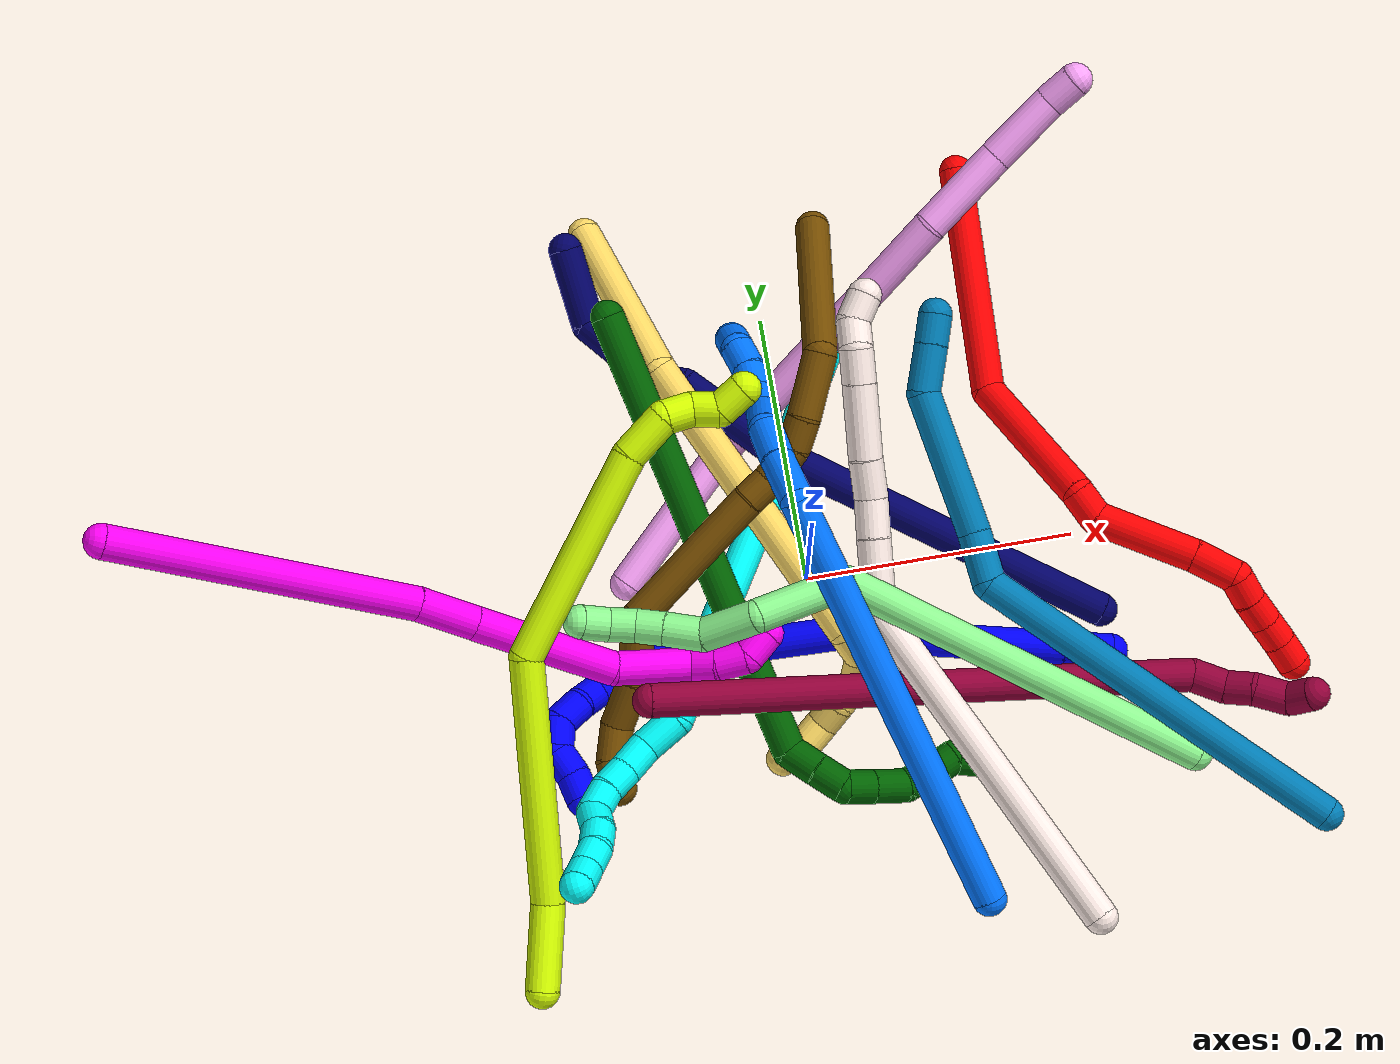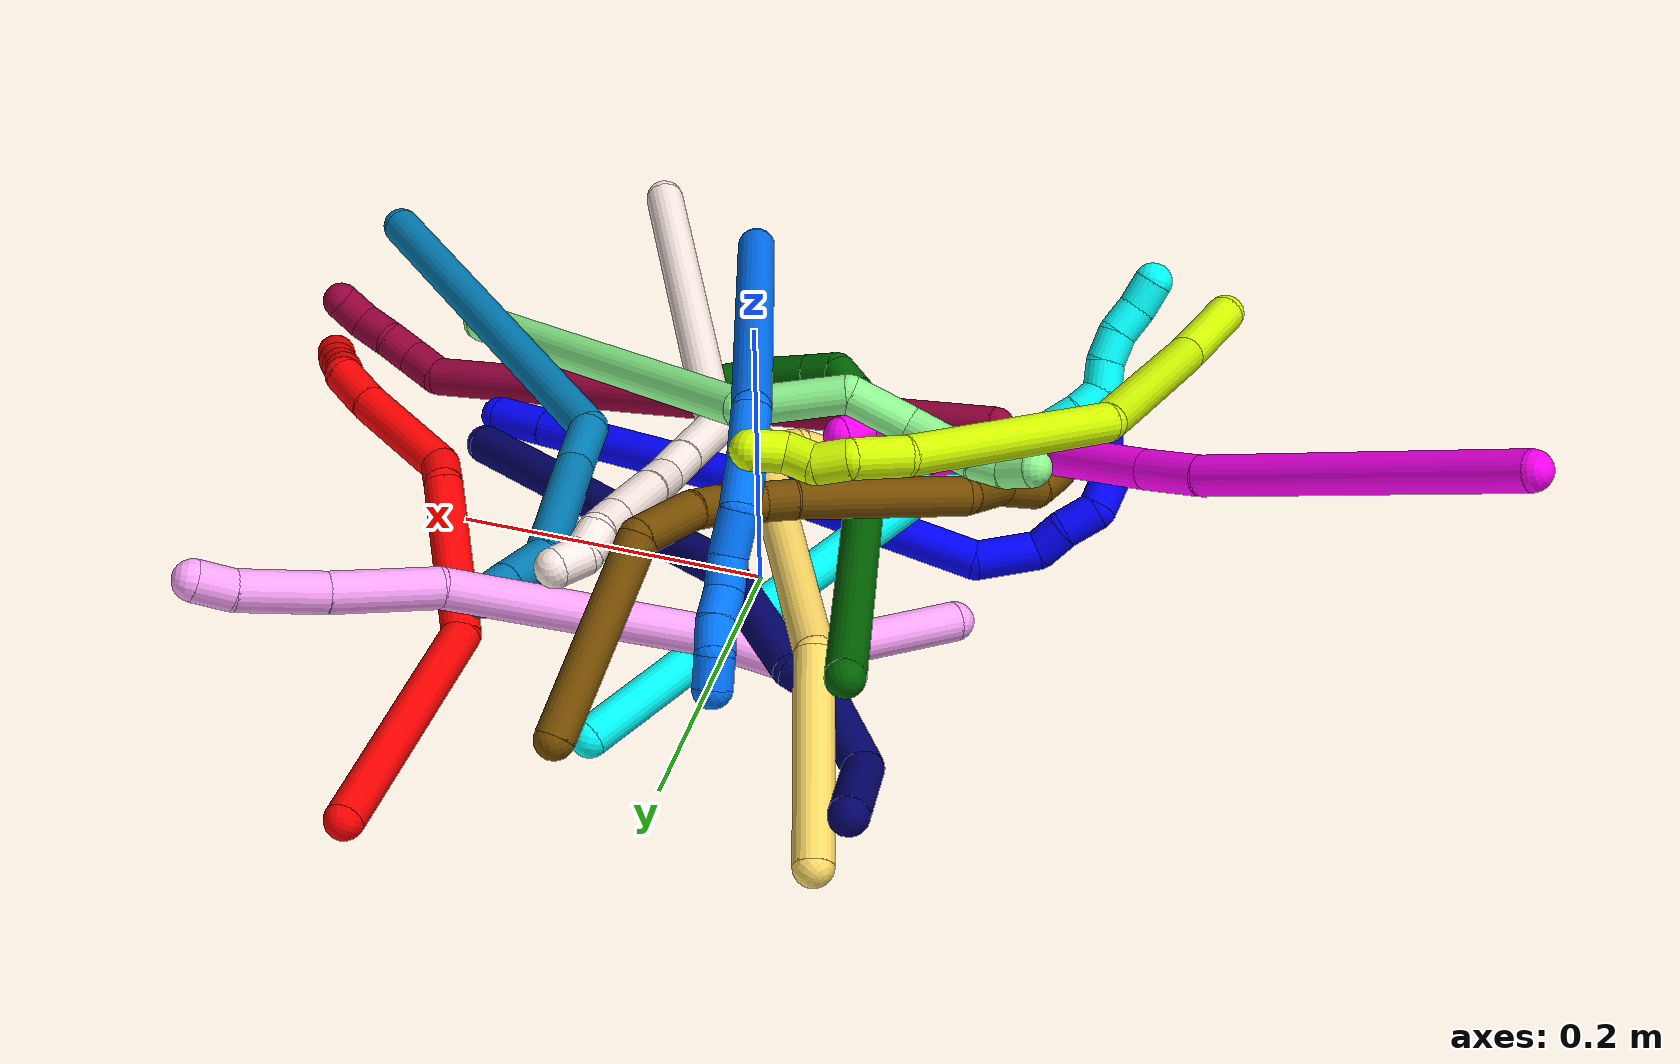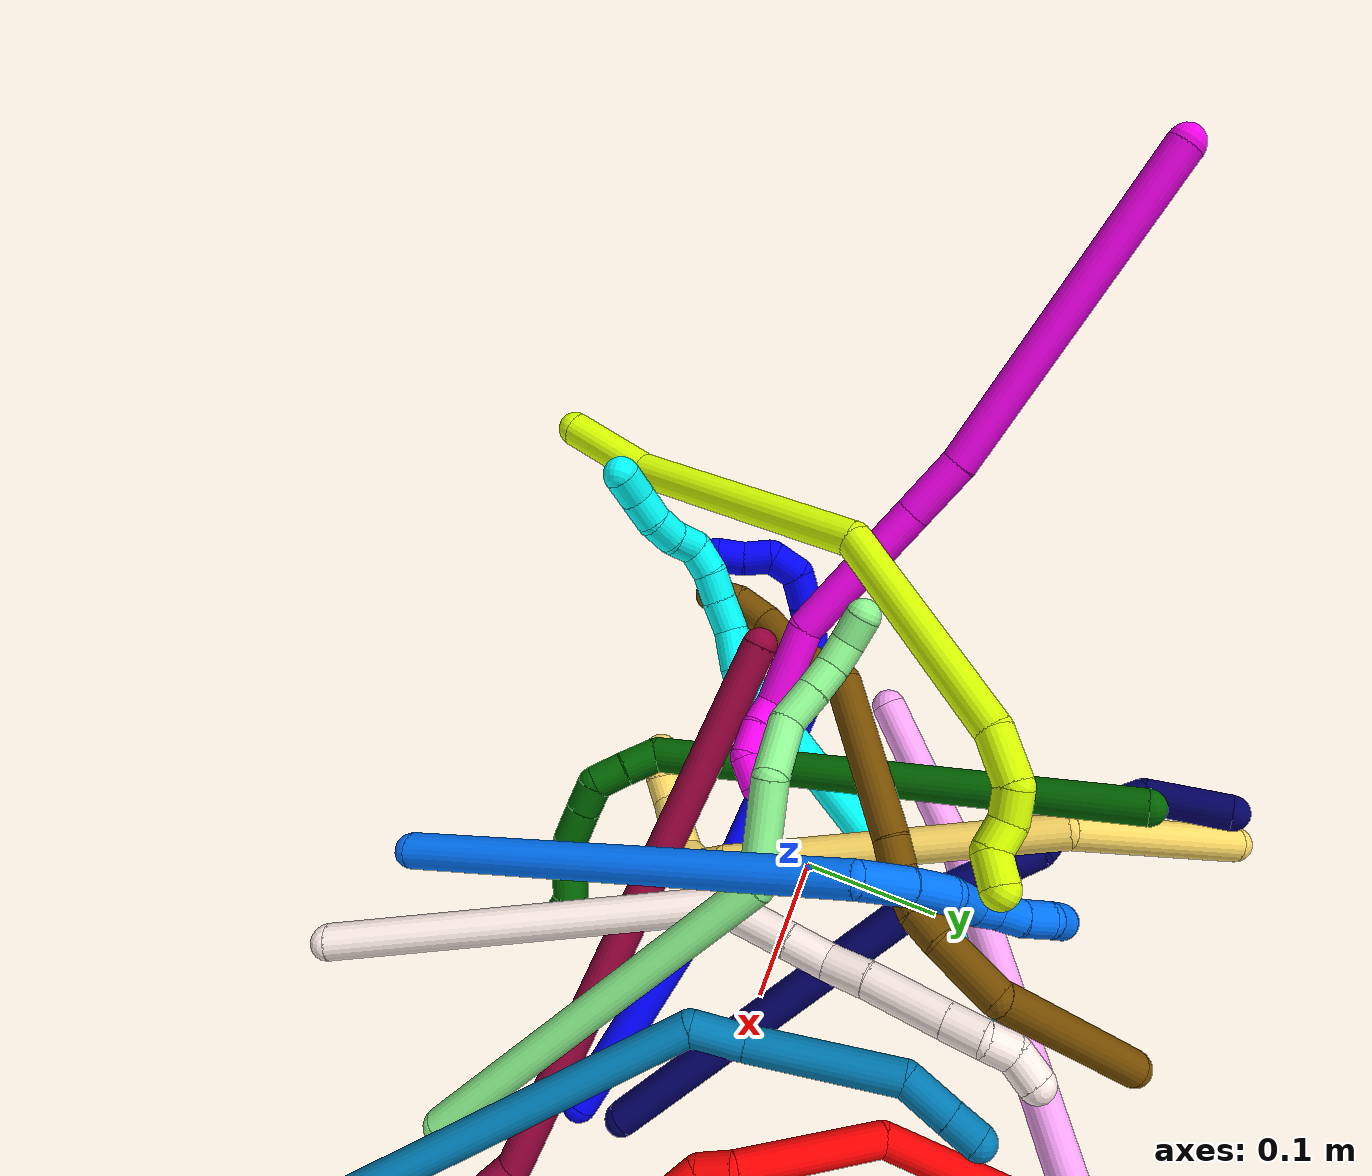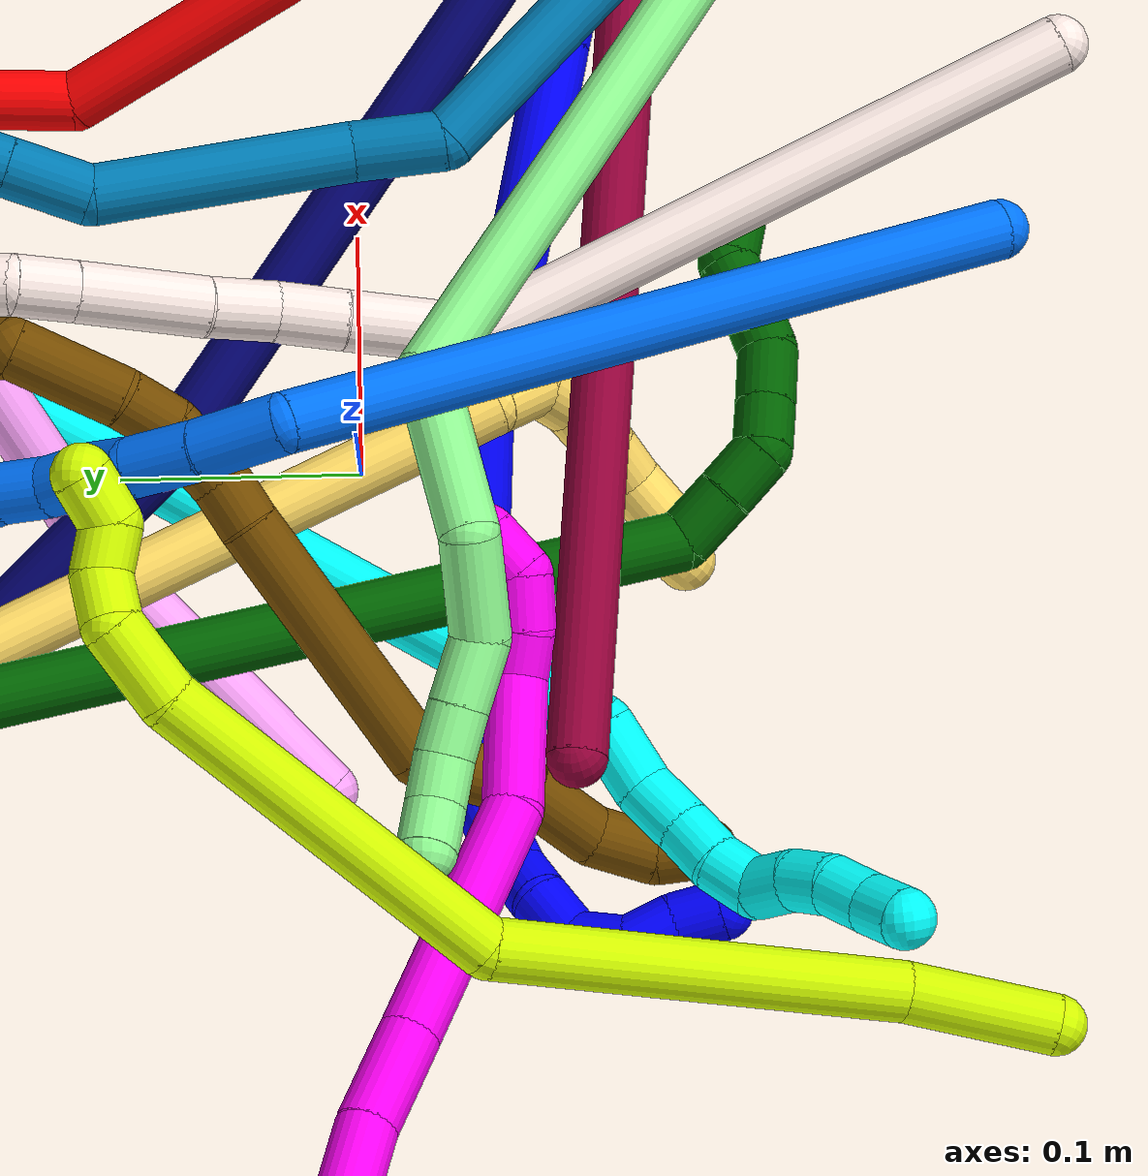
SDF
<sdf version="1.7">
 <world name="default">
  <plugin name="TubeGeneratorPlugin" filename="libtube_generator_plugin.so"/>
  <model name="photoneo_s_sensor">
   <static>1</static>
   <pose>0 0 2 1.57079 1.57079 3.14159</pose>
   <link name="link">
    <inertial><mass>0.1</mass></inertial>
    <sensor name="sensor" type="depth">
     <update_rate>30</update_rate>
     <camera>
      <horizontal_fov>1.22</horizontal_fov>
      <image><width>1920</width><height>1200</height><format>B8G8R8</format></image>
      <clip><near>0.1</near><far>4</far></clip>
      <depth_camera><output>points</output></depth_camera>
     </camera>
     <plugin name="camera_plugin" filename="libgazebo_ros_depth_camera.so">
      <baseline>0.2</baseline>
      <alwaysOn>1</alwaysOn>
      <updateRate>0.0</updateRate>
      <cameraName>camera_ir</cameraName>
      <imageTopicName>/camera/color/image_raw</imageTopicName>
      <cameraInfoTopicName>/camera/color/camera_info</cameraInfoTopicName>
      <depthImageTopicName>/camera/depth/image_raw</depthImageTopicName>
      <depthImageCameraInfoTopicName>/camera/depth/camera_info</depthImageCameraInfoTopicName>
      <pointCloudTopicName>/camera/depth/points</pointCloudTopicName>
      <frameName>fr_optical</frameName>
      <pointCloudCutoff>0.1</pointCloudCutoff>
      <pointCloudCutoffMax>2.0</pointCloudCutoffMax>
      <distortionK1>0</distortionK1>
      <distortionK2>0</distortionK2>
      <distortionK3>0</distortionK3>
      <distortionT1>0</distortionT1>
      <distortionT2>0</distortionT2>
      <CxPrime>0</CxPrime>
      <Cx>0</Cx>
      <Cy>0</Cy>
      <focalLength>0</focalLength>
      <hackBaseline>0</hackBaseline>
     </plugin>
    </sensor>
   </link>
  </model>
  <gravity>0 0 -9.8</gravity>
  <magnetic_field>6e-06 2.3e-05 -4.2e-05</magnetic_field>
  <atmosphere type="adiabatic"/>
  <physics name="default_physics" default="0" type="ode">
   <max_step_size>0.003</max_step_size>
   <real_time_factor>1</real_time_factor>
   <real_time_update_rate>1000</real_time_update_rate>
   <max_contacts>10000</max_contacts>
   <ode>
    <solver>
     <type>quick</type>
     <iters>100</iters>
     <sor>1.3</sor>
     <use_dynamic_moi_rescaling>0</use_dynamic_moi_rescaling>
    </solver>
    <constraints>
     <contact_max_correcting_vel>0</contact_max_correcting_vel>
     <contact_surface_layer>0.001</contact_surface_layer>
     <cfm>0</cfm>
     <erp>0.2</erp>
    </constraints>
   </ode>
  </physics>
  <scene><ambient>0.4 0.4 0.4 1</ambient><background>0.7 0.7 0.7 1</background><shadows>0</shadows></scene>
  <audio><device>default</device></audio>
  <spherical_coordinates>
   <surface_model>EARTH_WGS84</surface_model>
   <latitude_deg>0</latitude_deg>
   <longitude_deg>0</longitude_deg>
   <elevation>0</elevation>
   <heading_deg>0</heading_deg>
  </spherical_coordinates>
  <model name="bin">
   <static>1</static>
   <link name="bottom">
    <collision name="collision-bottom">
     <pose>0 0 -0.01 0 -0 0</pose>
     <geometry><box><size>0.8 0.6 0.02</size></box></geometry>
     <surface>
      <friction><ode><mu>100</mu><mu2>100</mu2></ode></friction>
      <contact><collide_bitmask>65535</collide_bitmask></contact>
     </surface>
    </collision>
   </link>
   <link name="west_wall">
    <collision name="collision-west_wall">
     <pose>-0.41 0 0.1 0 -0 0</pose>
     <geometry><box><size>0.02 0.6 0.2</size></box></geometry>
     <surface>
      <friction><ode><mu>100</mu><mu2>100</mu2></ode></friction>
      <contact><collide_bitmask>65535</collide_bitmask></contact>
     </surface>
    </collision>
   </link>
   <link name="east_wall">
    <collision name="collision-east_wall">
     <pose>0.41 0 0.1 0 -0 0</pose>
     <geometry><box><size>0.02 0.6 0.2</size></box></geometry>
     <surface>
      <friction><ode><mu>100</mu><mu2>100</mu2></ode></friction>
      <contact><collide_bitmask>65535</collide_bitmask></contact>
     </surface>
    </collision>
   </link>
   <link name="south_wall">
    <collision name="collision-south_wall">
     <pose>0 -0.31 0.1 0 -0 0</pose>
     <geometry><box><size>0.8 0.02 0.2</size></box></geometry>
     <surface>
      <friction><ode><mu>100</mu><mu2>100</mu2></ode></friction>
      <contact><collide_bitmask>65535</collide_bitmask></contact>
     </surface>
    </collision>
   </link>
   <link name="north_wall">
    <collision name="collision-north_wall">
     <pose>0 0.31 0.1 0 -0 0</pose>
     <geometry><box><size>0.8 0.02 0.2</size></box></geometry>
     <surface>
      <friction><ode><mu>100</mu><mu2>100</mu2></ode></friction>
      <contact><collide_bitmask>65535</collide_bitmask></contact>
     </surface>
    </collision>
   </link>
  </model>
  <model name="1">
   <static>0</static>
   <link name="1">
    <collision name="collision-cylinder-e_1_1_4">
     <pose>-0.013144 0.011251 0.005293 -1.13108 -0.813152 0.533527</pose>
     <geometry><cylinder><radius>0.0125</radius><length>0.036186</length></cylinder></geometry>
     <surface>
      <friction><ode><mu>1.16</mu><mu2>1.16</mu2><slip1>0</slip1><slip2>0</slip2></ode></friction>
      <contact><ode><kp>1e+06</kp><kd>1</kd><max_vel>0</max_vel><min_depth>0.001</min_depth></ode></contact>
     </surface>
    </collision>
    <visual name="visual-cylinder-e_1_1_4">
     <pose>-0.013144 0.011251 0.005293 -1.13108 -0.813152 0.533527</pose>
     <geometry><cylinder><radius>0.0125</radius><length>0.036186</length></cylinder></geometry>
     <material><ambient>0 0 1 1</ambient></material>
    </visual>
    <collision name="collision-cylinder-e_2_4_5">
     <pose>-0.087219 0.074933 0.035404 -1.1287 -0.809971 0.529972</pose>
     <geometry><cylinder><radius>0.0125</radius><length>0.168258</length></cylinder></geometry>
     <surface>
      <friction><ode><mu>1.16</mu><mu2>1.16</mu2><slip1>0</slip1><slip2>0</slip2></ode></friction>
      <contact><ode><kp>1e+06</kp><kd>1</kd><max_vel>0</max_vel><min_depth>0.001</min_depth></ode></contact>
     </surface>
    </collision>
    <visual name="visual-cylinder-e_2_4_5">
     <pose>-0.087219 0.074933 0.035404 -1.1287 -0.809971 0.529972</pose>
     <geometry><cylinder><radius>0.0125</radius><length>0.168258</length></cylinder></geometry>
     <material><ambient>0 0 1 1</ambient></material>
    </visual>
    <collision name="collision-cylinder-e_3_5_6">
     <pose>-0.20806 0.153716 0.091462 -0.700718 -0.972113 0.38145</pose>
     <geometry><cylinder><radius>0.0125</radius><length>0.145044</length></cylinder></geometry>
     <surface>
      <friction><ode><mu>1.16</mu><mu2>1.16</mu2><slip1>0</slip1><slip2>0</slip2></ode></friction>
      <contact><ode><kp>1e+06</kp><kd>1</kd><max_vel>0</max_vel><min_depth>0.001</min_depth></ode></contact>
     </surface>
    </collision>
    <visual name="visual-cylinder-e_3_5_6">
     <pose>-0.20806 0.153716 0.091462 -0.700718 -0.972113 0.38145</pose>
     <geometry><cylinder><radius>0.0125</radius><length>0.145044</length></cylinder></geometry>
     <material><ambient>0 0 1 1</ambient></material>
    </visual>
    <collision name="collision-cylinder-e_4_6_7">
     <pose>-0.276936 0.187653 0.139155 -0.431986 -0.459621 0.102572</pose>
     <geometry><cylinder><radius>0.0125</radius><length>0.040429</length></cylinder></geometry>
     <surface>
      <friction><ode><mu>1.16</mu><mu2>1.16</mu2><slip1>0</slip1><slip2>0</slip2></ode></friction>
      <contact><ode><kp>1e+06</kp><kd>1</kd><max_vel>0</max_vel><min_depth>0.001</min_depth></ode></contact>
     </surface>
    </collision>
    <visual name="visual-cylinder-e_4_6_7">
     <pose>-0.276936 0.187653 0.139155 -0.431986 -0.459621 0.102572</pose>
     <geometry><cylinder><radius>0.0125</radius><length>0.040429</length></cylinder></geometry>
     <material><ambient>0 0 1 1</ambient></material>
    </visual>
    <collision name="collision-cylinder-e_5_7_8">
     <pose>-0.285285 0.20265 0.163021 -0.785259 0.05891 -0.024402</pose>
     <geometry><cylinder><radius>0.0125</radius><length>0.021004</length></cylinder></geometry>
     <surface>
      <friction><ode><mu>1.16</mu><mu2>1.16</mu2><slip1>0</slip1><slip2>0</slip2></ode></friction>
      <contact><ode><kp>1e+06</kp><kd>1</kd><max_vel>0</max_vel><min_depth>0.001</min_depth></ode></contact>
     </surface>
    </collision>
    <visual name="visual-cylinder-e_5_7_8">
     <pose>-0.285285 0.20265 0.163021 -0.785259 0.05891 -0.024402</pose>
     <geometry><cylinder><radius>0.0125</radius><length>0.021004</length></cylinder></geometry>
     <material><ambient>0 0 1 1</ambient></material>
    </visual>
    <collision name="collision-cylinder-e_6_8_9">
     <pose>-0.285998 0.216244 0.180798 -0.537909 -0.109874 0.030313</pose>
     <geometry><cylinder><radius>0.0125</radius><length>0.024278</length></cylinder></geometry>
     <surface>
      <friction><ode><mu>1.16</mu><mu2>1.16</mu2><slip1>0</slip1><slip2>0</slip2></ode></friction>
      <contact><ode><kp>1e+06</kp><kd>1</kd><max_vel>0</max_vel><min_depth>0.001</min_depth></ode></contact>
     </surface>
    </collision>
    <visual name="visual-cylinder-e_6_8_9">
     <pose>-0.285998 0.216244 0.180798 -0.537909 -0.109874 0.030313</pose>
     <geometry><cylinder><radius>0.0125</radius><length>0.024278</length></cylinder></geometry>
     <material><ambient>0 0 1 1</ambient></material>
    </visual>
    <collision name="collision-cylinder-e_7_9_10">
     <pose>-0.281767 0.223752 0.201804 -0.123959 0.478326 -0.030261</pose>
     <geometry><cylinder><radius>0.0125</radius><length>0.024166</length></cylinder></geometry>
     <surface>
      <friction><ode><mu>1.16</mu><mu2>1.16</mu2><slip1>0</slip1><slip2>0</slip2></ode></friction>
      <contact><ode><kp>1e+06</kp><kd>1</kd><max_vel>0</max_vel><min_depth>0.001</min_depth></ode></contact>
     </surface>
    </collision>
    <visual name="visual-cylinder-e_7_9_10">
     <pose>-0.281767 0.223752 0.201804 -0.123959 0.478326 -0.030261</pose>
     <geometry><cylinder><radius>0.0125</radius><length>0.024166</length></cylinder></geometry>
     <material><ambient>0 0 1 1</ambient></material>
    </visual>
    <collision name="collision-cylinder-e_8_10_11">
     <pose>-0.269431 0.220082 0.218381 0.70009 0.717921 0.272273</pose>
     <geometry><cylinder><radius>0.0125</radius><length>0.020595</length></cylinder></geometry>
     <surface>
      <friction><ode><mu>1.16</mu><mu2>1.16</mu2><slip1>0</slip1><slip2>0</slip2></ode></friction>
      <contact><ode><kp>1e+06</kp><kd>1</kd><max_vel>0</max_vel><min_depth>0.001</min_depth></ode></contact>
     </surface>
    </collision>
    <visual name="visual-cylinder-e_8_10_11">
     <pose>-0.269431 0.220082 0.218381 0.70009 0.717921 0.272273</pose>
     <geometry><cylinder><radius>0.0125</radius><length>0.020595</length></cylinder></geometry>
     <material><ambient>0 0 1 1</ambient></material>
    </visual>
    <collision name="collision-cylinder-e_9_11_2">
     <pose>-0.256459 0.212187 0.231632 0.37698 0.666997 0.131978</pose>
     <geometry><cylinder><radius>0.0125</radius><length>0.02004</length></cylinder></geometry>
     <surface>
      <friction><ode><mu>1.16</mu><mu2>1.16</mu2><slip1>0</slip1><slip2>0</slip2></ode></friction>
      <contact><ode><kp>1e+06</kp><kd>1</kd><max_vel>0</max_vel><min_depth>0.001</min_depth></ode></contact>
     </surface>
    </collision>
    <visual name="visual-cylinder-e_9_11_2">
     <pose>-0.256459 0.212187 0.231632 0.37698 0.666997 0.131978</pose>
     <geometry><cylinder><radius>0.0125</radius><length>0.02004</length></cylinder></geometry>
     <material><ambient>0 0 1 1</ambient></material>
    </visual>
    <collision name="collision-sphere-2">
     <pose>-0.25026 0.209289 0.238951 0 -0 0</pose>
     <geometry><sphere><radius>0.0125</radius></sphere></geometry>
     <surface>
      <friction><ode><mu>1.16</mu><mu2>1.16</mu2><slip1>0</slip1><slip2>0</slip2></ode></friction>
      <contact><ode><kp>1e+06</kp><kd>1</kd><max_vel>0</max_vel><min_depth>0.001</min_depth></ode></contact>
     </surface>
    </collision>
    <visual name="visual-sphere-2">
     <pose>-0.25026 0.209289 0.238951 0 -0 0</pose>
     <geometry><sphere><radius>0.0125</radius></sphere></geometry>
     <material><ambient>0 0 1 1</ambient></material>
    </visual>
    <collision name="collision-sphere-11">
     <pose>-0.262657 0.215085 0.224312 0 -0 0</pose>
     <geometry><sphere><radius>0.0125</radius></sphere></geometry>
     <surface>
      <friction><ode><mu>1.16</mu><mu2>1.16</mu2><slip1>0</slip1><slip2>0</slip2></ode></friction>
      <contact><ode><kp>1e+06</kp><kd>1</kd><max_vel>0</max_vel><min_depth>0.001</min_depth></ode></contact>
     </surface>
    </collision>
    <visual name="visual-sphere-11">
     <pose>-0.262657 0.215085 0.224312 0 -0 0</pose>
     <geometry><sphere><radius>0.0125</radius></sphere></geometry>
     <material><ambient>0 0 1 1</ambient></material>
    </visual>
    <collision name="collision-sphere-10">
     <pose>-0.276205 0.225079 0.212449 0 -0 0</pose>
     <geometry><sphere><radius>0.0125</radius></sphere></geometry>
     <surface>
      <friction><ode><mu>1.16</mu><mu2>1.16</mu2><slip1>0</slip1><slip2>0</slip2></ode></friction>
      <contact><ode><kp>1e+06</kp><kd>1</kd><max_vel>0</max_vel><min_depth>0.001</min_depth></ode></contact>
     </surface>
    </collision>
    <visual name="visual-sphere-10">
     <pose>-0.276205 0.225079 0.212449 0 -0 0</pose>
     <geometry><sphere><radius>0.0125</radius></sphere></geometry>
     <material><ambient>0 0 1 1</ambient></material>
    </visual>
    <collision name="collision-sphere-9">
     <pose>-0.287329 0.222426 0.19116 0 -0 0</pose>
     <geometry><sphere><radius>0.0125</radius></sphere></geometry>
     <surface>
      <friction><ode><mu>1.16</mu><mu2>1.16</mu2><slip1>0</slip1><slip2>0</slip2></ode></friction>
      <contact><ode><kp>1e+06</kp><kd>1</kd><max_vel>0</max_vel><min_depth>0.001</min_depth></ode></contact>
     </surface>
    </collision>
    <visual name="visual-sphere-9">
     <pose>-0.287329 0.222426 0.19116 0 -0 0</pose>
     <geometry><sphere><radius>0.0125</radius></sphere></geometry>
     <material><ambient>0 0 1 1</ambient></material>
    </visual>
    <collision name="collision-sphere-4">
     <pose>-0.026287 0.022502 0.010586 0 -0 0</pose>
     <geometry><sphere><radius>0.0125</radius></sphere></geometry>
     <surface>
      <friction><ode><mu>1.16</mu><mu2>1.16</mu2><slip1>0</slip1><slip2>0</slip2></ode></friction>
      <contact><ode><kp>1e+06</kp><kd>1</kd><max_vel>0</max_vel><min_depth>0.001</min_depth></ode></contact>
     </surface>
    </collision>
    <visual name="visual-sphere-4">
     <pose>-0.026287 0.022502 0.010586 0 -0 0</pose>
     <geometry><sphere><radius>0.0125</radius></sphere></geometry>
     <material><ambient>0 0 1 1</ambient></material>
    </visual>
    <collision name="collision-sphere-1">
     <geometry><sphere><radius>0.0125</radius></sphere></geometry>
     <surface>
      <friction><ode><mu>1.16</mu><mu2>1.16</mu2><slip1>0</slip1><slip2>0</slip2></ode></friction>
      <contact><ode><kp>1e+06</kp><kd>1</kd><max_vel>0</max_vel><min_depth>0.001</min_depth></ode></contact>
     </surface>
    </collision>
    <visual name="visual-sphere-1">
     <geometry><sphere><radius>0.0125</radius></sphere></geometry>
     <material><ambient>0 0 1 1</ambient></material>
    </visual>
    <collision name="collision-sphere-8">
     <pose>-0.284667 0.210062 0.170436 0 -0 0</pose>
     <geometry><sphere><radius>0.0125</radius></sphere></geometry>
     <surface>
      <friction><ode><mu>1.16</mu><mu2>1.16</mu2><slip1>0</slip1><slip2>0</slip2></ode></friction>
      <contact><ode><kp>1e+06</kp><kd>1</kd><max_vel>0</max_vel><min_depth>0.001</min_depth></ode></contact>
     </surface>
    </collision>
    <visual name="visual-sphere-8">
     <pose>-0.284667 0.210062 0.170436 0 -0 0</pose>
     <geometry><sphere><radius>0.0125</radius></sphere></geometry>
     <material><ambient>0 0 1 1</ambient></material>
    </visual>
    <collision name="collision-sphere-5">
     <pose>-0.148151 0.127364 0.060222 0 -0 0</pose>
     <geometry><sphere><radius>0.0125</radius></sphere></geometry>
     <surface>
      <friction><ode><mu>1.16</mu><mu2>1.16</mu2><slip1>0</slip1><slip2>0</slip2></ode></friction>
      <contact><ode><kp>1e+06</kp><kd>1</kd><max_vel>0</max_vel><min_depth>0.001</min_depth></ode></contact>
     </surface>
    </collision>
    <visual name="visual-sphere-5">
     <pose>-0.148151 0.127364 0.060222 0 -0 0</pose>
     <geometry><sphere><radius>0.0125</radius></sphere></geometry>
     <material><ambient>0 0 1 1</ambient></material>
    </visual>
    <collision name="collision-sphere-6">
     <pose>-0.267969 0.180068 0.122702 0 -0 0</pose>
     <geometry><sphere><radius>0.0125</radius></sphere></geometry>
     <surface>
      <friction><ode><mu>1.16</mu><mu2>1.16</mu2><slip1>0</slip1><slip2>0</slip2></ode></friction>
      <contact><ode><kp>1e+06</kp><kd>1</kd><max_vel>0</max_vel><min_depth>0.001</min_depth></ode></contact>
     </surface>
    </collision>
    <visual name="visual-sphere-6">
     <pose>-0.267969 0.180068 0.122702 0 -0 0</pose>
     <geometry><sphere><radius>0.0125</radius></sphere></geometry>
     <material><ambient>0 0 1 1</ambient></material>
    </visual>
    <collision name="collision-sphere-7">
     <pose>-0.285903 0.195238 0.155607 0 -0 0</pose>
     <geometry><sphere><radius>0.0125</radius></sphere></geometry>
     <surface>
      <friction><ode><mu>1.16</mu><mu2>1.16</mu2><slip1>0</slip1><slip2>0</slip2></ode></friction>
      <contact><ode><kp>1e+06</kp><kd>1</kd><max_vel>0</max_vel><min_depth>0.001</min_depth></ode></contact>
     </surface>
    </collision>
    <visual name="visual-sphere-7">
     <pose>-0.285903 0.195238 0.155607 0 -0 0</pose>
     <geometry><sphere><radius>0.0125</radius></sphere></geometry>
     <material><ambient>0 0 1 1</ambient></material>
    </visual>
    <inertial>
     <pose>-0.173917 0.133192 0.09374 0 -0 0</pose>
     <mass>0.5</mass>
     <inertia>
      <ixx>0.000572</ixx>
      <ixy>0</ixy>
      <ixz>0</ixz>
      <iyy>0.000751</iyy>
      <iyz>0</iyz>
      <izz>0.000177</izz>
     </inertia>
    </inertial>
   </link>
   <pose>0.21127 -0.093215 0.011952 1.5324 -0.604914 -0.48804</pose>
  </model>
  <model name="2">
   <static>0</static>
   <link name="2">
    <collision name="collision-cylinder-e_1_1_4">
     <pose>0.039979 -0.060343 0.046857 0.910542 0.482103 0.239553</pose>
     <geometry><cylinder><radius>0.0125</radius><length>0.172456</length></cylinder></geometry>
     <surface>
      <friction><ode><mu>1.16</mu><mu2>1.16</mu2><slip1>0</slip1><slip2>0</slip2></ode></friction>
      <contact><ode><kp>1e+06</kp><kd>1</kd><max_vel>0</max_vel><min_depth>0.001</min_depth></ode></contact>
     </surface>
    </collision>
    <visual name="visual-cylinder-e_1_1_4">
     <pose>0.039979 -0.060343 0.046857 0.910542 0.482103 0.239553</pose>
     <geometry><cylinder><radius>0.0125</radius><length>0.172456</length></cylinder></geometry>
     <material><ambient>1 0 0 1</ambient></material>
    </visual>
    <collision name="collision-cylinder-e_2_4_5">
     <pose>0.10589 -0.169115 0.093099 1.58351 0.491579 0.497615</pose>
     <geometry><cylinder><radius>0.0125</radius><length>0.109874</length></cylinder></geometry>
     <surface>
      <friction><ode><mu>1.16</mu><mu2>1.16</mu2><slip1>0</slip1><slip2>0</slip2></ode></friction>
      <contact><ode><kp>1e+06</kp><kd>1</kd><max_vel>0</max_vel><min_depth>0.001</min_depth></ode></contact>
     </surface>
    </collision>
    <visual name="visual-cylinder-e_2_4_5">
     <pose>0.10589 -0.169115 0.093099 1.58351 0.491579 0.497615</pose>
     <geometry><cylinder><radius>0.0125</radius><length>0.109874</length></cylinder></geometry>
     <material><ambient>1 0 0 1</ambient></material>
    </visual>
    <collision name="collision-cylinder-e_3_5_6">
     <pose>0.133125 -0.229191 0.095777 1.29524 0.107357 0.081245</pose>
     <geometry><cylinder><radius>0.0125</radius><length>0.024349</length></cylinder></geometry>
     <surface>
      <friction><ode><mu>1.16</mu><mu2>1.16</mu2><slip1>0</slip1><slip2>0</slip2></ode></friction>
      <contact><ode><kp>1e+06</kp><kd>1</kd><max_vel>0</max_vel><min_depth>0.001</min_depth></ode></contact>
     </surface>
    </collision>
    <visual name="visual-cylinder-e_3_5_6">
     <pose>0.133125 -0.229191 0.095777 1.29524 0.107357 0.081245</pose>
     <geometry><cylinder><radius>0.0125</radius><length>0.024349</length></cylinder></geometry>
     <material><ambient>1 0 0 1</ambient></material>
    </visual>
    <collision name="collision-cylinder-e_4_6_7">
     <pose>0.131977 -0.277741 0.088525 1.84913 -0.063822 -0.084593</pose>
     <geometry><cylinder><radius>0.0125</radius><length>0.076915</length></cylinder></geometry>
     <surface>
      <friction><ode><mu>1.16</mu><mu2>1.16</mu2><slip1>0</slip1><slip2>0</slip2></ode></friction>
      <contact><ode><kp>1e+06</kp><kd>1</kd><max_vel>0</max_vel><min_depth>0.001</min_depth></ode></contact>
     </surface>
    </collision>
    <visual name="visual-cylinder-e_4_6_7">
     <pose>0.131977 -0.277741 0.088525 1.84913 -0.063822 -0.084593</pose>
     <geometry><cylinder><radius>0.0125</radius><length>0.076915</length></cylinder></geometry>
     <material><ambient>1 0 0 1</ambient></material>
    </visual>
    <collision name="collision-cylinder-e_5_7_8">
     <pose>0.129608 -0.330992 0.074739 1.76649 0.005037 0.006133</pose>
     <geometry><cylinder><radius>0.0125</radius><length>0.033335</length></cylinder></geometry>
     <surface>
      <friction><ode><mu>1.16</mu><mu2>1.16</mu2><slip1>0</slip1><slip2>0</slip2></ode></friction>
      <contact><ode><kp>1e+06</kp><kd>1</kd><max_vel>0</max_vel><min_depth>0.001</min_depth></ode></contact>
     </surface>
    </collision>
    <visual name="visual-cylinder-e_5_7_8">
     <pose>0.129608 -0.330992 0.074739 1.76649 0.005037 0.006133</pose>
     <geometry><cylinder><radius>0.0125</radius><length>0.033335</length></cylinder></geometry>
     <material><ambient>1 0 0 1</ambient></material>
    </visual>
    <collision name="collision-cylinder-e_6_8_9">
     <pose>0.127805 -0.356384 0.076484 1.06687 -0.180799 -0.106959</pose>
     <geometry><cylinder><radius>0.0125</radius><length>0.020994</length></cylinder></geometry>
     <surface>
      <friction><ode><mu>1.16</mu><mu2>1.16</mu2><slip1>0</slip1><slip2>0</slip2></ode></friction>
      <contact><ode><kp>1e+06</kp><kd>1</kd><max_vel>0</max_vel><min_depth>0.001</min_depth></ode></contact>
     </surface>
    </collision>
    <visual name="visual-cylinder-e_6_8_9">
     <pose>0.127805 -0.356384 0.076484 1.06687 -0.180799 -0.106959</pose>
     <geometry><cylinder><radius>0.0125</radius><length>0.020994</length></cylinder></geometry>
     <material><ambient>1 0 0 1</ambient></material>
    </visual>
    <collision name="collision-cylinder-e_7_9_10">
     <pose>0.123275 -0.374948 0.085813 1.14289 -0.247329 -0.159511</pose>
     <geometry><cylinder><radius>0.0125</radius><length>0.021588</length></cylinder></geometry>
     <surface>
      <friction><ode><mu>1.16</mu><mu2>1.16</mu2><slip1>0</slip1><slip2>0</slip2></ode></friction>
      <contact><ode><kp>1e+06</kp><kd>1</kd><max_vel>0</max_vel><min_depth>0.001</min_depth></ode></contact>
     </surface>
    </collision>
    <visual name="visual-cylinder-e_7_9_10">
     <pose>0.123275 -0.374948 0.085813 1.14289 -0.247329 -0.159511</pose>
     <geometry><cylinder><radius>0.0125</radius><length>0.021588</length></cylinder></geometry>
     <material><ambient>1 0 0 1</ambient></material>
    </visual>
    <collision name="collision-cylinder-e_8_10_11">
     <pose>0.118577 -0.393612 0.094033 1.1697 -0.204062 -0.135379</pose>
     <geometry><cylinder><radius>0.0125</radius><length>0.020281</length></cylinder></geometry>
     <surface>
      <friction><ode><mu>1.16</mu><mu2>1.16</mu2><slip1>0</slip1><slip2>0</slip2></ode></friction>
      <contact><ode><kp>1e+06</kp><kd>1</kd><max_vel>0</max_vel><min_depth>0.001</min_depth></ode></contact>
     </surface>
    </collision>
    <visual name="visual-cylinder-e_8_10_11">
     <pose>0.118577 -0.393612 0.094033 1.1697 -0.204062 -0.135379</pose>
     <geometry><cylinder><radius>0.0125</radius><length>0.020281</length></cylinder></geometry>
     <material><ambient>1 0 0 1</ambient></material>
    </visual>
    <collision name="collision-cylinder-e_9_11_2">
     <pose>0.115275 -0.411909 0.101998 1.1508 -0.123726 -0.08031</pose>
     <geometry><cylinder><radius>0.0125</radius><length>0.020207</length></cylinder></geometry>
     <surface>
      <friction><ode><mu>1.16</mu><mu2>1.16</mu2><slip1>0</slip1><slip2>0</slip2></ode></friction>
      <contact><ode><kp>1e+06</kp><kd>1</kd><max_vel>0</max_vel><min_depth>0.001</min_depth></ode></contact>
     </surface>
    </collision>
    <visual name="visual-cylinder-e_9_11_2">
     <pose>0.115275 -0.411909 0.101998 1.1508 -0.123726 -0.08031</pose>
     <geometry><cylinder><radius>0.0125</radius><length>0.020207</length></cylinder></geometry>
     <material><ambient>1 0 0 1</ambient></material>
    </visual>
    <collision name="collision-sphere-2">
     <pose>0.114028 -0.421064 0.106086 0 -0 0</pose>
     <geometry><sphere><radius>0.0125</radius></sphere></geometry>
     <surface>
      <friction><ode><mu>1.16</mu><mu2>1.16</mu2><slip1>0</slip1><slip2>0</slip2></ode></friction>
      <contact><ode><kp>1e+06</kp><kd>1</kd><max_vel>0</max_vel><min_depth>0.001</min_depth></ode></contact>
     </surface>
    </collision>
    <visual name="visual-sphere-2">
     <pose>0.114028 -0.421064 0.106086 0 -0 0</pose>
     <geometry><sphere><radius>0.0125</radius></sphere></geometry>
     <material><ambient>1 0 0 1</ambient></material>
    </visual>
    <collision name="collision-sphere-11">
     <pose>0.116522 -0.402754 0.09791 0 -0 0</pose>
     <geometry><sphere><radius>0.0125</radius></sphere></geometry>
     <surface>
      <friction><ode><mu>1.16</mu><mu2>1.16</mu2><slip1>0</slip1><slip2>0</slip2></ode></friction>
      <contact><ode><kp>1e+06</kp><kd>1</kd><max_vel>0</max_vel><min_depth>0.001</min_depth></ode></contact>
     </surface>
    </collision>
    <visual name="visual-sphere-11">
     <pose>0.116522 -0.402754 0.09791 0 -0 0</pose>
     <geometry><sphere><radius>0.0125</radius></sphere></geometry>
     <material><ambient>1 0 0 1</ambient></material>
    </visual>
    <collision name="collision-sphere-10">
     <pose>0.120632 -0.38447 0.090156 0 -0 0</pose>
     <geometry><sphere><radius>0.0125</radius></sphere></geometry>
     <surface>
      <friction><ode><mu>1.16</mu><mu2>1.16</mu2><slip1>0</slip1><slip2>0</slip2></ode></friction>
      <contact><ode><kp>1e+06</kp><kd>1</kd><max_vel>0</max_vel><min_depth>0.001</min_depth></ode></contact>
     </surface>
    </collision>
    <visual name="visual-sphere-10">
     <pose>0.120632 -0.38447 0.090156 0 -0 0</pose>
     <geometry><sphere><radius>0.0125</radius></sphere></geometry>
     <material><ambient>1 0 0 1</ambient></material>
    </visual>
    <collision name="collision-sphere-9">
     <pose>0.125917 -0.365426 0.08147 0 -0 0</pose>
     <geometry><sphere><radius>0.0125</radius></sphere></geometry>
     <surface>
      <friction><ode><mu>1.16</mu><mu2>1.16</mu2><slip1>0</slip1><slip2>0</slip2></ode></friction>
      <contact><ode><kp>1e+06</kp><kd>1</kd><max_vel>0</max_vel><min_depth>0.001</min_depth></ode></contact>
     </surface>
    </collision>
    <visual name="visual-sphere-9">
     <pose>0.125917 -0.365426 0.08147 0 -0 0</pose>
     <geometry><sphere><radius>0.0125</radius></sphere></geometry>
     <material><ambient>1 0 0 1</ambient></material>
    </visual>
    <collision name="collision-sphere-4">
     <pose>0.079958 -0.120687 0.093715 0 -0 0</pose>
     <geometry><sphere><radius>0.0125</radius></sphere></geometry>
     <surface>
      <friction><ode><mu>1.16</mu><mu2>1.16</mu2><slip1>0</slip1><slip2>0</slip2></ode></friction>
      <contact><ode><kp>1e+06</kp><kd>1</kd><max_vel>0</max_vel><min_depth>0.001</min_depth></ode></contact>
     </surface>
    </collision>
    <visual name="visual-sphere-4">
     <pose>0.079958 -0.120687 0.093715 0 -0 0</pose>
     <geometry><sphere><radius>0.0125</radius></sphere></geometry>
     <material><ambient>1 0 0 1</ambient></material>
    </visual>
    <collision name="collision-sphere-1">
     <geometry><sphere><radius>0.0125</radius></sphere></geometry>
     <surface>
      <friction><ode><mu>1.16</mu><mu2>1.16</mu2><slip1>0</slip1><slip2>0</slip2></ode></friction>
      <contact><ode><kp>1e+06</kp><kd>1</kd><max_vel>0</max_vel><min_depth>0.001</min_depth></ode></contact>
     </surface>
    </collision>
    <visual name="visual-sphere-1">
     <geometry><sphere><radius>0.0125</radius></sphere></geometry>
     <material><ambient>1 0 0 1</ambient></material>
    </visual>
    <collision name="collision-sphere-8">
     <pose>0.129692 -0.347341 0.071498 0 -0 0</pose>
     <geometry><sphere><radius>0.0125</radius></sphere></geometry>
     <surface>
      <friction><ode><mu>1.16</mu><mu2>1.16</mu2><slip1>0</slip1><slip2>0</slip2></ode></friction>
      <contact><ode><kp>1e+06</kp><kd>1</kd><max_vel>0</max_vel><min_depth>0.001</min_depth></ode></contact>
     </surface>
    </collision>
    <visual name="visual-sphere-8">
     <pose>0.129692 -0.347341 0.071498 0 -0 0</pose>
     <geometry><sphere><radius>0.0125</radius></sphere></geometry>
     <material><ambient>1 0 0 1</ambient></material>
    </visual>
    <collision name="collision-sphere-5">
     <pose>0.131821 -0.217543 0.092483 0 -0 0</pose>
     <geometry><sphere><radius>0.0125</radius></sphere></geometry>
     <surface>
      <friction><ode><mu>1.16</mu><mu2>1.16</mu2><slip1>0</slip1><slip2>0</slip2></ode></friction>
      <contact><ode><kp>1e+06</kp><kd>1</kd><max_vel>0</max_vel><min_depth>0.001</min_depth></ode></contact>
     </surface>
    </collision>
    <visual name="visual-sphere-5">
     <pose>0.131821 -0.217543 0.092483 0 -0 0</pose>
     <geometry><sphere><radius>0.0125</radius></sphere></geometry>
     <material><ambient>1 0 0 1</ambient></material>
    </visual>
    <collision name="collision-sphere-6">
     <pose>0.13443 -0.240839 0.09907 0 -0 0</pose>
     <geometry><sphere><radius>0.0125</radius></sphere></geometry>
     <surface>
      <friction><ode><mu>1.16</mu><mu2>1.16</mu2><slip1>0</slip1><slip2>0</slip2></ode></friction>
      <contact><ode><kp>1e+06</kp><kd>1</kd><max_vel>0</max_vel><min_depth>0.001</min_depth></ode></contact>
     </surface>
    </collision>
    <visual name="visual-sphere-6">
     <pose>0.13443 -0.240839 0.09907 0 -0 0</pose>
     <geometry><sphere><radius>0.0125</radius></sphere></geometry>
     <material><ambient>1 0 0 1</ambient></material>
    </visual>
    <collision name="collision-sphere-7">
     <pose>0.129524 -0.314643 0.07798 0 -0 0</pose>
     <geometry><sphere><radius>0.0125</radius></sphere></geometry>
     <surface>
      <friction><ode><mu>1.16</mu><mu2>1.16</mu2><slip1>0</slip1><slip2>0</slip2></ode></friction>
      <contact><ode><kp>1e+06</kp><kd>1</kd><max_vel>0</max_vel><min_depth>0.001</min_depth></ode></contact>
     </surface>
    </collision>
    <visual name="visual-sphere-7">
     <pose>0.129524 -0.314643 0.07798 0 -0 0</pose>
     <geometry><sphere><radius>0.0125</radius></sphere></geometry>
     <material><ambient>1 0 0 1</ambient></material>
    </visual>
    <inertial>
     <pose>0.092642 -0.197695 0.074738 0 -0 0</pose>
     <mass>0.5</mass>
     <inertia>
      <ixx>0.00066</ixx>
      <ixy>0</ixy>
      <ixz>0</ixz>
      <iyy>0.000415</iyy>
      <iyz>0</iyz>
      <izz>0.000213</izz>
     </inertia>
    </inertial>
   </link>
   <pose>0.165041 0.287859 0.013602 3.03199 -0.914518 -2.30038</pose>
  </model>
  <model name="3">
   <static>0</static>
   <link name="3">
    <collision name="collision-cylinder-e_1_1_4">
     <pose>-0.019829 -0.036331 -0.027068 2.21111 -0.412548 -0.789871</pose>
     <geometry><cylinder><radius>0.0125</radius><length>0.098909</length></cylinder></geometry>
     <surface>
      <friction><ode><mu>1.16</mu><mu2>1.16</mu2><slip1>0</slip1><slip2>0</slip2></ode></friction>
      <contact><ode><kp>1e+06</kp><kd>1</kd><max_vel>0</max_vel><min_depth>0.001</min_depth></ode></contact>
     </surface>
    </collision>
    <visual name="visual-cylinder-e_1_1_4">
     <pose>-0.019829 -0.036331 -0.027068 2.21111 -0.412548 -0.789871</pose>
     <geometry><cylinder><radius>0.0125</radius><length>0.098909</length></cylinder></geometry>
     <material><ambient>0.003922 1 0.996078 1</ambient></material>
    </visual>
    <collision name="collision-cylinder-e_2_4_5">
     <pose>-0.084694 -0.153521 -0.117193 2.23313 -0.413845 -0.81208</pose>
     <geometry><cylinder><radius>0.0125</radius><length>0.223989</length></cylinder></geometry>
     <surface>
      <friction><ode><mu>1.16</mu><mu2>1.16</mu2><slip1>0</slip1><slip2>0</slip2></ode></friction>
      <contact><ode><kp>1e+06</kp><kd>1</kd><max_vel>0</max_vel><min_depth>0.001</min_depth></ode></contact>
     </surface>
    </collision>
    <visual name="visual-cylinder-e_2_4_5">
     <pose>-0.084694 -0.153521 -0.117193 2.23313 -0.413845 -0.81208</pose>
     <geometry><cylinder><radius>0.0125</radius><length>0.223989</length></cylinder></geometry>
     <material><ambient>0.003922 1 0.996078 1</ambient></material>
    </visual>
    <collision name="collision-cylinder-e_3_5_6">
     <pose>-0.133497 -0.240022 -0.193642 2.74278 -0.253647 -1.12572</pose>
     <geometry><cylinder><radius>0.0125</radius><length>0.030022</length></cylinder></geometry>
     <surface>
      <friction><ode><mu>1.16</mu><mu2>1.16</mu2><slip1>0</slip1><slip2>0</slip2></ode></friction>
      <contact><ode><kp>1e+06</kp><kd>1</kd><max_vel>0</max_vel><min_depth>0.001</min_depth></ode></contact>
     </surface>
    </collision>
    <visual name="visual-cylinder-e_3_5_6">
     <pose>-0.133497 -0.240022 -0.193642 2.74278 -0.253647 -1.12572</pose>
     <geometry><cylinder><radius>0.0125</radius><length>0.030022</length></cylinder></geometry>
     <material><ambient>0.003922 1 0.996078 1</ambient></material>
    </visual>
    <collision name="collision-cylinder-e_4_6_7">
     <pose>-0.144398 -0.251221 -0.215429 2.557 -0.616419 -1.62711</pose>
     <geometry><cylinder><radius>0.0125</radius><length>0.02468</length></cylinder></geometry>
     <surface>
      <friction><ode><mu>1.16</mu><mu2>1.16</mu2><slip1>0</slip1><slip2>0</slip2></ode></friction>
      <contact><ode><kp>1e+06</kp><kd>1</kd><max_vel>0</max_vel><min_depth>0.001</min_depth></ode></contact>
     </surface>
    </collision>
    <visual name="visual-cylinder-e_4_6_7">
     <pose>-0.144398 -0.251221 -0.215429 2.557 -0.616419 -1.62711</pose>
     <geometry><cylinder><radius>0.0125</radius><length>0.02468</length></cylinder></geometry>
     <material><ambient>0.003922 1 0.996078 1</ambient></material>
    </visual>
    <collision name="collision-cylinder-e_5_7_8">
     <pose>-0.158106 -0.260768 -0.230882 2.62695 -0.681441 -1.86457</pose>
     <geometry><cylinder><radius>0.0125</radius><length>0.020874</length></cylinder></geometry>
     <surface>
      <friction><ode><mu>1.16</mu><mu2>1.16</mu2><slip1>0</slip1><slip2>0</slip2></ode></friction>
      <contact><ode><kp>1e+06</kp><kd>1</kd><max_vel>0</max_vel><min_depth>0.001</min_depth></ode></contact>
     </surface>
    </collision>
    <visual name="visual-cylinder-e_5_7_8">
     <pose>-0.158106 -0.260768 -0.230882 2.62695 -0.681441 -1.86457</pose>
     <geometry><cylinder><radius>0.0125</radius><length>0.020874</length></cylinder></geometry>
     <material><ambient>0.003922 1 0.996078 1</ambient></material>
    </visual>
    <collision name="collision-cylinder-e_6_8_9">
     <pose>-0.170716 -0.270695 -0.243651 2.33689 -0.632182 -1.31049</pose>
     <geometry><cylinder><radius>0.0125</radius><length>0.020425</length></cylinder></geometry>
     <surface>
      <friction><ode><mu>1.16</mu><mu2>1.16</mu2><slip1>0</slip1><slip2>0</slip2></ode></friction>
      <contact><ode><kp>1e+06</kp><kd>1</kd><max_vel>0</max_vel><min_depth>0.001</min_depth></ode></contact>
     </surface>
    </collision>
    <visual name="visual-cylinder-e_6_8_9">
     <pose>-0.170716 -0.270695 -0.243651 2.33689 -0.632182 -1.31049</pose>
     <geometry><cylinder><radius>0.0125</radius><length>0.020425</length></cylinder></geometry>
     <material><ambient>0.003922 1 0.996078 1</ambient></material>
    </visual>
    <collision name="collision-cylinder-e_7_9_10">
     <pose>-0.184909 -0.282444 -0.2478 1.30816 -0.93525 -0.738763</pose>
     <geometry><cylinder><radius>0.0125</radius><length>0.020277</length></cylinder></geometry>
     <surface>
      <friction><ode><mu>1.16</mu><mu2>1.16</mu2><slip1>0</slip1><slip2>0</slip2></ode></friction>
      <contact><ode><kp>1e+06</kp><kd>1</kd><max_vel>0</max_vel><min_depth>0.001</min_depth></ode></contact>
     </surface>
    </collision>
    <visual name="visual-cylinder-e_7_9_10">
     <pose>-0.184909 -0.282444 -0.2478 1.30816 -0.93525 -0.738763</pose>
     <geometry><cylinder><radius>0.0125</radius><length>0.020277</length></cylinder></geometry>
     <material><ambient>0.003922 1 0.996078 1</ambient></material>
    </visual>
    <collision name="collision-cylinder-e_8_10_11">
     <pose>-0.201533 -0.293576 -0.24735 1.77678 -1.00003 -1.18376</pose>
     <geometry><cylinder><radius>0.0125</radius><length>0.020119</length></cylinder></geometry>
     <surface>
      <friction><ode><mu>1.16</mu><mu2>1.16</mu2><slip1>0</slip1><slip2>0</slip2></ode></friction>
      <contact><ode><kp>1e+06</kp><kd>1</kd><max_vel>0</max_vel><min_depth>0.001</min_depth></ode></contact>
     </surface>
    </collision>
    <visual name="visual-cylinder-e_8_10_11">
     <pose>-0.201533 -0.293576 -0.24735 1.77678 -1.00003 -1.18376</pose>
     <geometry><cylinder><radius>0.0125</radius><length>0.020119</length></cylinder></geometry>
     <material><ambient>0.003922 1 0.996078 1</ambient></material>
    </visual>
    <collision name="collision-cylinder-e_9_11_12">
     <pose>-0.217944 -0.304087 -0.252363 2.21538 -0.885595 -1.5192</pose>
     <geometry><cylinder><radius>0.0125</radius><length>0.020524</length></cylinder></geometry>
     <surface>
      <friction><ode><mu>1.16</mu><mu2>1.16</mu2><slip1>0</slip1><slip2>0</slip2></ode></friction>
      <contact><ode><kp>1e+06</kp><kd>1</kd><max_vel>0</max_vel><min_depth>0.001</min_depth></ode></contact>
     </surface>
    </collision>
    <visual name="visual-cylinder-e_9_11_12">
     <pose>-0.217944 -0.304087 -0.252363 2.21538 -0.885595 -1.5192</pose>
     <geometry><cylinder><radius>0.0125</radius><length>0.020524</length></cylinder></geometry>
     <material><ambient>0.003922 1 0.996078 1</ambient></material>
    </visual>
    <collision name="collision-cylinder-e_10_12_2">
     <pose>-0.234827 -0.313164 -0.258878 2.16273 -1.08814 -1.69776</pose>
     <geometry><cylinder><radius>0.0125</radius><length>0.02018</length></cylinder></geometry>
     <surface>
      <friction><ode><mu>1.16</mu><mu2>1.16</mu2><slip1>0</slip1><slip2>0</slip2></ode></friction>
      <contact><ode><kp>1e+06</kp><kd>1</kd><max_vel>0</max_vel><min_depth>0.001</min_depth></ode></contact>
     </surface>
    </collision>
    <visual name="visual-cylinder-e_10_12_2">
     <pose>-0.234827 -0.313164 -0.258878 2.16273 -1.08814 -1.69776</pose>
     <geometry><cylinder><radius>0.0125</radius><length>0.02018</length></cylinder></geometry>
     <material><ambient>0.003922 1 0.996078 1</ambient></material>
    </visual>
    <collision name="collision-sphere-2">
     <pose>-0.243765 -0.317051 -0.261491 0 -0 0</pose>
     <geometry><sphere><radius>0.0125</radius></sphere></geometry>
     <surface>
      <friction><ode><mu>1.16</mu><mu2>1.16</mu2><slip1>0</slip1><slip2>0</slip2></ode></friction>
      <contact><ode><kp>1e+06</kp><kd>1</kd><max_vel>0</max_vel><min_depth>0.001</min_depth></ode></contact>
     </surface>
    </collision>
    <visual name="visual-sphere-2">
     <pose>-0.243765 -0.317051 -0.261491 0 -0 0</pose>
     <geometry><sphere><radius>0.0125</radius></sphere></geometry>
     <material><ambient>0.003922 1 0.996078 1</ambient></material>
    </visual>
    <collision name="collision-sphere-12">
     <pose>-0.225889 -0.309278 -0.256265 0 -0 0</pose>
     <geometry><sphere><radius>0.0125</radius></sphere></geometry>
     <surface>
      <friction><ode><mu>1.16</mu><mu2>1.16</mu2><slip1>0</slip1><slip2>0</slip2></ode></friction>
      <contact><ode><kp>1e+06</kp><kd>1</kd><max_vel>0</max_vel><min_depth>0.001</min_depth></ode></contact>
     </surface>
    </collision>
    <visual name="visual-sphere-12">
     <pose>-0.225889 -0.309278 -0.256265 0 -0 0</pose>
     <geometry><sphere><radius>0.0125</radius></sphere></geometry>
     <material><ambient>0.003922 1 0.996078 1</ambient></material>
    </visual>
    <collision name="collision-sphere-11">
     <pose>-0.209998 -0.298896 -0.248461 0 -0 0</pose>
     <geometry><sphere><radius>0.0125</radius></sphere></geometry>
     <surface>
      <friction><ode><mu>1.16</mu><mu2>1.16</mu2><slip1>0</slip1><slip2>0</slip2></ode></friction>
      <contact><ode><kp>1e+06</kp><kd>1</kd><max_vel>0</max_vel><min_depth>0.001</min_depth></ode></contact>
     </surface>
    </collision>
    <visual name="visual-sphere-11">
     <pose>-0.209998 -0.298896 -0.248461 0 -0 0</pose>
     <geometry><sphere><radius>0.0125</radius></sphere></geometry>
     <material><ambient>0.003922 1 0.996078 1</ambient></material>
    </visual>
    <collision name="collision-sphere-10">
     <pose>-0.193068 -0.288256 -0.246238 0 -0 0</pose>
     <geometry><sphere><radius>0.0125</radius></sphere></geometry>
     <surface>
      <friction><ode><mu>1.16</mu><mu2>1.16</mu2><slip1>0</slip1><slip2>0</slip2></ode></friction>
      <contact><ode><kp>1e+06</kp><kd>1</kd><max_vel>0</max_vel><min_depth>0.001</min_depth></ode></contact>
     </surface>
    </collision>
    <visual name="visual-sphere-10">
     <pose>-0.193068 -0.288256 -0.246238 0 -0 0</pose>
     <geometry><sphere><radius>0.0125</radius></sphere></geometry>
     <material><ambient>0.003922 1 0.996078 1</ambient></material>
    </visual>
    <collision name="collision-sphere-9">
     <pose>-0.17675 -0.276632 -0.249363 0 -0 0</pose>
     <geometry><sphere><radius>0.0125</radius></sphere></geometry>
     <surface>
      <friction><ode><mu>1.16</mu><mu2>1.16</mu2><slip1>0</slip1><slip2>0</slip2></ode></friction>
      <contact><ode><kp>1e+06</kp><kd>1</kd><max_vel>0</max_vel><min_depth>0.001</min_depth></ode></contact>
     </surface>
    </collision>
    <visual name="visual-sphere-9">
     <pose>-0.17675 -0.276632 -0.249363 0 -0 0</pose>
     <geometry><sphere><radius>0.0125</radius></sphere></geometry>
     <material><ambient>0.003922 1 0.996078 1</ambient></material>
    </visual>
    <collision name="collision-sphere-4">
     <pose>-0.039657 -0.072662 -0.054135 0 -0 0</pose>
     <geometry><sphere><radius>0.0125</radius></sphere></geometry>
     <surface>
      <friction><ode><mu>1.16</mu><mu2>1.16</mu2><slip1>0</slip1><slip2>0</slip2></ode></friction>
      <contact><ode><kp>1e+06</kp><kd>1</kd><max_vel>0</max_vel><min_depth>0.001</min_depth></ode></contact>
     </surface>
    </collision>
    <visual name="visual-sphere-4">
     <pose>-0.039657 -0.072662 -0.054135 0 -0 0</pose>
     <geometry><sphere><radius>0.0125</radius></sphere></geometry>
     <material><ambient>0.003922 1 0.996078 1</ambient></material>
    </visual>
    <collision name="collision-sphere-1">
     <geometry><sphere><radius>0.0125</radius></sphere></geometry>
     <surface>
      <friction><ode><mu>1.16</mu><mu2>1.16</mu2><slip1>0</slip1><slip2>0</slip2></ode></friction>
      <contact><ode><kp>1e+06</kp><kd>1</kd><max_vel>0</max_vel><min_depth>0.001</min_depth></ode></contact>
     </surface>
    </collision>
    <visual name="visual-sphere-1">
     <geometry><sphere><radius>0.0125</radius></sphere></geometry>
     <material><ambient>0.003922 1 0.996078 1</ambient></material>
    </visual>
    <collision name="collision-sphere-8">
     <pose>-0.164681 -0.264758 -0.237938 0 -0 0</pose>
     <geometry><sphere><radius>0.0125</radius></sphere></geometry>
     <surface>
      <friction><ode><mu>1.16</mu><mu2>1.16</mu2><slip1>0</slip1><slip2>0</slip2></ode></friction>
      <contact><ode><kp>1e+06</kp><kd>1</kd><max_vel>0</max_vel><min_depth>0.001</min_depth></ode></contact>
     </surface>
    </collision>
    <visual name="visual-sphere-8">
     <pose>-0.164681 -0.264758 -0.237938 0 -0 0</pose>
     <geometry><sphere><radius>0.0125</radius></sphere></geometry>
     <material><ambient>0.003922 1 0.996078 1</ambient></material>
    </visual>
    <collision name="collision-sphere-5">
     <pose>-0.12973 -0.234379 -0.180251 0 -0 0</pose>
     <geometry><sphere><radius>0.0125</radius></sphere></geometry>
     <surface>
      <friction><ode><mu>1.16</mu><mu2>1.16</mu2><slip1>0</slip1><slip2>0</slip2></ode></friction>
      <contact><ode><kp>1e+06</kp><kd>1</kd><max_vel>0</max_vel><min_depth>0.001</min_depth></ode></contact>
     </surface>
    </collision>
    <visual name="visual-sphere-5">
     <pose>-0.12973 -0.234379 -0.180251 0 -0 0</pose>
     <geometry><sphere><radius>0.0125</radius></sphere></geometry>
     <material><ambient>0.003922 1 0.996078 1</ambient></material>
    </visual>
    <collision name="collision-sphere-6">
     <pose>-0.137264 -0.245664 -0.207032 0 -0 0</pose>
     <geometry><sphere><radius>0.0125</radius></sphere></geometry>
     <surface>
      <friction><ode><mu>1.16</mu><mu2>1.16</mu2><slip1>0</slip1><slip2>0</slip2></ode></friction>
      <contact><ode><kp>1e+06</kp><kd>1</kd><max_vel>0</max_vel><min_depth>0.001</min_depth></ode></contact>
     </surface>
    </collision>
    <visual name="visual-sphere-6">
     <pose>-0.137264 -0.245664 -0.207032 0 -0 0</pose>
     <geometry><sphere><radius>0.0125</radius></sphere></geometry>
     <material><ambient>0.003922 1 0.996078 1</ambient></material>
    </visual>
    <collision name="collision-sphere-7">
     <pose>-0.151532 -0.256778 -0.223826 0 -0 0</pose>
     <geometry><sphere><radius>0.0125</radius></sphere></geometry>
     <surface>
      <friction><ode><mu>1.16</mu><mu2>1.16</mu2><slip1>0</slip1><slip2>0</slip2></ode></friction>
      <contact><ode><kp>1e+06</kp><kd>1</kd><max_vel>0</max_vel><min_depth>0.001</min_depth></ode></contact>
     </surface>
    </collision>
    <visual name="visual-sphere-7">
     <pose>-0.151532 -0.256778 -0.223826 0 -0 0</pose>
     <geometry><sphere><radius>0.0125</radius></sphere></geometry>
     <material><ambient>0.003922 1 0.996078 1</ambient></material>
    </visual>
    <inertial>
     <pose>-0.104613 -0.173106 -0.140517 0 -0 0</pose>
     <mass>0.5</mass>
     <inertia>
      <ixx>-6e-05</ixx>
      <ixy>0</ixy>
      <ixz>0</ixz>
      <iyy>-0.000911</iyy>
      <iyz>0</iyz>
      <izz>0.001154</izz>
     </inertia>
    </inertial>
   </link>
   <pose>0.050794 0.179092 0.011494 0.73835 1.27702 0.870906</pose>
  </model>
  <model name="4">
   <static>0</static>
   <link name="4">
    <collision name="collision-cylinder-e_1_1_4">
     <pose>0.025564 0.0043 0.056036 -0.07659 0.426898 -0.016609</pose>
     <geometry><cylinder><radius>0.0125</radius><length>0.123483</length></cylinder></geometry>
     <surface>
      <friction><ode><mu>1.16</mu><mu2>1.16</mu2><slip1>0</slip1><slip2>0</slip2></ode></friction>
      <contact><ode><kp>1e+06</kp><kd>1</kd><max_vel>0</max_vel><min_depth>0.001</min_depth></ode></contact>
     </surface>
    </collision>
    <visual name="visual-cylinder-e_1_1_4">
     <pose>0.025564 0.0043 0.056036 -0.07659 0.426898 -0.016609</pose>
     <geometry><cylinder><radius>0.0125</radius><length>0.123483</length></cylinder></geometry>
     <material><ambient>1 0.65098 0.996078 1</ambient></material>
    </visual>
    <collision name="collision-cylinder-e_2_4_5">
     <pose>0.052725 0.018265 0.134788 -0.402264 0.064603 -0.013176</pose>
     <geometry><cylinder><radius>0.0125</radius><length>0.049477</length></cylinder></geometry>
     <surface>
      <friction><ode><mu>1.16</mu><mu2>1.16</mu2><slip1>0</slip1><slip2>0</slip2></ode></friction>
      <contact><ode><kp>1e+06</kp><kd>1</kd><max_vel>0</max_vel><min_depth>0.001</min_depth></ode></contact>
     </surface>
    </collision>
    <visual name="visual-cylinder-e_2_4_5">
     <pose>0.052725 0.018265 0.134788 -0.402264 0.064603 -0.013176</pose>
     <geometry><cylinder><radius>0.0125</radius><length>0.049477</length></cylinder></geometry>
     <material><ambient>1 0.65098 0.996078 1</ambient></material>
    </visual>
    <collision name="collision-cylinder-e_3_5_6">
     <pose>0.067412 0.053436 0.243399 -0.28864 0.145068 -0.021119</pose>
     <geometry><cylinder><radius>0.0125</radius><length>0.181106</length></cylinder></geometry>
     <surface>
      <friction><ode><mu>1.16</mu><mu2>1.16</mu2><slip1>0</slip1><slip2>0</slip2></ode></friction>
      <contact><ode><kp>1e+06</kp><kd>1</kd><max_vel>0</max_vel><min_depth>0.001</min_depth></ode></contact>
     </surface>
    </collision>
    <visual name="visual-cylinder-e_3_5_6">
     <pose>0.067412 0.053436 0.243399 -0.28864 0.145068 -0.021119</pose>
     <geometry><cylinder><radius>0.0125</radius><length>0.181106</length></cylinder></geometry>
     <material><ambient>1 0.65098 0.996078 1</ambient></material>
    </visual>
    <collision name="collision-cylinder-e_4_6_7">
     <pose>0.089492 0.081403 0.361729 -0.075776 0.269629 -0.010283</pose>
     <geometry><cylinder><radius>0.0125</radius><length>0.067495</length></cylinder></geometry>
     <surface>
      <friction><ode><mu>1.16</mu><mu2>1.16</mu2><slip1>0</slip1><slip2>0</slip2></ode></friction>
      <contact><ode><kp>1e+06</kp><kd>1</kd><max_vel>0</max_vel><min_depth>0.001</min_depth></ode></contact>
     </surface>
    </collision>
    <visual name="visual-cylinder-e_4_6_7">
     <pose>0.089492 0.081403 0.361729 -0.075776 0.269629 -0.010283</pose>
     <geometry><cylinder><radius>0.0125</radius><length>0.067495</length></cylinder></geometry>
     <material><ambient>1 0.65098 0.996078 1</ambient></material>
    </visual>
    <collision name="collision-cylinder-e_5_7_8">
     <pose>0.104371 0.087135 0.420547 -0.123297 0.218006 -0.01351</pose>
     <geometry><cylinder><radius>0.0125</radius><length>0.054458</length></cylinder></geometry>
     <surface>
      <friction><ode><mu>1.16</mu><mu2>1.16</mu2><slip1>0</slip1><slip2>0</slip2></ode></friction>
      <contact><ode><kp>1e+06</kp><kd>1</kd><max_vel>0</max_vel><min_depth>0.001</min_depth></ode></contact>
     </surface>
    </collision>
    <visual name="visual-cylinder-e_5_7_8">
     <pose>0.104371 0.087135 0.420547 -0.123297 0.218006 -0.01351</pose>
     <geometry><cylinder><radius>0.0125</radius><length>0.054458</length></cylinder></geometry>
     <material><ambient>1 0.65098 0.996078 1</ambient></material>
    </visual>
    <collision name="collision-cylinder-e_6_8_2">
     <pose>0.110709 0.09312 0.4586 -0.228633 0.037426 -0.004298</pose>
     <geometry><cylinder><radius>0.0125</radius><length>0.023981</length></cylinder></geometry>
     <surface>
      <friction><ode><mu>1.16</mu><mu2>1.16</mu2><slip1>0</slip1><slip2>0</slip2></ode></friction>
      <contact><ode><kp>1e+06</kp><kd>1</kd><max_vel>0</max_vel><min_depth>0.001</min_depth></ode></contact>
     </surface>
    </collision>
    <visual name="visual-cylinder-e_6_8_2">
     <pose>0.110709 0.09312 0.4586 -0.228633 0.037426 -0.004298</pose>
     <geometry><cylinder><radius>0.0125</radius><length>0.023981</length></cylinder></geometry>
     <material><ambient>1 0.65098 0.996078 1</ambient></material>
    </visual>
    <collision name="collision-sphere-2">
     <pose>0.111157 0.095836 0.47027 0 -0 0</pose>
     <geometry><sphere><radius>0.0125</radius></sphere></geometry>
     <surface>
      <friction><ode><mu>1.16</mu><mu2>1.16</mu2><slip1>0</slip1><slip2>0</slip2></ode></friction>
      <contact><ode><kp>1e+06</kp><kd>1</kd><max_vel>0</max_vel><min_depth>0.001</min_depth></ode></contact>
     </surface>
    </collision>
    <visual name="visual-sphere-2">
     <pose>0.111157 0.095836 0.47027 0 -0 0</pose>
     <geometry><sphere><radius>0.0125</radius></sphere></geometry>
     <material><ambient>1 0.65098 0.996078 1</ambient></material>
    </visual>
    <collision name="collision-sphere-4">
     <pose>0.051128 0.0086 0.112071 0 -0 0</pose>
     <geometry><sphere><radius>0.0125</radius></sphere></geometry>
     <surface>
      <friction><ode><mu>1.16</mu><mu2>1.16</mu2><slip1>0</slip1><slip2>0</slip2></ode></friction>
      <contact><ode><kp>1e+06</kp><kd>1</kd><max_vel>0</max_vel><min_depth>0.001</min_depth></ode></contact>
     </surface>
    </collision>
    <visual name="visual-sphere-4">
     <pose>0.051128 0.0086 0.112071 0 -0 0</pose>
     <geometry><sphere><radius>0.0125</radius></sphere></geometry>
     <material><ambient>1 0.65098 0.996078 1</ambient></material>
    </visual>
    <collision name="collision-sphere-1">
     <geometry><sphere><radius>0.0125</radius></sphere></geometry>
     <surface>
      <friction><ode><mu>1.16</mu><mu2>1.16</mu2><slip1>0</slip1><slip2>0</slip2></ode></friction>
      <contact><ode><kp>1e+06</kp><kd>1</kd><max_vel>0</max_vel><min_depth>0.001</min_depth></ode></contact>
     </surface>
    </collision>
    <visual name="visual-sphere-1">
     <geometry><sphere><radius>0.0125</radius></sphere></geometry>
     <material><ambient>1 0.65098 0.996078 1</ambient></material>
    </visual>
    <collision name="collision-sphere-8">
     <pose>0.11026 0.090405 0.446929 0 -0 0</pose>
     <geometry><sphere><radius>0.0125</radius></sphere></geometry>
     <surface>
      <friction><ode><mu>1.16</mu><mu2>1.16</mu2><slip1>0</slip1><slip2>0</slip2></ode></friction>
      <contact><ode><kp>1e+06</kp><kd>1</kd><max_vel>0</max_vel><min_depth>0.001</min_depth></ode></contact>
     </surface>
    </collision>
    <visual name="visual-sphere-8">
     <pose>0.11026 0.090405 0.446929 0 -0 0</pose>
     <geometry><sphere><radius>0.0125</radius></sphere></geometry>
     <material><ambient>1 0.65098 0.996078 1</ambient></material>
    </visual>
    <collision name="collision-sphere-5">
     <pose>0.054322 0.02793 0.157504 0 -0 0</pose>
     <geometry><sphere><radius>0.0125</radius></sphere></geometry>
     <surface>
      <friction><ode><mu>1.16</mu><mu2>1.16</mu2><slip1>0</slip1><slip2>0</slip2></ode></friction>
      <contact><ode><kp>1e+06</kp><kd>1</kd><max_vel>0</max_vel><min_depth>0.001</min_depth></ode></contact>
     </surface>
    </collision>
    <visual name="visual-sphere-5">
     <pose>0.054322 0.02793 0.157504 0 -0 0</pose>
     <geometry><sphere><radius>0.0125</radius></sphere></geometry>
     <material><ambient>1 0.65098 0.996078 1</ambient></material>
    </visual>
    <collision name="collision-sphere-6">
     <pose>0.080503 0.078941 0.329294 0 -0 0</pose>
     <geometry><sphere><radius>0.0125</radius></sphere></geometry>
     <surface>
      <friction><ode><mu>1.16</mu><mu2>1.16</mu2><slip1>0</slip1><slip2>0</slip2></ode></friction>
      <contact><ode><kp>1e+06</kp><kd>1</kd><max_vel>0</max_vel><min_depth>0.001</min_depth></ode></contact>
     </surface>
    </collision>
    <visual name="visual-sphere-6">
     <pose>0.080503 0.078941 0.329294 0 -0 0</pose>
     <geometry><sphere><radius>0.0125</radius></sphere></geometry>
     <material><ambient>1 0.65098 0.996078 1</ambient></material>
    </visual>
    <collision name="collision-sphere-7">
     <pose>0.098482 0.083866 0.394164 0 -0 0</pose>
     <geometry><sphere><radius>0.0125</radius></sphere></geometry>
     <surface>
      <friction><ode><mu>1.16</mu><mu2>1.16</mu2><slip1>0</slip1><slip2>0</slip2></ode></friction>
      <contact><ode><kp>1e+06</kp><kd>1</kd><max_vel>0</max_vel><min_depth>0.001</min_depth></ode></contact>
     </surface>
    </collision>
    <visual name="visual-sphere-7">
     <pose>0.098482 0.083866 0.394164 0 -0 0</pose>
     <geometry><sphere><radius>0.0125</radius></sphere></geometry>
     <material><ambient>1 0.65098 0.996078 1</ambient></material>
    </visual>
    <inertial>
     <pose>0.064706 0.04717 0.231968 0 -0 0</pose>
     <mass>0.5</mass>
     <inertia>
      <ixx>0.000696</ixx>
      <ixy>0</ixy>
      <ixz>0</ixz>
      <iyy>0.000694</iyy>
      <iyz>0</iyz>
      <izz>-0.000276</izz>
     </inertia>
    </inertial>
   </link>
   <pose>-0.132307 0.016406 0.011487 1.30068 0.315199 1.81667</pose>
  </model>
  <model name="5">
   <static>0</static>
   <link name="5">
    <collision name="collision-cylinder-e_1_1_4">
     <pose>0.04116 -0.012223 -0.053097 2.91533 0.646972 2.4881</pose>
     <geometry><cylinder><radius>0.0125</radius><length>0.13657</length></cylinder></geometry>
     <surface>
      <friction><ode><mu>1.16</mu><mu2>1.16</mu2><slip1>0</slip1><slip2>0</slip2></ode></friction>
      <contact><ode><kp>1e+06</kp><kd>1</kd><max_vel>0</max_vel><min_depth>0.001</min_depth></ode></contact>
     </surface>
    </collision>
    <visual name="visual-cylinder-e_1_1_4">
     <pose>0.04116 -0.012223 -0.053097 2.91533 0.646972 2.4881</pose>
     <geometry><cylinder><radius>0.0125</radius><length>0.13657</length></cylinder></geometry>
     <material><ambient>1 0.858824 0.4 1</ambient></material>
    </visual>
    <collision name="collision-cylinder-e_2_4_5">
     <pose>0.104274 -0.07653 -0.208331 2.67003 0.189188 0.752224</pose>
     <geometry><cylinder><radius>0.0125</radius><length>0.233468</length></cylinder></geometry>
     <surface>
      <friction><ode><mu>1.16</mu><mu2>1.16</mu2><slip1>0</slip1><slip2>0</slip2></ode></friction>
      <contact><ode><kp>1e+06</kp><kd>1</kd><max_vel>0</max_vel><min_depth>0.001</min_depth></ode></contact>
     </surface>
    </collision>
    <visual name="visual-cylinder-e_2_4_5">
     <pose>0.104274 -0.07653 -0.208331 2.67003 0.189188 0.752224</pose>
     <geometry><cylinder><radius>0.0125</radius><length>0.233468</length></cylinder></geometry>
     <material><ambient>1 0.858824 0.4 1</ambient></material>
    </visual>
    <collision name="collision-cylinder-e_3_5_6">
     <pose>0.123262 -0.13692 -0.319414 2.39317 -0.238219 -0.591598</pose>
     <geometry><cylinder><radius>0.0125</radius><length>0.025125</length></cylinder></geometry>
     <surface>
      <friction><ode><mu>1.16</mu><mu2>1.16</mu2><slip1>0</slip1><slip2>0</slip2></ode></friction>
      <contact><ode><kp>1e+06</kp><kd>1</kd><max_vel>0</max_vel><min_depth>0.001</min_depth></ode></contact>
     </surface>
    </collision>
    <visual name="visual-cylinder-e_3_5_6">
     <pose>0.123262 -0.13692 -0.319414 2.39317 -0.238219 -0.591598</pose>
     <geometry><cylinder><radius>0.0125</radius><length>0.025125</length></cylinder></geometry>
     <material><ambient>1 0.858824 0.4 1</ambient></material>
    </visual>
    <collision name="collision-cylinder-e_4_6_7">
     <pose>0.119234 -0.156447 -0.329804 1.69879 -0.093768 -0.106586</pose>
     <geometry><cylinder><radius>0.0125</radius><length>0.022724</length></cylinder></geometry>
     <surface>
      <friction><ode><mu>1.16</mu><mu2>1.16</mu2><slip1>0</slip1><slip2>0</slip2></ode></friction>
      <contact><ode><kp>1e+06</kp><kd>1</kd><max_vel>0</max_vel><min_depth>0.001</min_depth></ode></contact>
     </surface>
    </collision>
    <visual name="visual-cylinder-e_4_6_7">
     <pose>0.119234 -0.156447 -0.329804 1.69879 -0.093768 -0.106586</pose>
     <geometry><cylinder><radius>0.0125</radius><length>0.022724</length></cylinder></geometry>
     <material><ambient>1 0.858824 0.4 1</ambient></material>
    </visual>
    <collision name="collision-cylinder-e_5_7_8">
     <pose>0.124399 -0.176477 -0.329017 1.32288 0.600823 0.473251</pose>
     <geometry><cylinder><radius>0.0125</radius><length>0.022036</length></cylinder></geometry>
     <surface>
      <friction><ode><mu>1.16</mu><mu2>1.16</mu2><slip1>0</slip1><slip2>0</slip2></ode></friction>
      <contact><ode><kp>1e+06</kp><kd>1</kd><max_vel>0</max_vel><min_depth>0.001</min_depth></ode></contact>
     </surface>
    </collision>
    <visual name="visual-cylinder-e_5_7_8">
     <pose>0.124399 -0.176477 -0.329017 1.32288 0.600823 0.473251</pose>
     <geometry><cylinder><radius>0.0125</radius><length>0.022036</length></cylinder></geometry>
     <material><ambient>1 0.858824 0.4 1</ambient></material>
    </visual>
    <collision name="collision-cylinder-e_6_8_9">
     <pose>0.132359 -0.194854 -0.324425 1.32875 0.173891 0.136314</pose>
     <geometry><cylinder><radius>0.0125</radius><length>0.020009</length></cylinder></geometry>
     <surface>
      <friction><ode><mu>1.16</mu><mu2>1.16</mu2><slip1>0</slip1><slip2>0</slip2></ode></friction>
      <contact><ode><kp>1e+06</kp><kd>1</kd><max_vel>0</max_vel><min_depth>0.001</min_depth></ode></contact>
     </surface>
    </collision>
    <visual name="visual-cylinder-e_6_8_9">
     <pose>0.132359 -0.194854 -0.324425 1.32875 0.173891 0.136314</pose>
     <geometry><cylinder><radius>0.0125</radius><length>0.020009</length></cylinder></geometry>
     <material><ambient>1 0.858824 0.4 1</ambient></material>
    </visual>
    <collision name="collision-cylinder-e_7_9_10">
     <pose>0.139906 -0.212271 -0.31981 1.29123 0.618773 0.472594</pose>
     <geometry><cylinder><radius>0.0125</radius><length>0.020053</length></cylinder></geometry>
     <surface>
      <friction><ode><mu>1.16</mu><mu2>1.16</mu2><slip1>0</slip1><slip2>0</slip2></ode></friction>
      <contact><ode><kp>1e+06</kp><kd>1</kd><max_vel>0</max_vel><min_depth>0.001</min_depth></ode></contact>
     </surface>
    </collision>
    <visual name="visual-cylinder-e_7_9_10">
     <pose>0.139906 -0.212271 -0.31981 1.29123 0.618773 0.472594</pose>
     <geometry><cylinder><radius>0.0125</radius><length>0.020053</length></cylinder></geometry>
     <material><ambient>1 0.858824 0.4 1</ambient></material>
    </visual>
    <collision name="collision-cylinder-e_8_10_2">
     <pose>0.152624 -0.225722 -0.312959 0.883404 0.761181 0.373962</pose>
     <geometry><cylinder><radius>0.0125</radius><length>0.020015</length></cylinder></geometry>
     <surface>
      <friction><ode><mu>1.16</mu><mu2>1.16</mu2><slip1>0</slip1><slip2>0</slip2></ode></friction>
      <contact><ode><kp>1e+06</kp><kd>1</kd><max_vel>0</max_vel><min_depth>0.001</min_depth></ode></contact>
     </surface>
    </collision>
    <visual name="visual-cylinder-e_8_10_2">
     <pose>0.152624 -0.225722 -0.312959 0.883404 0.761181 0.373962</pose>
     <geometry><cylinder><radius>0.0125</radius><length>0.020015</length></cylinder></geometry>
     <material><ambient>1 0.858824 0.4 1</ambient></material>
    </visual>
    <collision name="collision-sphere-2">
     <pose>0.159527 -0.231322 -0.308361 0 -0 0</pose>
     <geometry><sphere><radius>0.0125</radius></sphere></geometry>
     <surface>
      <friction><ode><mu>1.16</mu><mu2>1.16</mu2><slip1>0</slip1><slip2>0</slip2></ode></friction>
      <contact><ode><kp>1e+06</kp><kd>1</kd><max_vel>0</max_vel><min_depth>0.001</min_depth></ode></contact>
     </surface>
    </collision>
    <visual name="visual-sphere-2">
     <pose>0.159527 -0.231322 -0.308361 0 -0 0</pose>
     <geometry><sphere><radius>0.0125</radius></sphere></geometry>
     <material><ambient>1 0.858824 0.4 1</ambient></material>
    </visual>
    <collision name="collision-sphere-10">
     <pose>0.145721 -0.220122 -0.317556 0 -0 0</pose>
     <geometry><sphere><radius>0.0125</radius></sphere></geometry>
     <surface>
      <friction><ode><mu>1.16</mu><mu2>1.16</mu2><slip1>0</slip1><slip2>0</slip2></ode></friction>
      <contact><ode><kp>1e+06</kp><kd>1</kd><max_vel>0</max_vel><min_depth>0.001</min_depth></ode></contact>
     </surface>
    </collision>
    <visual name="visual-sphere-10">
     <pose>0.145721 -0.220122 -0.317556 0 -0 0</pose>
     <geometry><sphere><radius>0.0125</radius></sphere></geometry>
     <material><ambient>1 0.858824 0.4 1</ambient></material>
    </visual>
    <collision name="collision-sphere-9">
     <pose>0.13409 -0.204421 -0.322064 0 -0 0</pose>
     <geometry><sphere><radius>0.0125</radius></sphere></geometry>
     <surface>
      <friction><ode><mu>1.16</mu><mu2>1.16</mu2><slip1>0</slip1><slip2>0</slip2></ode></friction>
      <contact><ode><kp>1e+06</kp><kd>1</kd><max_vel>0</max_vel><min_depth>0.001</min_depth></ode></contact>
     </surface>
    </collision>
    <visual name="visual-sphere-9">
     <pose>0.13409 -0.204421 -0.322064 0 -0 0</pose>
     <geometry><sphere><radius>0.0125</radius></sphere></geometry>
     <material><ambient>1 0.858824 0.4 1</ambient></material>
    </visual>
    <collision name="collision-sphere-4">
     <pose>0.082321 -0.024447 -0.106193 0 -0 0</pose>
     <geometry><sphere><radius>0.0125</radius></sphere></geometry>
     <surface>
      <friction><ode><mu>1.16</mu><mu2>1.16</mu2><slip1>0</slip1><slip2>0</slip2></ode></friction>
      <contact><ode><kp>1e+06</kp><kd>1</kd><max_vel>0</max_vel><min_depth>0.001</min_depth></ode></contact>
     </surface>
    </collision>
    <visual name="visual-sphere-4">
     <pose>0.082321 -0.024447 -0.106193 0 -0 0</pose>
     <geometry><sphere><radius>0.0125</radius></sphere></geometry>
     <material><ambient>1 0.858824 0.4 1</ambient></material>
    </visual>
    <collision name="collision-sphere-1">
     <geometry><sphere><radius>0.0125</radius></sphere></geometry>
     <surface>
      <friction><ode><mu>1.16</mu><mu2>1.16</mu2><slip1>0</slip1><slip2>0</slip2></ode></friction>
      <contact><ode><kp>1e+06</kp><kd>1</kd><max_vel>0</max_vel><min_depth>0.001</min_depth></ode></contact>
     </surface>
    </collision>
    <visual name="visual-sphere-1">
     <geometry><sphere><radius>0.0125</radius></sphere></geometry>
     <material><ambient>1 0.858824 0.4 1</ambient></material>
    </visual>
    <collision name="collision-sphere-8">
     <pose>0.130628 -0.185288 -0.326787 0 -0 0</pose>
     <geometry><sphere><radius>0.0125</radius></sphere></geometry>
     <surface>
      <friction><ode><mu>1.16</mu><mu2>1.16</mu2><slip1>0</slip1><slip2>0</slip2></ode></friction>
      <contact><ode><kp>1e+06</kp><kd>1</kd><max_vel>0</max_vel><min_depth>0.001</min_depth></ode></contact>
     </surface>
    </collision>
    <visual name="visual-sphere-8">
     <pose>0.130628 -0.185288 -0.326787 0 -0 0</pose>
     <geometry><sphere><radius>0.0125</radius></sphere></geometry>
     <material><ambient>1 0.858824 0.4 1</ambient></material>
    </visual>
    <collision name="collision-sphere-5">
     <pose>0.126227 -0.128613 -0.310469 0 -0 0</pose>
     <geometry><sphere><radius>0.0125</radius></sphere></geometry>
     <surface>
      <friction><ode><mu>1.16</mu><mu2>1.16</mu2><slip1>0</slip1><slip2>0</slip2></ode></friction>
      <contact><ode><kp>1e+06</kp><kd>1</kd><max_vel>0</max_vel><min_depth>0.001</min_depth></ode></contact>
     </surface>
    </collision>
    <visual name="visual-sphere-5">
     <pose>0.126227 -0.128613 -0.310469 0 -0 0</pose>
     <geometry><sphere><radius>0.0125</radius></sphere></geometry>
     <material><ambient>1 0.858824 0.4 1</ambient></material>
    </visual>
    <collision name="collision-sphere-6">
     <pose>0.120298 -0.145228 -0.32836 0 -0 0</pose>
     <geometry><sphere><radius>0.0125</radius></sphere></geometry>
     <surface>
      <friction><ode><mu>1.16</mu><mu2>1.16</mu2><slip1>0</slip1><slip2>0</slip2></ode></friction>
      <contact><ode><kp>1e+06</kp><kd>1</kd><max_vel>0</max_vel><min_depth>0.001</min_depth></ode></contact>
     </surface>
    </collision>
    <visual name="visual-sphere-6">
     <pose>0.120298 -0.145228 -0.32836 0 -0 0</pose>
     <geometry><sphere><radius>0.0125</radius></sphere></geometry>
     <material><ambient>1 0.858824 0.4 1</ambient></material>
    </visual>
    <collision name="collision-sphere-7">
     <pose>0.11817 -0.167667 -0.331248 0 -0 0</pose>
     <geometry><sphere><radius>0.0125</radius></sphere></geometry>
     <surface>
      <friction><ode><mu>1.16</mu><mu2>1.16</mu2><slip1>0</slip1><slip2>0</slip2></ode></friction>
      <contact><ode><kp>1e+06</kp><kd>1</kd><max_vel>0</max_vel><min_depth>0.001</min_depth></ode></contact>
     </surface>
    </collision>
    <visual name="visual-sphere-7">
     <pose>0.11817 -0.167667 -0.331248 0 -0 0</pose>
     <geometry><sphere><radius>0.0125</radius></sphere></geometry>
     <material><ambient>1 0.858824 0.4 1</ambient></material>
    </visual>
    <inertial>
     <pose>0.094044 -0.086188 -0.195657 0 -0 0</pose>
     <mass>0.5</mass>
     <inertia>
      <ixx>0.001474</ixx>
      <ixy>0</ixy>
      <ixz>0</ixz>
      <iyy>0.00036</iyy>
      <iyz>0</iyz>
      <izz>0.000166</izz>
     </inertia>
    </inertial>
   </link>
   <pose>-0.120653 0.276069 0.046643 1.65101 -0.785201 -2.27785</pose>
  </model>
  <model name="6">
   <static>0</static>
   <link name="6">
    <collision name="collision-cylinder-e_1_1_4">
     <pose>0.024966 -0.066783 0.154467 0.408076 0.147281 0.030528</pose>
     <geometry><cylinder><radius>0.0125</radius><length>0.340255</length></cylinder></geometry>
     <surface>
      <friction><ode><mu>1.16</mu><mu2>1.16</mu2><slip1>0</slip1><slip2>0</slip2></ode></friction>
      <contact><ode><kp>1e+06</kp><kd>1</kd><max_vel>0</max_vel><min_depth>0.001</min_depth></ode></contact>
     </surface>
    </collision>
    <visual name="visual-cylinder-e_1_1_4">
     <pose>0.024966 -0.066783 0.154467 0.408076 0.147281 0.030528</pose>
     <geometry><cylinder><radius>0.0125</radius><length>0.340255</length></cylinder></geometry>
     <material><ambient>0 0.392157 0.003922 1</ambient></material>
    </visual>
    <collision name="collision-cylinder-e_2_4_5">
     <pose>0.052268 -0.130105 0.321048 -0.278353 0.183284 -0.025745</pose>
     <geometry><cylinder><radius>0.0125</radius><length>0.025627</length></cylinder></geometry>
     <surface>
      <friction><ode><mu>1.16</mu><mu2>1.16</mu2><slip1>0</slip1><slip2>0</slip2></ode></friction>
      <contact><ode><kp>1e+06</kp><kd>1</kd><max_vel>0</max_vel><min_depth>0.001</min_depth></ode></contact>
     </surface>
    </collision>
    <visual name="visual-cylinder-e_2_4_5">
     <pose>0.052268 -0.130105 0.321048 -0.278353 0.183284 -0.025745</pose>
     <geometry><cylinder><radius>0.0125</radius><length>0.025627</length></cylinder></geometry>
     <material><ambient>0 0.392157 0.003922 1</ambient></material>
    </visual>
    <collision name="collision-cylinder-e_3_5_6">
     <pose>0.057593 -0.123876 0.343847 -0.253378 0.264566 -0.033893</pose>
     <geometry><cylinder><radius>0.0125</radius><length>0.02287</length></cylinder></geometry>
     <surface>
      <friction><ode><mu>1.16</mu><mu2>1.16</mu2><slip1>0</slip1><slip2>0</slip2></ode></friction>
      <contact><ode><kp>1e+06</kp><kd>1</kd><max_vel>0</max_vel><min_depth>0.001</min_depth></ode></contact>
     </surface>
    </collision>
    <visual name="visual-cylinder-e_3_5_6">
     <pose>0.057593 -0.123876 0.343847 -0.253378 0.264566 -0.033893</pose>
     <geometry><cylinder><radius>0.0125</radius><length>0.02287</length></cylinder></geometry>
     <material><ambient>0 0.392157 0.003922 1</ambient></material>
    </visual>
    <collision name="collision-cylinder-e_4_6_7">
     <pose>0.069478 -0.117412 0.359316 -0.657956 0.973782 -0.357598</pose>
     <geometry><cylinder><radius>0.0125</radius><length>0.021511</length></cylinder></geometry>
     <surface>
      <friction><ode><mu>1.16</mu><mu2>1.16</mu2><slip1>0</slip1><slip2>0</slip2></ode></friction>
      <contact><ode><kp>1e+06</kp><kd>1</kd><max_vel>0</max_vel><min_depth>0.001</min_depth></ode></contact>
     </surface>
    </collision>
    <visual name="visual-cylinder-e_4_6_7">
     <pose>0.069478 -0.117412 0.359316 -0.657956 0.973782 -0.357598</pose>
     <geometry><cylinder><radius>0.0125</radius><length>0.021511</length></cylinder></geometry>
     <material><ambient>0 0.392157 0.003922 1</ambient></material>
    </visual>
    <collision name="collision-cylinder-e_5_7_8">
     <pose>0.089368 -0.108686 0.369964 -0.708853 0.958381 -0.379909</pose>
     <geometry><cylinder><radius>0.0125</radius><length>0.026876</length></cylinder></geometry>
     <surface>
      <friction><ode><mu>1.16</mu><mu2>1.16</mu2><slip1>0</slip1><slip2>0</slip2></ode></friction>
      <contact><ode><kp>1e+06</kp><kd>1</kd><max_vel>0</max_vel><min_depth>0.001</min_depth></ode></contact>
     </surface>
    </collision>
    <visual name="visual-cylinder-e_5_7_8">
     <pose>0.089368 -0.108686 0.369964 -0.708853 0.958381 -0.379909</pose>
     <geometry><cylinder><radius>0.0125</radius><length>0.026876</length></cylinder></geometry>
     <material><ambient>0 0.392157 0.003922 1</ambient></material>
    </visual>
    <collision name="collision-cylinder-e_6_8_9">
     <pose>0.107802 -0.096614 0.376835 -1.42867 0.807567 -0.709592</pose>
     <geometry><cylinder><radius>0.0125</radius><length>0.020587</length></cylinder></geometry>
     <surface>
      <friction><ode><mu>1.16</mu><mu2>1.16</mu2><slip1>0</slip1><slip2>0</slip2></ode></friction>
      <contact><ode><kp>1e+06</kp><kd>1</kd><max_vel>0</max_vel><min_depth>0.001</min_depth></ode></contact>
     </surface>
    </collision>
    <visual name="visual-cylinder-e_6_8_9">
     <pose>0.107802 -0.096614 0.376835 -1.42867 0.807567 -0.709592</pose>
     <geometry><cylinder><radius>0.0125</radius><length>0.020587</length></cylinder></geometry>
     <material><ambient>0 0.392157 0.003922 1</ambient></material>
    </visual>
    <collision name="collision-cylinder-e_7_9_10">
     <pose>0.122469 -0.082206 0.378096 -1.53645 0.775801 -0.75204</pose>
     <geometry><cylinder><radius>0.0125</radius><length>0.020646</length></cylinder></geometry>
     <surface>
      <friction><ode><mu>1.16</mu><mu2>1.16</mu2><slip1>0</slip1><slip2>0</slip2></ode></friction>
      <contact><ode><kp>1e+06</kp><kd>1</kd><max_vel>0</max_vel><min_depth>0.001</min_depth></ode></contact>
     </surface>
    </collision>
    <visual name="visual-cylinder-e_7_9_10">
     <pose>0.122469 -0.082206 0.378096 -1.53645 0.775801 -0.75204</pose>
     <geometry><cylinder><radius>0.0125</radius><length>0.020646</length></cylinder></geometry>
     <material><ambient>0 0.392157 0.003922 1</ambient></material>
    </visual>
    <collision name="collision-cylinder-e_8_10_2">
     <pose>0.138732 -0.072359 0.383752 -0.430702 0.988765 -0.234735</pose>
     <geometry><cylinder><radius>0.0125</radius><length>0.021629</length></cylinder></geometry>
     <surface>
      <friction><ode><mu>1.16</mu><mu2>1.16</mu2><slip1>0</slip1><slip2>0</slip2></ode></friction>
      <contact><ode><kp>1e+06</kp><kd>1</kd><max_vel>0</max_vel><min_depth>0.001</min_depth></ode></contact>
     </surface>
    </collision>
    <visual name="visual-cylinder-e_8_10_2">
     <pose>0.138732 -0.072359 0.383752 -0.430702 0.988765 -0.234735</pose>
     <geometry><cylinder><radius>0.0125</radius><length>0.021629</length></cylinder></geometry>
     <material><ambient>0 0.392157 0.003922 1</ambient></material>
    </visual>
    <collision name="collision-sphere-2">
     <pose>0.147766 -0.069877 0.389154 0 -0 0</pose>
     <geometry><sphere><radius>0.0125</radius></sphere></geometry>
     <surface>
      <friction><ode><mu>1.16</mu><mu2>1.16</mu2><slip1>0</slip1><slip2>0</slip2></ode></friction>
      <contact><ode><kp>1e+06</kp><kd>1</kd><max_vel>0</max_vel><min_depth>0.001</min_depth></ode></contact>
     </surface>
    </collision>
    <visual name="visual-sphere-2">
     <pose>0.147766 -0.069877 0.389154 0 -0 0</pose>
     <geometry><sphere><radius>0.0125</radius></sphere></geometry>
     <material><ambient>0 0.392157 0.003922 1</ambient></material>
    </visual>
    <collision name="collision-sphere-10">
     <pose>0.129698 -0.074841 0.378349 0 -0 0</pose>
     <geometry><sphere><radius>0.0125</radius></sphere></geometry>
     <surface>
      <friction><ode><mu>1.16</mu><mu2>1.16</mu2><slip1>0</slip1><slip2>0</slip2></ode></friction>
      <contact><ode><kp>1e+06</kp><kd>1</kd><max_vel>0</max_vel><min_depth>0.001</min_depth></ode></contact>
     </surface>
    </collision>
    <visual name="visual-sphere-10">
     <pose>0.129698 -0.074841 0.378349 0 -0 0</pose>
     <geometry><sphere><radius>0.0125</radius></sphere></geometry>
     <material><ambient>0 0.392157 0.003922 1</ambient></material>
    </visual>
    <collision name="collision-sphere-9">
     <pose>0.11524 -0.08957 0.377843 0 -0 0</pose>
     <geometry><sphere><radius>0.0125</radius></sphere></geometry>
     <surface>
      <friction><ode><mu>1.16</mu><mu2>1.16</mu2><slip1>0</slip1><slip2>0</slip2></ode></friction>
      <contact><ode><kp>1e+06</kp><kd>1</kd><max_vel>0</max_vel><min_depth>0.001</min_depth></ode></contact>
     </surface>
    </collision>
    <visual name="visual-sphere-9">
     <pose>0.11524 -0.08957 0.377843 0 -0 0</pose>
     <geometry><sphere><radius>0.0125</radius></sphere></geometry>
     <material><ambient>0 0.392157 0.003922 1</ambient></material>
    </visual>
    <collision name="collision-sphere-4">
     <pose>0.049932 -0.133566 0.308934 0 -0 0</pose>
     <geometry><sphere><radius>0.0125</radius></sphere></geometry>
     <surface>
      <friction><ode><mu>1.16</mu><mu2>1.16</mu2><slip1>0</slip1><slip2>0</slip2></ode></friction>
      <contact><ode><kp>1e+06</kp><kd>1</kd><max_vel>0</max_vel><min_depth>0.001</min_depth></ode></contact>
     </surface>
    </collision>
    <visual name="visual-sphere-4">
     <pose>0.049932 -0.133566 0.308934 0 -0 0</pose>
     <geometry><sphere><radius>0.0125</radius></sphere></geometry>
     <material><ambient>0 0.392157 0.003922 1</ambient></material>
    </visual>
    <collision name="collision-sphere-1">
     <geometry><sphere><radius>0.0125</radius></sphere></geometry>
     <surface>
      <friction><ode><mu>1.16</mu><mu2>1.16</mu2><slip1>0</slip1><slip2>0</slip2></ode></friction>
      <contact><ode><kp>1e+06</kp><kd>1</kd><max_vel>0</max_vel><min_depth>0.001</min_depth></ode></contact>
     </surface>
    </collision>
    <visual name="visual-sphere-1">
     <geometry><sphere><radius>0.0125</radius></sphere></geometry>
     <material><ambient>0 0.392157 0.003922 1</ambient></material>
    </visual>
    <collision name="collision-sphere-8">
     <pose>0.100364 -0.103658 0.375828 0 -0 0</pose>
     <geometry><sphere><radius>0.0125</radius></sphere></geometry>
     <surface>
      <friction><ode><mu>1.16</mu><mu2>1.16</mu2><slip1>0</slip1><slip2>0</slip2></ode></friction>
      <contact><ode><kp>1e+06</kp><kd>1</kd><max_vel>0</max_vel><min_depth>0.001</min_depth></ode></contact>
     </surface>
    </collision>
    <visual name="visual-sphere-8">
     <pose>0.100364 -0.103658 0.375828 0 -0 0</pose>
     <geometry><sphere><radius>0.0125</radius></sphere></geometry>
     <material><ambient>0 0.392157 0.003922 1</ambient></material>
    </visual>
    <collision name="collision-sphere-5">
     <pose>0.054603 -0.126643 0.333162 0 -0 0</pose>
     <geometry><sphere><radius>0.0125</radius></sphere></geometry>
     <surface>
      <friction><ode><mu>1.16</mu><mu2>1.16</mu2><slip1>0</slip1><slip2>0</slip2></ode></friction>
      <contact><ode><kp>1e+06</kp><kd>1</kd><max_vel>0</max_vel><min_depth>0.001</min_depth></ode></contact>
     </surface>
    </collision>
    <visual name="visual-sphere-5">
     <pose>0.054603 -0.126643 0.333162 0 -0 0</pose>
     <geometry><sphere><radius>0.0125</radius></sphere></geometry>
     <material><ambient>0 0.392157 0.003922 1</ambient></material>
    </visual>
    <collision name="collision-sphere-6">
     <pose>0.060583 -0.121109 0.354531 0 -0 0</pose>
     <geometry><sphere><radius>0.0125</radius></sphere></geometry>
     <surface>
      <friction><ode><mu>1.16</mu><mu2>1.16</mu2><slip1>0</slip1><slip2>0</slip2></ode></friction>
      <contact><ode><kp>1e+06</kp><kd>1</kd><max_vel>0</max_vel><min_depth>0.001</min_depth></ode></contact>
     </surface>
    </collision>
    <visual name="visual-sphere-6">
     <pose>0.060583 -0.121109 0.354531 0 -0 0</pose>
     <geometry><sphere><radius>0.0125</radius></sphere></geometry>
     <material><ambient>0 0.392157 0.003922 1</ambient></material>
    </visual>
    <collision name="collision-sphere-7">
     <pose>0.078373 -0.113715 0.3641 0 -0 0</pose>
     <geometry><sphere><radius>0.0125</radius></sphere></geometry>
     <surface>
      <friction><ode><mu>1.16</mu><mu2>1.16</mu2><slip1>0</slip1><slip2>0</slip2></ode></friction>
      <contact><ode><kp>1e+06</kp><kd>1</kd><max_vel>0</max_vel><min_depth>0.001</min_depth></ode></contact>
     </surface>
    </collision>
    <visual name="visual-sphere-7">
     <pose>0.078373 -0.113715 0.3641 0 -0 0</pose>
     <geometry><sphere><radius>0.0125</radius></sphere></geometry>
     <material><ambient>0 0.392157 0.003922 1</ambient></material>
    </visual>
    <inertial>
     <pose>0.045592 -0.079177 0.220371 0 -0 0</pose>
     <mass>0.5</mass>
     <inertia>
      <ixx>0.003376</ixx>
      <ixy>0</ixy>
      <ixz>0</ixz>
      <iyy>0.003133</iyy>
      <iyz>0</iyz>
      <izz>0.000827</izz>
     </inertia>
    </inertial>
   </link>
   <pose>-0.114407 0.19132 0.116415 1.3499 0.888584 0.289808</pose>
  </model>
  <model name="7">
   <static>0</static>
   <link name="7">
    <collision name="collision-cylinder-e_1_1_4">
     <pose>-0.025046 0.013 -0.126538 -3.03921 -0.194408 2.17405</pose>
     <geometry><cylinder><radius>0.0125</radius><length>0.259292</length></cylinder></geometry>
     <surface>
      <friction><ode><mu>1.16</mu><mu2>1.16</mu2><slip1>0</slip1><slip2>0</slip2></ode></friction>
      <contact><ode><kp>1e+06</kp><kd>1</kd><max_vel>0</max_vel><min_depth>0.001</min_depth></ode></contact>
     </surface>
    </collision>
    <visual name="visual-cylinder-e_1_1_4">
     <pose>-0.025046 0.013 -0.126538 -3.03921 -0.194408 2.17405</pose>
     <geometry><cylinder><radius>0.0125</radius><length>0.259292</length></cylinder></geometry>
     <material><ambient>0.003922 0 0.403922 1</ambient></material>
    </visual>
    <collision name="collision-cylinder-e_2_4_5">
     <pose>-0.061651 0.046804 -0.293569 -2.66701 -0.248669 0.953944</pose>
     <geometry><cylinder><radius>0.0125</radius><length>0.09394</length></cylinder></geometry>
     <surface>
      <friction><ode><mu>1.16</mu><mu2>1.16</mu2><slip1>0</slip1><slip2>0</slip2></ode></friction>
      <contact><ode><kp>1e+06</kp><kd>1</kd><max_vel>0</max_vel><min_depth>0.001</min_depth></ode></contact>
     </surface>
    </collision>
    <visual name="visual-cylinder-e_2_4_5">
     <pose>-0.061651 0.046804 -0.293569 -2.66701 -0.248669 0.953944</pose>
     <geometry><cylinder><radius>0.0125</radius><length>0.09394</length></cylinder></geometry>
     <material><ambient>0.003922 0 0.403922 1</ambient></material>
    </visual>
    <collision name="collision-cylinder-e_3_5_6">
     <pose>-0.071419 0.070516 -0.343829 -2.85211 0.174132 -1.07913</pose>
     <geometry><cylinder><radius>0.0125</radius><length>0.020694</length></cylinder></geometry>
     <surface>
      <friction><ode><mu>1.16</mu><mu2>1.16</mu2><slip1>0</slip1><slip2>0</slip2></ode></friction>
      <contact><ode><kp>1e+06</kp><kd>1</kd><max_vel>0</max_vel><min_depth>0.001</min_depth></ode></contact>
     </surface>
    </collision>
    <visual name="visual-cylinder-e_3_5_6">
     <pose>-0.071419 0.070516 -0.343829 -2.85211 0.174132 -1.07913</pose>
     <geometry><cylinder><radius>0.0125</radius><length>0.020694</length></cylinder></geometry>
     <material><ambient>0.003922 0 0.403922 1</ambient></material>
    </visual>
    <collision name="collision-cylinder-e_4_6_7">
     <pose>-0.078805 0.091202 -0.381359 -2.57205 -0.271553 0.873318</pose>
     <geometry><cylinder><radius>0.0125</radius><length>0.068442</length></cylinder></geometry>
     <surface>
      <friction><ode><mu>1.16</mu><mu2>1.16</mu2><slip1>0</slip1><slip2>0</slip2></ode></friction>
      <contact><ode><kp>1e+06</kp><kd>1</kd><max_vel>0</max_vel><min_depth>0.001</min_depth></ode></contact>
     </surface>
    </collision>
    <visual name="visual-cylinder-e_4_6_7">
     <pose>-0.078805 0.091202 -0.381359 -2.57205 -0.271553 0.873318</pose>
     <geometry><cylinder><radius>0.0125</radius><length>0.068442</length></cylinder></geometry>
     <material><ambient>0.003922 0 0.403922 1</ambient></material>
    </visual>
    <collision name="collision-cylinder-e_5_7_2">
     <pose>-0.11135 0.117544 -0.423649 -2.60889 -0.945619 2.16159</pose>
     <geometry><cylinder><radius>0.0125</radius><length>0.057633</length></cylinder></geometry>
     <surface>
      <friction><ode><mu>1.16</mu><mu2>1.16</mu2><slip1>0</slip1><slip2>0</slip2></ode></friction>
      <contact><ode><kp>1e+06</kp><kd>1</kd><max_vel>0</max_vel><min_depth>0.001</min_depth></ode></contact>
     </surface>
    </collision>
    <visual name="visual-cylinder-e_5_7_2">
     <pose>-0.11135 0.117544 -0.423649 -2.60889 -0.945619 2.16159</pose>
     <geometry><cylinder><radius>0.0125</radius><length>0.057633</length></cylinder></geometry>
     <material><ambient>0.003922 0 0.403922 1</ambient></material>
    </visual>
    <collision name="collision-sphere-2">
     <pose>-0.134716 0.126109 -0.438177 0 -0 0</pose>
     <geometry><sphere><radius>0.0125</radius></sphere></geometry>
     <surface>
      <friction><ode><mu>1.16</mu><mu2>1.16</mu2><slip1>0</slip1><slip2>0</slip2></ode></friction>
      <contact><ode><kp>1e+06</kp><kd>1</kd><max_vel>0</max_vel><min_depth>0.001</min_depth></ode></contact>
     </surface>
    </collision>
    <visual name="visual-sphere-2">
     <pose>-0.134716 0.126109 -0.438177 0 -0 0</pose>
     <geometry><sphere><radius>0.0125</radius></sphere></geometry>
     <material><ambient>0.003922 0 0.403922 1</ambient></material>
    </visual>
    <collision name="collision-sphere-7">
     <pose>-0.087984 0.108979 -0.409122 0 -0 0</pose>
     <geometry><sphere><radius>0.0125</radius></sphere></geometry>
     <surface>
      <friction><ode><mu>1.16</mu><mu2>1.16</mu2><slip1>0</slip1><slip2>0</slip2></ode></friction>
      <contact><ode><kp>1e+06</kp><kd>1</kd><max_vel>0</max_vel><min_depth>0.001</min_depth></ode></contact>
     </surface>
    </collision>
    <visual name="visual-sphere-7">
     <pose>-0.087984 0.108979 -0.409122 0 -0 0</pose>
     <geometry><sphere><radius>0.0125</radius></sphere></geometry>
     <material><ambient>0.003922 0 0.403922 1</ambient></material>
    </visual>
    <collision name="collision-sphere-6">
     <pose>-0.069626 0.073425 -0.353596 0 -0 0</pose>
     <geometry><sphere><radius>0.0125</radius></sphere></geometry>
     <surface>
      <friction><ode><mu>1.16</mu><mu2>1.16</mu2><slip1>0</slip1><slip2>0</slip2></ode></friction>
      <contact><ode><kp>1e+06</kp><kd>1</kd><max_vel>0</max_vel><min_depth>0.001</min_depth></ode></contact>
     </surface>
    </collision>
    <visual name="visual-sphere-6">
     <pose>-0.069626 0.073425 -0.353596 0 -0 0</pose>
     <geometry><sphere><radius>0.0125</radius></sphere></geometry>
     <material><ambient>0.003922 0 0.403922 1</ambient></material>
    </visual>
    <collision name="collision-sphere-5">
     <pose>-0.073211 0.067607 -0.334063 0 -0 0</pose>
     <geometry><sphere><radius>0.0125</radius></sphere></geometry>
     <surface>
      <friction><ode><mu>1.16</mu><mu2>1.16</mu2><slip1>0</slip1><slip2>0</slip2></ode></friction>
      <contact><ode><kp>1e+06</kp><kd>1</kd><max_vel>0</max_vel><min_depth>0.001</min_depth></ode></contact>
     </surface>
    </collision>
    <visual name="visual-sphere-5">
     <pose>-0.073211 0.067607 -0.334063 0 -0 0</pose>
     <geometry><sphere><radius>0.0125</radius></sphere></geometry>
     <material><ambient>0.003922 0 0.403922 1</ambient></material>
    </visual>
    <collision name="collision-sphere-1">
     <geometry><sphere><radius>0.0125</radius></sphere></geometry>
     <surface>
      <friction><ode><mu>1.16</mu><mu2>1.16</mu2><slip1>0</slip1><slip2>0</slip2></ode></friction>
      <contact><ode><kp>1e+06</kp><kd>1</kd><max_vel>0</max_vel><min_depth>0.001</min_depth></ode></contact>
     </surface>
    </collision>
    <visual name="visual-sphere-1">
     <geometry><sphere><radius>0.0125</radius></sphere></geometry>
     <material><ambient>0.003922 0 0.403922 1</ambient></material>
    </visual>
    <collision name="collision-sphere-4">
     <pose>-0.050091 0.026 -0.253075 0 -0 0</pose>
     <geometry><sphere><radius>0.0125</radius></sphere></geometry>
     <surface>
      <friction><ode><mu>1.16</mu><mu2>1.16</mu2><slip1>0</slip1><slip2>0</slip2></ode></friction>
      <contact><ode><kp>1e+06</kp><kd>1</kd><max_vel>0</max_vel><min_depth>0.001</min_depth></ode></contact>
     </surface>
    </collision>
    <visual name="visual-sphere-4">
     <pose>-0.050091 0.026 -0.253075 0 -0 0</pose>
     <geometry><sphere><radius>0.0125</radius></sphere></geometry>
     <material><ambient>0.003922 0 0.403922 1</ambient></material>
    </visual>
    <inertial>
     <pose>-0.051149 0.044487 -0.23604 0 -0 0</pose>
     <mass>0.5</mass>
     <inertia>
      <ixx>0.000498</ixx>
      <ixy>0</ixy>
      <ixz>0</ixz>
      <iyy>0.002099</iyy>
      <iyz>0</iyz>
      <izz>8.9e-05</izz>
     </inertia>
    </inertial>
   </link>
   <pose>0.20953 -0.061731 0.012445 -1.83418 0.540976 -2.06092</pose>
  </model>
  <model name="8">
   <static>0</static>
   <link name="8">
    <collision name="collision-cylinder-e_1_1_4">
     <pose>0.186236 -0.015188 0.078467 0.191189 1.16541 0.126219</pose>
     <geometry><cylinder><radius>0.0125</radius><length>0.405322</length></cylinder></geometry>
     <surface>
      <friction><ode><mu>1.16</mu><mu2>1.16</mu2><slip1>0</slip1><slip2>0</slip2></ode></friction>
      <contact><ode><kp>1e+06</kp><kd>1</kd><max_vel>0</max_vel><min_depth>0.001</min_depth></ode></contact>
     </surface>
    </collision>
    <visual name="visual-cylinder-e_1_1_4">
     <pose>0.186236 -0.015188 0.078467 0.191189 1.16541 0.126219</pose>
     <geometry><cylinder><radius>0.0125</radius><length>0.405322</length></cylinder></geometry>
     <material><ambient>0.584314 0 0.227451 1</ambient></material>
    </visual>
    <collision name="collision-cylinder-e_2_4_5">
     <pose>0.382344 -0.037364 0.162553 0.893702 0.833428 0.418008</pose>
     <geometry><cylinder><radius>0.0125</radius><length>0.026674</length></cylinder></geometry>
     <surface>
      <friction><ode><mu>1.16</mu><mu2>1.16</mu2><slip1>0</slip1><slip2>0</slip2></ode></friction>
      <contact><ode><kp>1e+06</kp><kd>1</kd><max_vel>0</max_vel><min_depth>0.001</min_depth></ode></contact>
     </surface>
    </collision>
    <visual name="visual-cylinder-e_2_4_5">
     <pose>0.382344 -0.037364 0.162553 0.893702 0.833428 0.418008</pose>
     <geometry><cylinder><radius>0.0125</radius><length>0.026674</length></cylinder></geometry>
     <material><ambient>0.584314 0 0.227451 1</ambient></material>
    </visual>
    <collision name="collision-cylinder-e_3_5_6">
     <pose>0.398547 -0.048307 0.17577 0.479837 0.63639 0.160809</pose>
     <geometry><cylinder><radius>0.0125</radius><length>0.021303</length></cylinder></geometry>
     <surface>
      <friction><ode><mu>1.16</mu><mu2>1.16</mu2><slip1>0</slip1><slip2>0</slip2></ode></friction>
      <contact><ode><kp>1e+06</kp><kd>1</kd><max_vel>0</max_vel><min_depth>0.001</min_depth></ode></contact>
     </surface>
    </collision>
    <visual name="visual-cylinder-e_3_5_6">
     <pose>0.398547 -0.048307 0.17577 0.479837 0.63639 0.160809</pose>
     <geometry><cylinder><radius>0.0125</radius><length>0.021303</length></cylinder></geometry>
     <material><ambient>0.584314 0 0.227451 1</ambient></material>
    </visual>
    <collision name="collision-cylinder-e_4_6_7">
     <pose>0.414545 -0.058409 0.189508 0.786049 0.838769 0.365556</pose>
     <geometry><cylinder><radius>0.0125</radius><length>0.025995</length></cylinder></geometry>
     <surface>
      <friction><ode><mu>1.16</mu><mu2>1.16</mu2><slip1>0</slip1><slip2>0</slip2></ode></friction>
      <contact><ode><kp>1e+06</kp><kd>1</kd><max_vel>0</max_vel><min_depth>0.001</min_depth></ode></contact>
     </surface>
    </collision>
    <visual name="visual-cylinder-e_4_6_7">
     <pose>0.414545 -0.058409 0.189508 0.786049 0.838769 0.365556</pose>
     <geometry><cylinder><radius>0.0125</radius><length>0.025995</length></cylinder></geometry>
     <material><ambient>0.584314 0 0.227451 1</ambient></material>
    </visual>
    <collision name="collision-cylinder-e_5_7_2">
     <pose>0.426957 -0.06672 0.205392 0.218542 0.268248 0.029604</pose>
     <geometry><cylinder><radius>0.0125</radius><length>0.020705</length></cylinder></geometry>
     <surface>
      <friction><ode><mu>1.16</mu><mu2>1.16</mu2><slip1>0</slip1><slip2>0</slip2></ode></friction>
      <contact><ode><kp>1e+06</kp><kd>1</kd><max_vel>0</max_vel><min_depth>0.001</min_depth></ode></contact>
     </surface>
    </collision>
    <visual name="visual-cylinder-e_5_7_2">
     <pose>0.426957 -0.06672 0.205392 0.218542 0.268248 0.029604</pose>
     <geometry><cylinder><radius>0.0125</radius><length>0.020705</length></cylinder></geometry>
     <material><ambient>0.584314 0 0.227451 1</ambient></material>
    </visual>
    <collision name="collision-sphere-2">
     <pose>0.429701 -0.068884 0.215137 0 -0 0</pose>
     <geometry><sphere><radius>0.0125</radius></sphere></geometry>
     <surface>
      <friction><ode><mu>1.16</mu><mu2>1.16</mu2><slip1>0</slip1><slip2>0</slip2></ode></friction>
      <contact><ode><kp>1e+06</kp><kd>1</kd><max_vel>0</max_vel><min_depth>0.001</min_depth></ode></contact>
     </surface>
    </collision>
    <visual name="visual-sphere-2">
     <pose>0.429701 -0.068884 0.215137 0 -0 0</pose>
     <geometry><sphere><radius>0.0125</radius></sphere></geometry>
     <material><ambient>0.584314 0 0.227451 1</ambient></material>
    </visual>
    <collision name="collision-sphere-7">
     <pose>0.424213 -0.064556 0.195647 0 -0 0</pose>
     <geometry><sphere><radius>0.0125</radius></sphere></geometry>
     <surface>
      <friction><ode><mu>1.16</mu><mu2>1.16</mu2><slip1>0</slip1><slip2>0</slip2></ode></friction>
      <contact><ode><kp>1e+06</kp><kd>1</kd><max_vel>0</max_vel><min_depth>0.001</min_depth></ode></contact>
     </surface>
    </collision>
    <visual name="visual-sphere-7">
     <pose>0.424213 -0.064556 0.195647 0 -0 0</pose>
     <geometry><sphere><radius>0.0125</radius></sphere></geometry>
     <material><ambient>0.584314 0 0.227451 1</ambient></material>
    </visual>
    <collision name="collision-sphere-6">
     <pose>0.404877 -0.052262 0.183369 0 -0 0</pose>
     <geometry><sphere><radius>0.0125</radius></sphere></geometry>
     <surface>
      <friction><ode><mu>1.16</mu><mu2>1.16</mu2><slip1>0</slip1><slip2>0</slip2></ode></friction>
      <contact><ode><kp>1e+06</kp><kd>1</kd><max_vel>0</max_vel><min_depth>0.001</min_depth></ode></contact>
     </surface>
    </collision>
    <visual name="visual-sphere-6">
     <pose>0.404877 -0.052262 0.183369 0 -0 0</pose>
     <geometry><sphere><radius>0.0125</radius></sphere></geometry>
     <material><ambient>0.584314 0 0.227451 1</ambient></material>
    </visual>
    <collision name="collision-sphere-5">
     <pose>0.392217 -0.044353 0.168171 0 -0 0</pose>
     <geometry><sphere><radius>0.0125</radius></sphere></geometry>
     <surface>
      <friction><ode><mu>1.16</mu><mu2>1.16</mu2><slip1>0</slip1><slip2>0</slip2></ode></friction>
      <contact><ode><kp>1e+06</kp><kd>1</kd><max_vel>0</max_vel><min_depth>0.001</min_depth></ode></contact>
     </surface>
    </collision>
    <visual name="visual-sphere-5">
     <pose>0.392217 -0.044353 0.168171 0 -0 0</pose>
     <geometry><sphere><radius>0.0125</radius></sphere></geometry>
     <material><ambient>0.584314 0 0.227451 1</ambient></material>
    </visual>
    <collision name="collision-sphere-1">
     <geometry><sphere><radius>0.0125</radius></sphere></geometry>
     <surface>
      <friction><ode><mu>1.16</mu><mu2>1.16</mu2><slip1>0</slip1><slip2>0</slip2></ode></friction>
      <contact><ode><kp>1e+06</kp><kd>1</kd><max_vel>0</max_vel><min_depth>0.001</min_depth></ode></contact>
     </surface>
    </collision>
    <visual name="visual-sphere-1">
     <geometry><sphere><radius>0.0125</radius></sphere></geometry>
     <material><ambient>0.584314 0 0.227451 1</ambient></material>
    </visual>
    <collision name="collision-sphere-4">
     <pose>0.372472 -0.030375 0.156935 0 -0 0</pose>
     <geometry><sphere><radius>0.0125</radius></sphere></geometry>
     <surface>
      <friction><ode><mu>1.16</mu><mu2>1.16</mu2><slip1>0</slip1><slip2>0</slip2></ode></friction>
      <contact><ode><kp>1e+06</kp><kd>1</kd><max_vel>0</max_vel><min_depth>0.001</min_depth></ode></contact>
     </surface>
    </collision>
    <visual name="visual-sphere-4">
     <pose>0.372472 -0.030375 0.156935 0 -0 0</pose>
     <geometry><sphere><radius>0.0125</radius></sphere></geometry>
     <material><ambient>0.584314 0 0.227451 1</ambient></material>
    </visual>
    <inertial>
     <pose>0.227582 -0.022163 0.098128 0 -0 0</pose>
     <mass>0.5</mass>
     <inertia>
      <ixx>0.002495</ixx>
      <ixy>0</ixy>
      <ixz>0</ixz>
      <iyy>0.005822</iyy>
      <iyz>0</iyz>
      <izz>-0.004682</izz>
     </inertia>
    </inertial>
   </link>
   <pose>-0.130011 -0.084824 0.088675 -0.264333 0.596081 -0.119896</pose>
  </model>
  <model name="9">
   <static>0</static>
   <link name="9">
    <collision name="collision-cylinder-e_1_1_4">
     <pose>-0.069131 -0.017138 -0.128841 3.00936 -0.488819 -2.62257</pose>
     <geometry><cylinder><radius>0.0125</radius><length>0.294434</length></cylinder></geometry>
     <surface>
      <friction><ode><mu>1.16</mu><mu2>1.16</mu2><slip1>0</slip1><slip2>0</slip2></ode></friction>
      <contact><ode><kp>1e+06</kp><kd>1</kd><max_vel>0</max_vel><min_depth>0.001</min_depth></ode></contact>
     </surface>
    </collision>
    <visual name="visual-cylinder-e_1_1_4">
     <pose>-0.069131 -0.017138 -0.128841 3.00936 -0.488819 -2.62257</pose>
     <geometry><cylinder><radius>0.0125</radius><length>0.294434</length></cylinder></geometry>
     <material><ambient>0 0.490196 0.709804 1</ambient></material>
    </visual>
    <collision name="collision-cylinder-e_2_4_5">
     <pose>-0.134564 -0.031644 -0.276446 -3.00226 0.192744 -1.89115</pose>
     <geometry><cylinder><radius>0.0125</radius><length>0.038608</length></cylinder></geometry>
     <surface>
      <friction><ode><mu>1.16</mu><mu2>1.16</mu2><slip1>0</slip1><slip2>0</slip2></ode></friction>
      <contact><ode><kp>1e+06</kp><kd>1</kd><max_vel>0</max_vel><min_depth>0.001</min_depth></ode></contact>
     </surface>
    </collision>
    <visual name="visual-cylinder-e_2_4_5">
     <pose>-0.134564 -0.031644 -0.276446 -3.00226 0.192744 -1.89115</pose>
     <geometry><cylinder><radius>0.0125</radius><length>0.038608</length></cylinder></geometry>
     <material><ambient>0 0.490196 0.709804 1</ambient></material>
    </visual>
    <collision name="collision-cylinder-e_3_5_6">
     <pose>-0.131021 -0.014137 -0.347553 -2.86471 -0.002848 0.020438</pose>
     <geometry><cylinder><radius>0.0125</radius><length>0.108835</length></cylinder></geometry>
     <surface>
      <friction><ode><mu>1.16</mu><mu2>1.16</mu2><slip1>0</slip1><slip2>0</slip2></ode></friction>
      <contact><ode><kp>1e+06</kp><kd>1</kd><max_vel>0</max_vel><min_depth>0.001</min_depth></ode></contact>
     </surface>
    </collision>
    <visual name="visual-cylinder-e_3_5_6">
     <pose>-0.131021 -0.014137 -0.347553 -2.86471 -0.002848 0.020438</pose>
     <geometry><cylinder><radius>0.0125</radius><length>0.108835</length></cylinder></geometry>
     <material><ambient>0 0.490196 0.709804 1</ambient></material>
    </visual>
    <collision name="collision-cylinder-e_4_6_7">
     <pose>-0.123997 0.00945 -0.413537 -2.5732 0.417519 -1.25493</pose>
     <geometry><cylinder><radius>0.0125</radius><length>0.035408</length></cylinder></geometry>
     <surface>
      <friction><ode><mu>1.16</mu><mu2>1.16</mu2><slip1>0</slip1><slip2>0</slip2></ode></friction>
      <contact><ode><kp>1e+06</kp><kd>1</kd><max_vel>0</max_vel><min_depth>0.001</min_depth></ode></contact>
     </surface>
    </collision>
    <visual name="visual-cylinder-e_4_6_7">
     <pose>-0.123997 0.00945 -0.413537 -2.5732 0.417519 -1.25493</pose>
     <geometry><cylinder><radius>0.0125</radius><length>0.035408</length></cylinder></geometry>
     <material><ambient>0 0.490196 0.709804 1</ambient></material>
    </visual>
    <collision name="collision-cylinder-e_5_7_2">
     <pose>-0.112287 0.023616 -0.436047 -2.59032 0.41034 -1.26866</pose>
     <geometry><cylinder><radius>0.0125</radius><length>0.022715</length></cylinder></geometry>
     <surface>
      <friction><ode><mu>1.16</mu><mu2>1.16</mu2><slip1>0</slip1><slip2>0</slip2></ode></friction>
      <contact><ode><kp>1e+06</kp><kd>1</kd><max_vel>0</max_vel><min_depth>0.001</min_depth></ode></contact>
     </surface>
    </collision>
    <visual name="visual-cylinder-e_5_7_2">
     <pose>-0.112287 0.023616 -0.436047 -2.59032 0.41034 -1.26866</pose>
     <geometry><cylinder><radius>0.0125</radius><length>0.022715</length></cylinder></geometry>
     <material><ambient>0 0.490196 0.709804 1</ambient></material>
    </visual>
    <collision name="collision-sphere-2">
     <pose>-0.107757 0.02907 -0.444919 0 -0 0</pose>
     <geometry><sphere><radius>0.0125</radius></sphere></geometry>
     <surface>
      <friction><ode><mu>1.16</mu><mu2>1.16</mu2><slip1>0</slip1><slip2>0</slip2></ode></friction>
      <contact><ode><kp>1e+06</kp><kd>1</kd><max_vel>0</max_vel><min_depth>0.001</min_depth></ode></contact>
     </surface>
    </collision>
    <visual name="visual-sphere-2">
     <pose>-0.107757 0.02907 -0.444919 0 -0 0</pose>
     <geometry><sphere><radius>0.0125</radius></sphere></geometry>
     <material><ambient>0 0.490196 0.709804 1</ambient></material>
    </visual>
    <collision name="collision-sphere-7">
     <pose>-0.116818 0.018161 -0.427175 0 -0 0</pose>
     <geometry><sphere><radius>0.0125</radius></sphere></geometry>
     <surface>
      <friction><ode><mu>1.16</mu><mu2>1.16</mu2><slip1>0</slip1><slip2>0</slip2></ode></friction>
      <contact><ode><kp>1e+06</kp><kd>1</kd><max_vel>0</max_vel><min_depth>0.001</min_depth></ode></contact>
     </surface>
    </collision>
    <visual name="visual-sphere-7">
     <pose>-0.116818 0.018161 -0.427175 0 -0 0</pose>
     <geometry><sphere><radius>0.0125</radius></sphere></geometry>
     <material><ambient>0 0.490196 0.709804 1</ambient></material>
    </visual>
    <collision name="collision-sphere-6">
     <pose>-0.131176 0.000739 -0.399898 0 -0 0</pose>
     <geometry><sphere><radius>0.0125</radius></sphere></geometry>
     <surface>
      <friction><ode><mu>1.16</mu><mu2>1.16</mu2><slip1>0</slip1><slip2>0</slip2></ode></friction>
      <contact><ode><kp>1e+06</kp><kd>1</kd><max_vel>0</max_vel><min_depth>0.001</min_depth></ode></contact>
     </surface>
    </collision>
    <visual name="visual-sphere-6">
     <pose>-0.131176 0.000739 -0.399898 0 -0 0</pose>
     <geometry><sphere><radius>0.0125</radius></sphere></geometry>
     <material><ambient>0 0.490196 0.709804 1</ambient></material>
    </visual>
    <collision name="collision-sphere-5">
     <pose>-0.130866 -0.029012 -0.295209 0 -0 0</pose>
     <geometry><sphere><radius>0.0125</radius></sphere></geometry>
     <surface>
      <friction><ode><mu>1.16</mu><mu2>1.16</mu2><slip1>0</slip1><slip2>0</slip2></ode></friction>
      <contact><ode><kp>1e+06</kp><kd>1</kd><max_vel>0</max_vel><min_depth>0.001</min_depth></ode></contact>
     </surface>
    </collision>
    <visual name="visual-sphere-5">
     <pose>-0.130866 -0.029012 -0.295209 0 -0 0</pose>
     <geometry><sphere><radius>0.0125</radius></sphere></geometry>
     <material><ambient>0 0.490196 0.709804 1</ambient></material>
    </visual>
    <collision name="collision-sphere-1">
     <geometry><sphere><radius>0.0125</radius></sphere></geometry>
     <surface>
      <friction><ode><mu>1.16</mu><mu2>1.16</mu2><slip1>0</slip1><slip2>0</slip2></ode></friction>
      <contact><ode><kp>1e+06</kp><kd>1</kd><max_vel>0</max_vel><min_depth>0.001</min_depth></ode></contact>
     </surface>
    </collision>
    <visual name="visual-sphere-1">
     <geometry><sphere><radius>0.0125</radius></sphere></geometry>
     <material><ambient>0 0.490196 0.709804 1</ambient></material>
    </visual>
    <collision name="collision-sphere-4">
     <pose>-0.138261 -0.034275 -0.257683 0 -0 0</pose>
     <geometry><sphere><radius>0.0125</radius></sphere></geometry>
     <surface>
      <friction><ode><mu>1.16</mu><mu2>1.16</mu2><slip1>0</slip1><slip2>0</slip2></ode></friction>
      <contact><ode><kp>1e+06</kp><kd>1</kd><max_vel>0</max_vel><min_depth>0.001</min_depth></ode></contact>
     </surface>
    </collision>
    <visual name="visual-sphere-4">
     <pose>-0.138261 -0.034275 -0.257683 0 -0 0</pose>
     <geometry><sphere><radius>0.0125</radius></sphere></geometry>
     <material><ambient>0 0.490196 0.709804 1</ambient></material>
    </visual>
    <inertial>
     <pose>-0.093501 -0.01387 -0.221963 0 -0 0</pose>
     <mass>0.5</mass>
     <inertia>
      <ixx>-0.002482</ixx>
      <ixy>0</ixy>
      <ixz>0</ixz>
      <iyy>0.000857</iyy>
      <iyz>0</iyz>
      <izz>0.00118</izz>
     </inertia>
    </inertial>
   </link>
   <pose>0.338651 -0.240471 0.036974 1.4967 0.55305 0.289571</pose>
  </model>
  <model name="10">
   <static>0</static>
   <link name="10">
    <collision name="collision-cylinder-e_1_1_4">
     <pose>0.002801 -0.002575 -0.113252 3.11886 0.024724 1.65471</pose>
     <geometry><cylinder><radius>0.0125</radius><length>0.226632</length></cylinder></geometry>
     <surface>
      <friction><ode><mu>1.16</mu><mu2>1.16</mu2><slip1>0</slip1><slip2>0</slip2></ode></friction>
      <contact><ode><kp>1e+06</kp><kd>1</kd><max_vel>0</max_vel><min_depth>0.001</min_depth></ode></contact>
     </surface>
    </collision>
    <visual name="visual-cylinder-e_1_1_4">
     <pose>0.002801 -0.002575 -0.113252 3.11886 0.024724 1.65471</pose>
     <geometry><cylinder><radius>0.0125</radius><length>0.226632</length></cylinder></geometry>
     <material><ambient>1 0 0.964706 1</ambient></material>
    </visual>
    <collision name="collision-cylinder-e_2_4_5">
     <pose>0.005711 -0.008613 -0.248052 2.98224 0.00497 0.062222</pose>
     <geometry><cylinder><radius>0.0125</radius><length>0.043649</length></cylinder></geometry>
     <surface>
      <friction><ode><mu>1.16</mu><mu2>1.16</mu2><slip1>0</slip1><slip2>0</slip2></ode></friction>
      <contact><ode><kp>1e+06</kp><kd>1</kd><max_vel>0</max_vel><min_depth>0.001</min_depth></ode></contact>
     </surface>
    </collision>
    <visual name="visual-cylinder-e_2_4_5">
     <pose>0.005711 -0.008613 -0.248052 2.98224 0.00497 0.062222</pose>
     <geometry><cylinder><radius>0.0125</radius><length>0.043649</length></cylinder></geometry>
     <material><ambient>1 0 0.964706 1</ambient></material>
    </visual>
    <collision name="collision-cylinder-e_3_5_6">
     <pose>0.00794 -0.021297 -0.32235 2.96853 0.03958 0.448657</pose>
     <geometry><cylinder><radius>0.0125</radius><length>0.107185</length></cylinder></geometry>
     <surface>
      <friction><ode><mu>1.16</mu><mu2>1.16</mu2><slip1>0</slip1><slip2>0</slip2></ode></friction>
      <contact><ode><kp>1e+06</kp><kd>1</kd><max_vel>0</max_vel><min_depth>0.001</min_depth></ode></contact>
     </surface>
    </collision>
    <visual name="visual-cylinder-e_3_5_6">
     <pose>0.00794 -0.021297 -0.32235 2.96853 0.03958 0.448657</pose>
     <geometry><cylinder><radius>0.0125</radius><length>0.107185</length></cylinder></geometry>
     <material><ambient>1 0 0.964706 1</ambient></material>
    </visual>
    <collision name="collision-cylinder-e_4_6_7">
     <pose>0.015179 -0.026082 -0.403618 -2.98726 0.175516 -1.69967</pose>
     <geometry><cylinder><radius>0.0125</radius><length>0.05862</length></cylinder></geometry>
     <surface>
      <friction><ode><mu>1.16</mu><mu2>1.16</mu2><slip1>0</slip1><slip2>0</slip2></ode></friction>
      <contact><ode><kp>1e+06</kp><kd>1</kd><max_vel>0</max_vel><min_depth>0.001</min_depth></ode></contact>
     </surface>
    </collision>
    <visual name="visual-cylinder-e_4_6_7">
     <pose>0.015179 -0.026082 -0.403618 -2.98726 0.175516 -1.69967</pose>
     <geometry><cylinder><radius>0.0125</radius><length>0.05862</length></cylinder></geometry>
     <material><ambient>1 0 0.964706 1</ambient></material>
    </visual>
    <collision name="collision-cylinder-e_5_7_8">
     <pose>0.02716 -0.023451 -0.439406 2.89823 0.741609 2.53213</pose>
     <geometry><cylinder><radius>0.0125</radius><length>0.020321</length></cylinder></geometry>
     <surface>
      <friction><ode><mu>1.16</mu><mu2>1.16</mu2><slip1>0</slip1><slip2>0</slip2></ode></friction>
      <contact><ode><kp>1e+06</kp><kd>1</kd><max_vel>0</max_vel><min_depth>0.001</min_depth></ode></contact>
     </surface>
    </collision>
    <visual name="visual-cylinder-e_5_7_8">
     <pose>0.02716 -0.023451 -0.439406 2.89823 0.741609 2.53213</pose>
     <geometry><cylinder><radius>0.0125</radius><length>0.020321</length></cylinder></geometry>
     <material><ambient>1 0 0.964706 1</ambient></material>
    </visual>
    <collision name="collision-cylinder-e_6_8_9">
     <pose>0.041727 -0.024739 -0.454782 -3.07779 0.759001 -2.98192</pose>
     <geometry><cylinder><radius>0.0125</radius><length>0.022386</length></cylinder></geometry>
     <surface>
      <friction><ode><mu>1.16</mu><mu2>1.16</mu2><slip1>0</slip1><slip2>0</slip2></ode></friction>
      <contact><ode><kp>1e+06</kp><kd>1</kd><max_vel>0</max_vel><min_depth>0.001</min_depth></ode></contact>
     </surface>
    </collision>
    <visual name="visual-cylinder-e_6_8_9">
     <pose>0.041727 -0.024739 -0.454782 -3.07779 0.759001 -2.98192</pose>
     <geometry><cylinder><radius>0.0125</radius><length>0.022386</length></cylinder></geometry>
     <material><ambient>1 0 0.964706 1</ambient></material>
    </visual>
    <collision name="collision-cylinder-e_7_9_2">
     <pose>0.055551 -0.017086 -0.467791 -2.17307 0.615391 -1.08688</pose>
     <geometry><cylinder><radius>0.0125</radius><length>0.021206</length></cylinder></geometry>
     <surface>
      <friction><ode><mu>1.16</mu><mu2>1.16</mu2><slip1>0</slip1><slip2>0</slip2></ode></friction>
      <contact><ode><kp>1e+06</kp><kd>1</kd><max_vel>0</max_vel><min_depth>0.001</min_depth></ode></contact>
     </surface>
    </collision>
    <visual name="visual-cylinder-e_7_9_2">
     <pose>0.055551 -0.017086 -0.467791 -2.17307 0.615391 -1.08688</pose>
     <geometry><cylinder><radius>0.0125</radius><length>0.021206</length></cylinder></geometry>
     <material><ambient>1 0 0.964706 1</ambient></material>
    </visual>
    <collision name="collision-sphere-2">
     <pose>0.061672 -0.009952 -0.472696 0 -0 0</pose>
     <geometry><sphere><radius>0.0125</radius></sphere></geometry>
     <surface>
      <friction><ode><mu>1.16</mu><mu2>1.16</mu2><slip1>0</slip1><slip2>0</slip2></ode></friction>
      <contact><ode><kp>1e+06</kp><kd>1</kd><max_vel>0</max_vel><min_depth>0.001</min_depth></ode></contact>
     </surface>
    </collision>
    <visual name="visual-sphere-2">
     <pose>0.061672 -0.009952 -0.472696 0 -0 0</pose>
     <geometry><sphere><radius>0.0125</radius></sphere></geometry>
     <material><ambient>1 0 0.964706 1</ambient></material>
    </visual>
    <collision name="collision-sphere-9">
     <pose>0.04943 -0.024221 -0.462886 0 -0 0</pose>
     <geometry><sphere><radius>0.0125</radius></sphere></geometry>
     <surface>
      <friction><ode><mu>1.16</mu><mu2>1.16</mu2><slip1>0</slip1><slip2>0</slip2></ode></friction>
      <contact><ode><kp>1e+06</kp><kd>1</kd><max_vel>0</max_vel><min_depth>0.001</min_depth></ode></contact>
     </surface>
    </collision>
    <visual name="visual-sphere-9">
     <pose>0.04943 -0.024221 -0.462886 0 -0 0</pose>
     <geometry><sphere><radius>0.0125</radius></sphere></geometry>
     <material><ambient>1 0 0.964706 1</ambient></material>
    </visual>
    <collision name="collision-sphere-4">
     <pose>0.005603 -0.00515 -0.226504 0 -0 0</pose>
     <geometry><sphere><radius>0.0125</radius></sphere></geometry>
     <surface>
      <friction><ode><mu>1.16</mu><mu2>1.16</mu2><slip1>0</slip1><slip2>0</slip2></ode></friction>
      <contact><ode><kp>1e+06</kp><kd>1</kd><max_vel>0</max_vel><min_depth>0.001</min_depth></ode></contact>
     </surface>
    </collision>
    <visual name="visual-sphere-4">
     <pose>0.005603 -0.00515 -0.226504 0 -0 0</pose>
     <geometry><sphere><radius>0.0125</radius></sphere></geometry>
     <material><ambient>1 0 0.964706 1</ambient></material>
    </visual>
    <collision name="collision-sphere-1">
     <geometry><sphere><radius>0.0125</radius></sphere></geometry>
     <surface>
      <friction><ode><mu>1.16</mu><mu2>1.16</mu2><slip1>0</slip1><slip2>0</slip2></ode></friction>
      <contact><ode><kp>1e+06</kp><kd>1</kd><max_vel>0</max_vel><min_depth>0.001</min_depth></ode></contact>
     </surface>
    </collision>
    <visual name="visual-sphere-1">
     <geometry><sphere><radius>0.0125</radius></sphere></geometry>
     <material><ambient>1 0 0.964706 1</ambient></material>
    </visual>
    <collision name="collision-sphere-8">
     <pose>0.034023 -0.025256 -0.446677 0 -0 0</pose>
     <geometry><sphere><radius>0.0125</radius></sphere></geometry>
     <surface>
      <friction><ode><mu>1.16</mu><mu2>1.16</mu2><slip1>0</slip1><slip2>0</slip2></ode></friction>
      <contact><ode><kp>1e+06</kp><kd>1</kd><max_vel>0</max_vel><min_depth>0.001</min_depth></ode></contact>
     </surface>
    </collision>
    <visual name="visual-sphere-8">
     <pose>0.034023 -0.025256 -0.446677 0 -0 0</pose>
     <geometry><sphere><radius>0.0125</radius></sphere></geometry>
     <material><ambient>1 0 0.964706 1</ambient></material>
    </visual>
    <collision name="collision-sphere-5">
     <pose>0.00582 -0.012076 -0.269599 0 -0 0</pose>
     <geometry><sphere><radius>0.0125</radius></sphere></geometry>
     <surface>
      <friction><ode><mu>1.16</mu><mu2>1.16</mu2><slip1>0</slip1><slip2>0</slip2></ode></friction>
      <contact><ode><kp>1e+06</kp><kd>1</kd><max_vel>0</max_vel><min_depth>0.001</min_depth></ode></contact>
     </surface>
    </collision>
    <visual name="visual-sphere-5">
     <pose>0.00582 -0.012076 -0.269599 0 -0 0</pose>
     <geometry><sphere><radius>0.0125</radius></sphere></geometry>
     <material><ambient>1 0 0.964706 1</ambient></material>
    </visual>
    <collision name="collision-sphere-6">
     <pose>0.010061 -0.030518 -0.375101 0 -0 0</pose>
     <geometry><sphere><radius>0.0125</radius></sphere></geometry>
     <surface>
      <friction><ode><mu>1.16</mu><mu2>1.16</mu2><slip1>0</slip1><slip2>0</slip2></ode></friction>
      <contact><ode><kp>1e+06</kp><kd>1</kd><max_vel>0</max_vel><min_depth>0.001</min_depth></ode></contact>
     </surface>
    </collision>
    <visual name="visual-sphere-6">
     <pose>0.010061 -0.030518 -0.375101 0 -0 0</pose>
     <geometry><sphere><radius>0.0125</radius></sphere></geometry>
     <material><ambient>1 0 0.964706 1</ambient></material>
    </visual>
    <collision name="collision-sphere-7">
     <pose>0.020297 -0.021646 -0.432134 0 -0 0</pose>
     <geometry><sphere><radius>0.0125</radius></sphere></geometry>
     <surface>
      <friction><ode><mu>1.16</mu><mu2>1.16</mu2><slip1>0</slip1><slip2>0</slip2></ode></friction>
      <contact><ode><kp>1e+06</kp><kd>1</kd><max_vel>0</max_vel><min_depth>0.001</min_depth></ode></contact>
     </surface>
    </collision>
    <visual name="visual-sphere-7">
     <pose>0.020297 -0.021646 -0.432134 0 -0 0</pose>
     <geometry><sphere><radius>0.0125</radius></sphere></geometry>
     <material><ambient>1 0 0.964706 1</ambient></material>
    </visual>
    <inertial>
     <pose>0.010578 -0.012328 -0.247471 0 -0 0</pose>
     <mass>0.5</mass>
     <inertia>
      <ixx>0.001026</ixx>
      <ixy>0</ixy>
      <ixz>0</ixz>
      <iyy>0.000988</iyy>
      <iyz>0</iyz>
      <izz>-3.4e-05</izz>
     </inertia>
    </inertial>
   </link>
   <pose>-0.474204 0.058181 0.249925 -0.615439 -0.972403 0.43201</pose>
  </model>
  <model name="11">
   <static>0</static>
   <link name="11">
    <collision name="collision-cylinder-e_1_1_4">
     <pose>-0.073914 0.102022 0.045134 -1.15428 -0.585147 0.387323</pose>
     <geometry><cylinder><radius>0.0125</radius><length>0.267648</length></cylinder></geometry>
     <surface>
      <friction><ode><mu>1.16</mu><mu2>1.16</mu2><slip1>0</slip1><slip2>0</slip2></ode></friction>
      <contact><ode><kp>1e+06</kp><kd>1</kd><max_vel>0</max_vel><min_depth>0.001</min_depth></ode></contact>
     </surface>
    </collision>
    <visual name="visual-cylinder-e_1_1_4">
     <pose>-0.073914 0.102022 0.045134 -1.15428 -0.585147 0.387323</pose>
     <geometry><cylinder><radius>0.0125</radius><length>0.267648</length></cylinder></geometry>
     <material><ambient>1 0.933333 0.909804 1</ambient></material>
    </visual>
    <collision name="collision-cylinder-e_2_4_5">
     <pose>-0.149265 0.225174 0.106532 -0.914832 -0.05384 0.026507</pose>
     <geometry><cylinder><radius>0.0125</radius><length>0.053405</length></cylinder></geometry>
     <surface>
      <friction><ode><mu>1.16</mu><mu2>1.16</mu2><slip1>0</slip1><slip2>0</slip2></ode></friction>
      <contact><ode><kp>1e+06</kp><kd>1</kd><max_vel>0</max_vel><min_depth>0.001</min_depth></ode></contact>
     </surface>
    </collision>
    <visual name="visual-cylinder-e_2_4_5">
     <pose>-0.149265 0.225174 0.106532 -0.914832 -0.05384 0.026507</pose>
     <geometry><cylinder><radius>0.0125</radius><length>0.053405</length></cylinder></geometry>
     <material><ambient>1 0.933333 0.909804 1</ambient></material>
    </visual>
    <collision name="collision-cylinder-e_3_5_6">
     <pose>-0.15121 0.258321 0.131017 -0.970707 -0.034865 0.01839</pose>
     <geometry><cylinder><radius>0.0125</radius><length>0.02914</length></cylinder></geometry>
     <surface>
      <friction><ode><mu>1.16</mu><mu2>1.16</mu2><slip1>0</slip1><slip2>0</slip2></ode></friction>
      <contact><ode><kp>1e+06</kp><kd>1</kd><max_vel>0</max_vel><min_depth>0.001</min_depth></ode></contact>
     </surface>
    </collision>
    <visual name="visual-cylinder-e_3_5_6">
     <pose>-0.15121 0.258321 0.131017 -0.970707 -0.034865 0.01839</pose>
     <geometry><cylinder><radius>0.0125</radius><length>0.02914</length></cylinder></geometry>
     <material><ambient>1 0.933333 0.909804 1</ambient></material>
    </visual>
    <collision name="collision-cylinder-e_4_6_7">
     <pose>-0.15358 0.280314 0.149623 -0.765468 -0.128624 0.051842</pose>
     <geometry><cylinder><radius>0.0125</radius><length>0.029038</length></cylinder></geometry>
     <surface>
      <friction><ode><mu>1.16</mu><mu2>1.16</mu2><slip1>0</slip1><slip2>0</slip2></ode></friction>
      <contact><ode><kp>1e+06</kp><kd>1</kd><max_vel>0</max_vel><min_depth>0.001</min_depth></ode></contact>
     </surface>
    </collision>
    <visual name="visual-cylinder-e_4_6_7">
     <pose>-0.15358 0.280314 0.149623 -0.765468 -0.128624 0.051842</pose>
     <geometry><cylinder><radius>0.0125</radius><length>0.029038</length></cylinder></geometry>
     <material><ambient>1 0.933333 0.909804 1</ambient></material>
    </visual>
    <collision name="collision-cylinder-e_5_7_8">
     <pose>-0.157228 0.310529 0.178152 -0.839838 -0.065608 0.029301</pose>
     <geometry><cylinder><radius>0.0125</radius><length>0.054482</length></cylinder></geometry>
     <surface>
      <friction><ode><mu>1.16</mu><mu2>1.16</mu2><slip1>0</slip1><slip2>0</slip2></ode></friction>
      <contact><ode><kp>1e+06</kp><kd>1</kd><max_vel>0</max_vel><min_depth>0.001</min_depth></ode></contact>
     </surface>
    </collision>
    <visual name="visual-cylinder-e_5_7_8">
     <pose>-0.157228 0.310529 0.178152 -0.839838 -0.065608 0.029301</pose>
     <geometry><cylinder><radius>0.0125</radius><length>0.054482</length></cylinder></geometry>
     <material><ambient>1 0.933333 0.909804 1</ambient></material>
    </visual>
    <collision name="collision-cylinder-e_6_8_9">
     <pose>-0.159992 0.340208 0.2047 -0.84355 -0.077199 0.034653</pose>
     <geometry><cylinder><radius>0.0125</radius><length>0.025349</length></cylinder></geometry>
     <surface>
      <friction><ode><mu>1.16</mu><mu2>1.16</mu2><slip1>0</slip1><slip2>0</slip2></ode></friction>
      <contact><ode><kp>1e+06</kp><kd>1</kd><max_vel>0</max_vel><min_depth>0.001</min_depth></ode></contact>
     </surface>
    </collision>
    <visual name="visual-cylinder-e_6_8_9">
     <pose>-0.159992 0.340208 0.2047 -0.84355 -0.077199 0.034653</pose>
     <geometry><cylinder><radius>0.0125</radius><length>0.025349</length></cylinder></geometry>
     <material><ambient>1 0.933333 0.909804 1</ambient></material>
    </visual>
    <collision name="collision-cylinder-e_7_9_10">
     <pose>-0.161511 0.35924 0.216076 -1.27002 -0.053891 0.039712</pose>
     <geometry><cylinder><radius>0.0125</radius><length>0.020116</length></cylinder></geometry>
     <surface>
      <friction><ode><mu>1.16</mu><mu2>1.16</mu2><slip1>0</slip1><slip2>0</slip2></ode></friction>
      <contact><ode><kp>1e+06</kp><kd>1</kd><max_vel>0</max_vel><min_depth>0.001</min_depth></ode></contact>
     </surface>
    </collision>
    <visual name="visual-cylinder-e_7_9_10">
     <pose>-0.161511 0.35924 0.216076 -1.27002 -0.053891 0.039712</pose>
     <geometry><cylinder><radius>0.0125</radius><length>0.020116</length></cylinder></geometry>
     <material><ambient>1 0.933333 0.909804 1</ambient></material>
    </visual>
    <collision name="collision-cylinder-e_8_10_2">
     <pose>-0.157573 0.377023 0.223661 -1.05824 0.444765 -0.262919</pose>
     <geometry><cylinder><radius>0.0125</radius><length>0.020822</length></cylinder></geometry>
     <surface>
      <friction><ode><mu>1.16</mu><mu2>1.16</mu2><slip1>0</slip1><slip2>0</slip2></ode></friction>
      <contact><ode><kp>1e+06</kp><kd>1</kd><max_vel>0</max_vel><min_depth>0.001</min_depth></ode></contact>
     </surface>
    </collision>
    <visual name="visual-cylinder-e_8_10_2">
     <pose>-0.157573 0.377023 0.223661 -1.05824 0.444765 -0.262919</pose>
     <geometry><cylinder><radius>0.0125</radius><length>0.020822</length></cylinder></geometry>
     <material><ambient>1 0.933333 0.909804 1</ambient></material>
    </visual>
    <collision name="collision-sphere-2">
     <pose>-0.153094 0.385213 0.22827 0 -0 0</pose>
     <geometry><sphere><radius>0.0125</radius></sphere></geometry>
     <surface>
      <friction><ode><mu>1.16</mu><mu2>1.16</mu2><slip1>0</slip1><slip2>0</slip2></ode></friction>
      <contact><ode><kp>1e+06</kp><kd>1</kd><max_vel>0</max_vel><min_depth>0.001</min_depth></ode></contact>
     </surface>
    </collision>
    <visual name="visual-sphere-2">
     <pose>-0.153094 0.385213 0.22827 0 -0 0</pose>
     <geometry><sphere><radius>0.0125</radius></sphere></geometry>
     <material><ambient>1 0.933333 0.909804 1</ambient></material>
    </visual>
    <collision name="collision-sphere-10">
     <pose>-0.162053 0.368833 0.219052 0 -0 0</pose>
     <geometry><sphere><radius>0.0125</radius></sphere></geometry>
     <surface>
      <friction><ode><mu>1.16</mu><mu2>1.16</mu2><slip1>0</slip1><slip2>0</slip2></ode></friction>
      <contact><ode><kp>1e+06</kp><kd>1</kd><max_vel>0</max_vel><min_depth>0.001</min_depth></ode></contact>
     </surface>
    </collision>
    <visual name="visual-sphere-10">
     <pose>-0.162053 0.368833 0.219052 0 -0 0</pose>
     <geometry><sphere><radius>0.0125</radius></sphere></geometry>
     <material><ambient>1 0.933333 0.909804 1</ambient></material>
    </visual>
    <collision name="collision-sphere-9">
     <pose>-0.160969 0.349647 0.213101 0 -0 0</pose>
     <geometry><sphere><radius>0.0125</radius></sphere></geometry>
     <surface>
      <friction><ode><mu>1.16</mu><mu2>1.16</mu2><slip1>0</slip1><slip2>0</slip2></ode></friction>
      <contact><ode><kp>1e+06</kp><kd>1</kd><max_vel>0</max_vel><min_depth>0.001</min_depth></ode></contact>
     </surface>
    </collision>
    <visual name="visual-sphere-9">
     <pose>-0.160969 0.349647 0.213101 0 -0 0</pose>
     <geometry><sphere><radius>0.0125</radius></sphere></geometry>
     <material><ambient>1 0.933333 0.909804 1</ambient></material>
    </visual>
    <collision name="collision-sphere-4">
     <pose>-0.147828 0.204044 0.090269 0 -0 0</pose>
     <geometry><sphere><radius>0.0125</radius></sphere></geometry>
     <surface>
      <friction><ode><mu>1.16</mu><mu2>1.16</mu2><slip1>0</slip1><slip2>0</slip2></ode></friction>
      <contact><ode><kp>1e+06</kp><kd>1</kd><max_vel>0</max_vel><min_depth>0.001</min_depth></ode></contact>
     </surface>
    </collision>
    <visual name="visual-sphere-4">
     <pose>-0.147828 0.204044 0.090269 0 -0 0</pose>
     <geometry><sphere><radius>0.0125</radius></sphere></geometry>
     <material><ambient>1 0.933333 0.909804 1</ambient></material>
    </visual>
    <collision name="collision-sphere-1">
     <geometry><sphere><radius>0.0125</radius></sphere></geometry>
     <surface>
      <friction><ode><mu>1.16</mu><mu2>1.16</mu2><slip1>0</slip1><slip2>0</slip2></ode></friction>
      <contact><ode><kp>1e+06</kp><kd>1</kd><max_vel>0</max_vel><min_depth>0.001</min_depth></ode></contact>
     </surface>
    </collision>
    <visual name="visual-sphere-1">
     <geometry><sphere><radius>0.0125</radius></sphere></geometry>
     <material><ambient>1 0.933333 0.909804 1</ambient></material>
    </visual>
    <collision name="collision-sphere-8">
     <pose>-0.159014 0.330768 0.196299 0 -0 0</pose>
     <geometry><sphere><radius>0.0125</radius></sphere></geometry>
     <surface>
      <friction><ode><mu>1.16</mu><mu2>1.16</mu2><slip1>0</slip1><slip2>0</slip2></ode></friction>
      <contact><ode><kp>1e+06</kp><kd>1</kd><max_vel>0</max_vel><min_depth>0.001</min_depth></ode></contact>
     </surface>
    </collision>
    <visual name="visual-sphere-8">
     <pose>-0.159014 0.330768 0.196299 0 -0 0</pose>
     <geometry><sphere><radius>0.0125</radius></sphere></geometry>
     <material><ambient>1 0.933333 0.909804 1</ambient></material>
    </visual>
    <collision name="collision-sphere-5">
     <pose>-0.150702 0.246304 0.122795 0 -0 0</pose>
     <geometry><sphere><radius>0.0125</radius></sphere></geometry>
     <surface>
      <friction><ode><mu>1.16</mu><mu2>1.16</mu2><slip1>0</slip1><slip2>0</slip2></ode></friction>
      <contact><ode><kp>1e+06</kp><kd>1</kd><max_vel>0</max_vel><min_depth>0.001</min_depth></ode></contact>
     </surface>
    </collision>
    <visual name="visual-sphere-5">
     <pose>-0.150702 0.246304 0.122795 0 -0 0</pose>
     <geometry><sphere><radius>0.0125</radius></sphere></geometry>
     <material><ambient>1 0.933333 0.909804 1</ambient></material>
    </visual>
    <collision name="collision-sphere-6">
     <pose>-0.151717 0.270338 0.13924 0 -0 0</pose>
     <geometry><sphere><radius>0.0125</radius></sphere></geometry>
     <surface>
      <friction><ode><mu>1.16</mu><mu2>1.16</mu2><slip1>0</slip1><slip2>0</slip2></ode></friction>
      <contact><ode><kp>1e+06</kp><kd>1</kd><max_vel>0</max_vel><min_depth>0.001</min_depth></ode></contact>
     </surface>
    </collision>
    <visual name="visual-sphere-6">
     <pose>-0.151717 0.270338 0.13924 0 -0 0</pose>
     <geometry><sphere><radius>0.0125</radius></sphere></geometry>
     <material><ambient>1 0.933333 0.909804 1</ambient></material>
    </visual>
    <collision name="collision-sphere-7">
     <pose>-0.155442 0.290291 0.160005 0 -0 0</pose>
     <geometry><sphere><radius>0.0125</radius></sphere></geometry>
     <surface>
      <friction><ode><mu>1.16</mu><mu2>1.16</mu2><slip1>0</slip1><slip2>0</slip2></ode></friction>
      <contact><ode><kp>1e+06</kp><kd>1</kd><max_vel>0</max_vel><min_depth>0.001</min_depth></ode></contact>
     </surface>
    </collision>
    <visual name="visual-sphere-7">
     <pose>-0.155442 0.290291 0.160005 0 -0 0</pose>
     <geometry><sphere><radius>0.0125</radius></sphere></geometry>
     <material><ambient>1 0.933333 0.909804 1</ambient></material>
    </visual>
    <inertial>
     <pose>-0.111544 0.191235 0.099662 0 -0 0</pose>
     <mass>0.5</mass>
     <inertia>
      <ixx>0.001778</ixx>
      <ixy>0</ixy>
      <ixz>0</ixz>
      <iyy>0.001473</iyy>
      <iyz>0</iyz>
      <izz>-0.000351</izz>
     </inertia>
    </inertial>
   </link>
   <pose>0.160385 -0.287987 0.064512 -0.385791 0.038153 -0.131317</pose>
  </model>
  <model name="12">
   <static>0</static>
   <link name="12">
    <collision name="collision-cylinder-e_1_1_4">
     <pose>-0.034989 0.038574 -0.039653 -2.37 -0.563959 1.23916</pose>
     <geometry><cylinder><radius>0.0125</radius><length>0.130912</length></cylinder></geometry>
     <surface>
      <friction><ode><mu>1.16</mu><mu2>1.16</mu2><slip1>0</slip1><slip2>0</slip2></ode></friction>
      <contact><ode><kp>1e+06</kp><kd>1</kd><max_vel>0</max_vel><min_depth>0.001</min_depth></ode></contact>
     </surface>
    </collision>
    <visual name="visual-cylinder-e_1_1_4">
     <pose>-0.034989 0.038574 -0.039653 -2.37 -0.563959 1.23916</pose>
     <geometry><cylinder><radius>0.0125</radius><length>0.130912</length></cylinder></geometry>
     <material><ambient>0.466667 0.301961 0 1</ambient></material>
    </visual>
    <collision name="collision-cylinder-e_2_4_5">
     <pose>-0.084717 0.073761 -0.097582 2.95838 -0.670457 -2.62596</pose>
     <geometry><cylinder><radius>0.0125</radius><length>0.047444</length></cylinder></geometry>
     <surface>
      <friction><ode><mu>1.16</mu><mu2>1.16</mu2><slip1>0</slip1><slip2>0</slip2></ode></friction>
      <contact><ode><kp>1e+06</kp><kd>1</kd><max_vel>0</max_vel><min_depth>0.001</min_depth></ode></contact>
     </surface>
    </collision>
    <visual name="visual-cylinder-e_2_4_5">
     <pose>-0.084717 0.073761 -0.097582 2.95838 -0.670457 -2.62596</pose>
     <geometry><cylinder><radius>0.0125</radius><length>0.047444</length></cylinder></geometry>
     <material><ambient>0.466667 0.301961 0 1</ambient></material>
    </visual>
    <collision name="collision-cylinder-e_3_5_6">
     <pose>-0.105875 0.066494 -0.12418 2.7052 -0.610134 -1.91462</pose>
     <geometry><cylinder><radius>0.0125</radius><length>0.022406</length></cylinder></geometry>
     <surface>
      <friction><ode><mu>1.16</mu><mu2>1.16</mu2><slip1>0</slip1><slip2>0</slip2></ode></friction>
      <contact><ode><kp>1e+06</kp><kd>1</kd><max_vel>0</max_vel><min_depth>0.001</min_depth></ode></contact>
     </surface>
    </collision>
    <visual name="visual-cylinder-e_3_5_6">
     <pose>-0.105875 0.066494 -0.12418 2.7052 -0.610134 -1.91462</pose>
     <geometry><cylinder><radius>0.0125</radius><length>0.022406</length></cylinder></geometry>
     <material><ambient>0.466667 0.301961 0 1</ambient></material>
    </visual>
    <collision name="collision-cylinder-e_4_6_7">
     <pose>-0.116557 0.057681 -0.145794 2.78635 -0.292021 -1.37268</pose>
     <geometry><cylinder><radius>0.0125</radius><length>0.02961</length></cylinder></geometry>
     <surface>
      <friction><ode><mu>1.16</mu><mu2>1.16</mu2><slip1>0</slip1><slip2>0</slip2></ode></friction>
      <contact><ode><kp>1e+06</kp><kd>1</kd><max_vel>0</max_vel><min_depth>0.001</min_depth></ode></contact>
     </surface>
    </collision>
    <visual name="visual-cylinder-e_4_6_7">
     <pose>-0.116557 0.057681 -0.145794 2.78635 -0.292021 -1.37268</pose>
     <geometry><cylinder><radius>0.0125</radius><length>0.02961</length></cylinder></geometry>
     <material><ambient>0.466667 0.301961 0 1</ambient></material>
    </visual>
    <collision name="collision-cylinder-e_5_7_8">
     <pose>-0.121841 0.05008 -0.169104 2.88116 -0.098299 -0.718607</pose>
     <geometry><cylinder><radius>0.0125</radius><length>0.020835</length></cylinder></geometry>
     <surface>
      <friction><ode><mu>1.16</mu><mu2>1.16</mu2><slip1>0</slip1><slip2>0</slip2></ode></friction>
      <contact><ode><kp>1e+06</kp><kd>1</kd><max_vel>0</max_vel><min_depth>0.001</min_depth></ode></contact>
     </surface>
    </collision>
    <visual name="visual-cylinder-e_5_7_8">
     <pose>-0.121841 0.05008 -0.169104 2.88116 -0.098299 -0.718607</pose>
     <geometry><cylinder><radius>0.0125</radius><length>0.020835</length></cylinder></geometry>
     <material><ambient>0.466667 0.301961 0 1</ambient></material>
    </visual>
    <collision name="collision-cylinder-e_6_8_9">
     <pose>-0.133237 0.027571 -0.231766 2.78118 -0.182344 -0.930234</pose>
     <geometry><cylinder><radius>0.0125</radius><length>0.114416</length></cylinder></geometry>
     <surface>
      <friction><ode><mu>1.16</mu><mu2>1.16</mu2><slip1>0</slip1><slip2>0</slip2></ode></friction>
      <contact><ode><kp>1e+06</kp><kd>1</kd><max_vel>0</max_vel><min_depth>0.001</min_depth></ode></contact>
     </surface>
    </collision>
    <visual name="visual-cylinder-e_6_8_9">
     <pose>-0.133237 0.027571 -0.231766 2.78118 -0.182344 -0.930234</pose>
     <geometry><cylinder><radius>0.0125</radius><length>0.114416</length></cylinder></geometry>
     <material><ambient>0.466667 0.301961 0 1</ambient></material>
    </visual>
    <collision name="collision-cylinder-e_7_9_10">
     <pose>-0.162108 -0.001613 -0.298062 2.54137 -0.841101 -1.931</pose>
     <geometry><cylinder><radius>0.0125</radius><length>0.04963</length></cylinder></geometry>
     <surface>
      <friction><ode><mu>1.16</mu><mu2>1.16</mu2><slip1>0</slip1><slip2>0</slip2></ode></friction>
      <contact><ode><kp>1e+06</kp><kd>1</kd><max_vel>0</max_vel><min_depth>0.001</min_depth></ode></contact>
     </surface>
    </collision>
    <visual name="visual-cylinder-e_7_9_10">
     <pose>-0.162108 -0.001613 -0.298062 2.54137 -0.841101 -1.931</pose>
     <geometry><cylinder><radius>0.0125</radius><length>0.04963</length></cylinder></geometry>
     <material><ambient>0.466667 0.301961 0 1</ambient></material>
    </visual>
    <collision name="collision-cylinder-e_8_10_11">
     <pose>-0.190264 -0.020478 -0.324439 2.49926 -0.546148 -1.39949</pose>
     <geometry><cylinder><radius>0.0125</radius><length>0.037196</length></cylinder></geometry>
     <surface>
      <friction><ode><mu>1.16</mu><mu2>1.16</mu2><slip1>0</slip1><slip2>0</slip2></ode></friction>
      <contact><ode><kp>1e+06</kp><kd>1</kd><max_vel>0</max_vel><min_depth>0.001</min_depth></ode></contact>
     </surface>
    </collision>
    <visual name="visual-cylinder-e_8_10_11">
     <pose>-0.190264 -0.020478 -0.324439 2.49926 -0.546148 -1.39949</pose>
     <geometry><cylinder><radius>0.0125</radius><length>0.037196</length></cylinder></geometry>
     <material><ambient>0.466667 0.301961 0 1</ambient></material>
    </visual>
    <collision name="collision-cylinder-e_9_11_12">
     <pose>-0.209566 -0.030788 -0.346746 3.05941 -0.786846 -2.94413</pose>
     <geometry><cylinder><radius>0.0125</radius><length>0.027235</length></cylinder></geometry>
     <surface>
      <friction><ode><mu>1.16</mu><mu2>1.16</mu2><slip1>0</slip1><slip2>0</slip2></ode></friction>
      <contact><ode><kp>1e+06</kp><kd>1</kd><max_vel>0</max_vel><min_depth>0.001</min_depth></ode></contact>
     </surface>
    </collision>
    <visual name="visual-cylinder-e_9_11_12">
     <pose>-0.209566 -0.030788 -0.346746 3.05941 -0.786846 -2.94413</pose>
     <geometry><cylinder><radius>0.0125</radius><length>0.027235</length></cylinder></geometry>
     <material><ambient>0.466667 0.301961 0 1</ambient></material>
    </visual>
    <collision name="collision-cylinder-e_10_12_2">
     <pose>-0.228066 -0.029156 -0.360676 -2.63347 -1.05896 2.30637</pose>
     <geometry><cylinder><radius>0.0125</radius><length>0.020317</length></cylinder></geometry>
     <surface>
      <friction><ode><mu>1.16</mu><mu2>1.16</mu2><slip1>0</slip1><slip2>0</slip2></ode></friction>
      <contact><ode><kp>1e+06</kp><kd>1</kd><max_vel>0</max_vel><min_depth>0.001</min_depth></ode></contact>
     </surface>
    </collision>
    <visual name="visual-cylinder-e_10_12_2">
     <pose>-0.228066 -0.029156 -0.360676 -2.63347 -1.05896 2.30637</pose>
     <geometry><cylinder><radius>0.0125</radius><length>0.020317</length></cylinder></geometry>
     <material><ambient>0.466667 0.301961 0 1</ambient></material>
    </visual>
    <collision name="collision-sphere-2">
     <pose>-0.236923 -0.026736 -0.365023 0 -0 0</pose>
     <geometry><sphere><radius>0.0125</radius></sphere></geometry>
     <surface>
      <friction><ode><mu>1.16</mu><mu2>1.16</mu2><slip1>0</slip1><slip2>0</slip2></ode></friction>
      <contact><ode><kp>1e+06</kp><kd>1</kd><max_vel>0</max_vel><min_depth>0.001</min_depth></ode></contact>
     </surface>
    </collision>
    <visual name="visual-sphere-2">
     <pose>-0.236923 -0.026736 -0.365023 0 -0 0</pose>
     <geometry><sphere><radius>0.0125</radius></sphere></geometry>
     <material><ambient>0.466667 0.301961 0 1</ambient></material>
    </visual>
    <collision name="collision-sphere-12">
     <pose>-0.219209 -0.031577 -0.356329 0 -0 0</pose>
     <geometry><sphere><radius>0.0125</radius></sphere></geometry>
     <surface>
      <friction><ode><mu>1.16</mu><mu2>1.16</mu2><slip1>0</slip1><slip2>0</slip2></ode></friction>
      <contact><ode><kp>1e+06</kp><kd>1</kd><max_vel>0</max_vel><min_depth>0.001</min_depth></ode></contact>
     </surface>
    </collision>
    <visual name="visual-sphere-12">
     <pose>-0.219209 -0.031577 -0.356329 0 -0 0</pose>
     <geometry><sphere><radius>0.0125</radius></sphere></geometry>
     <material><ambient>0.466667 0.301961 0 1</ambient></material>
    </visual>
    <collision name="collision-sphere-11">
     <pose>-0.199924 -0.029998 -0.337164 0 -0 0</pose>
     <geometry><sphere><radius>0.0125</radius></sphere></geometry>
     <surface>
      <friction><ode><mu>1.16</mu><mu2>1.16</mu2><slip1>0</slip1><slip2>0</slip2></ode></friction>
      <contact><ode><kp>1e+06</kp><kd>1</kd><max_vel>0</max_vel><min_depth>0.001</min_depth></ode></contact>
     </surface>
    </collision>
    <visual name="visual-sphere-11">
     <pose>-0.199924 -0.029998 -0.337164 0 -0 0</pose>
     <geometry><sphere><radius>0.0125</radius></sphere></geometry>
     <material><ambient>0.466667 0.301961 0 1</ambient></material>
    </visual>
    <collision name="collision-sphere-10">
     <pose>-0.180604 -0.010957 -0.311713 0 -0 0</pose>
     <geometry><sphere><radius>0.0125</radius></sphere></geometry>
     <surface>
      <friction><ode><mu>1.16</mu><mu2>1.16</mu2><slip1>0</slip1><slip2>0</slip2></ode></friction>
      <contact><ode><kp>1e+06</kp><kd>1</kd><max_vel>0</max_vel><min_depth>0.001</min_depth></ode></contact>
     </surface>
    </collision>
    <visual name="visual-sphere-10">
     <pose>-0.180604 -0.010957 -0.311713 0 -0 0</pose>
     <geometry><sphere><radius>0.0125</radius></sphere></geometry>
     <material><ambient>0.466667 0.301961 0 1</ambient></material>
    </visual>
    <collision name="collision-sphere-9">
     <pose>-0.143611 0.00773 -0.284411 0 -0 0</pose>
     <geometry><sphere><radius>0.0125</radius></sphere></geometry>
     <surface>
      <friction><ode><mu>1.16</mu><mu2>1.16</mu2><slip1>0</slip1><slip2>0</slip2></ode></friction>
      <contact><ode><kp>1e+06</kp><kd>1</kd><max_vel>0</max_vel><min_depth>0.001</min_depth></ode></contact>
     </surface>
    </collision>
    <visual name="visual-sphere-9">
     <pose>-0.143611 0.00773 -0.284411 0 -0 0</pose>
     <geometry><sphere><radius>0.0125</radius></sphere></geometry>
     <material><ambient>0.466667 0.301961 0 1</ambient></material>
    </visual>
    <collision name="collision-sphere-4">
     <pose>-0.069977 0.077147 -0.079307 0 -0 0</pose>
     <geometry><sphere><radius>0.0125</radius></sphere></geometry>
     <surface>
      <friction><ode><mu>1.16</mu><mu2>1.16</mu2><slip1>0</slip1><slip2>0</slip2></ode></friction>
      <contact><ode><kp>1e+06</kp><kd>1</kd><max_vel>0</max_vel><min_depth>0.001</min_depth></ode></contact>
     </surface>
    </collision>
    <visual name="visual-sphere-4">
     <pose>-0.069977 0.077147 -0.079307 0 -0 0</pose>
     <geometry><sphere><radius>0.0125</radius></sphere></geometry>
     <material><ambient>0.466667 0.301961 0 1</ambient></material>
    </visual>
    <collision name="collision-sphere-1">
     <geometry><sphere><radius>0.0125</radius></sphere></geometry>
     <surface>
      <friction><ode><mu>1.16</mu><mu2>1.16</mu2><slip1>0</slip1><slip2>0</slip2></ode></friction>
      <contact><ode><kp>1e+06</kp><kd>1</kd><max_vel>0</max_vel><min_depth>0.001</min_depth></ode></contact>
     </surface>
    </collision>
    <visual name="visual-sphere-1">
     <geometry><sphere><radius>0.0125</radius></sphere></geometry>
     <material><ambient>0.466667 0.301961 0 1</ambient></material>
    </visual>
    <collision name="collision-sphere-8">
     <pose>-0.122864 0.047411 -0.179122 0 -0 0</pose>
     <geometry><sphere><radius>0.0125</radius></sphere></geometry>
     <surface>
      <friction><ode><mu>1.16</mu><mu2>1.16</mu2><slip1>0</slip1><slip2>0</slip2></ode></friction>
      <contact><ode><kp>1e+06</kp><kd>1</kd><max_vel>0</max_vel><min_depth>0.001</min_depth></ode></contact>
     </surface>
    </collision>
    <visual name="visual-sphere-8">
     <pose>-0.122864 0.047411 -0.179122 0 -0 0</pose>
     <geometry><sphere><radius>0.0125</radius></sphere></geometry>
     <material><ambient>0.466667 0.301961 0 1</ambient></material>
    </visual>
    <collision name="collision-sphere-5">
     <pose>-0.099456 0.070375 -0.115858 0 -0 0</pose>
     <geometry><sphere><radius>0.0125</radius></sphere></geometry>
     <surface>
      <friction><ode><mu>1.16</mu><mu2>1.16</mu2><slip1>0</slip1><slip2>0</slip2></ode></friction>
      <contact><ode><kp>1e+06</kp><kd>1</kd><max_vel>0</max_vel><min_depth>0.001</min_depth></ode></contact>
     </surface>
    </collision>
    <visual name="visual-sphere-5">
     <pose>-0.099456 0.070375 -0.115858 0 -0 0</pose>
     <geometry><sphere><radius>0.0125</radius></sphere></geometry>
     <material><ambient>0.466667 0.301961 0 1</ambient></material>
    </visual>
    <collision name="collision-sphere-6">
     <pose>-0.112295 0.062613 -0.132501 0 -0 0</pose>
     <geometry><sphere><radius>0.0125</radius></sphere></geometry>
     <surface>
      <friction><ode><mu>1.16</mu><mu2>1.16</mu2><slip1>0</slip1><slip2>0</slip2></ode></friction>
      <contact><ode><kp>1e+06</kp><kd>1</kd><max_vel>0</max_vel><min_depth>0.001</min_depth></ode></contact>
     </surface>
    </collision>
    <visual name="visual-sphere-6">
     <pose>-0.112295 0.062613 -0.132501 0 -0 0</pose>
     <geometry><sphere><radius>0.0125</radius></sphere></geometry>
     <material><ambient>0.466667 0.301961 0 1</ambient></material>
    </visual>
    <collision name="collision-sphere-7">
     <pose>-0.120819 0.05275 -0.159087 0 -0 0</pose>
     <geometry><sphere><radius>0.0125</radius></sphere></geometry>
     <surface>
      <friction><ode><mu>1.16</mu><mu2>1.16</mu2><slip1>0</slip1><slip2>0</slip2></ode></friction>
      <contact><ode><kp>1e+06</kp><kd>1</kd><max_vel>0</max_vel><min_depth>0.001</min_depth></ode></contact>
     </surface>
    </collision>
    <visual name="visual-sphere-7">
     <pose>-0.120819 0.05275 -0.159087 0 -0 0</pose>
     <geometry><sphere><radius>0.0125</radius></sphere></geometry>
     <material><ambient>0.466667 0.301961 0 1</ambient></material>
    </visual>
    <inertial>
     <pose>-0.115339 0.027345 -0.181186 0 -0 0</pose>
     <mass>0.5</mass>
     <inertia><ixx>0.00013</ixx><ixy>0</ixy><ixz>0</ixz><iyy>7e-06</iyy><iyz>0</iyz><izz>6.4e-05</izz></inertia>
    </inertial>
   </link>
   <pose>0.045836 0.245201 0.072485 1.71775 -0.269926 2.0705</pose>
  </model>
  <model name="13">
   <static>0</static>
   <link name="13">
    <collision name="collision-cylinder-e_1_1_4">
     <pose>-0.052726 0.041844 0.132053 -0.306866 -0.363692 0.056857</pose>
     <geometry><cylinder><radius>0.0125</radius><length>0.296439</length></cylinder></geometry>
     <surface>
      <friction><ode><mu>1.16</mu><mu2>1.16</mu2><slip1>0</slip1><slip2>0</slip2></ode></friction>
      <contact><ode><kp>1e+06</kp><kd>1</kd><max_vel>0</max_vel><min_depth>0.001</min_depth></ode></contact>
     </surface>
    </collision>
    <visual name="visual-cylinder-e_1_1_4">
     <pose>-0.052726 0.041844 0.132053 -0.306866 -0.363692 0.056857</pose>
     <geometry><cylinder><radius>0.0125</radius><length>0.296439</length></cylinder></geometry>
     <material><ambient>0.564706 0.984314 0.572549 1</ambient></material>
    </visual>
    <collision name="collision-cylinder-e_2_4_5">
     <pose>-0.096343 0.077861 0.297565 0.17246 0.26203 0.022781</pose>
     <geometry><cylinder><radius>0.0125</radius><length>0.070326</length></cylinder></geometry>
     <surface>
      <friction><ode><mu>1.16</mu><mu2>1.16</mu2><slip1>0</slip1><slip2>0</slip2></ode></friction>
      <contact><ode><kp>1e+06</kp><kd>1</kd><max_vel>0</max_vel><min_depth>0.001</min_depth></ode></contact>
     </surface>
    </collision>
    <visual name="visual-cylinder-e_2_4_5">
     <pose>-0.096343 0.077861 0.297565 0.17246 0.26203 0.022781</pose>
     <geometry><cylinder><radius>0.0125</radius><length>0.070326</length></cylinder></geometry>
     <material><ambient>0.564706 0.984314 0.572549 1</ambient></material>
    </visual>
    <collision name="collision-cylinder-e_3_5_6">
     <pose>-0.090067 0.057901 0.346977 0.724934 -0.132161 -0.050181</pose>
     <geometry><cylinder><radius>0.0125</radius><length>0.042999</length></cylinder></geometry>
     <surface>
      <friction><ode><mu>1.16</mu><mu2>1.16</mu2><slip1>0</slip1><slip2>0</slip2></ode></friction>
      <contact><ode><kp>1e+06</kp><kd>1</kd><max_vel>0</max_vel><min_depth>0.001</min_depth></ode></contact>
     </surface>
    </collision>
    <visual name="visual-cylinder-e_3_5_6">
     <pose>-0.090067 0.057901 0.346977 0.724934 -0.132161 -0.050181</pose>
     <geometry><cylinder><radius>0.0125</radius><length>0.042999</length></cylinder></geometry>
     <material><ambient>0.564706 0.984314 0.572549 1</ambient></material>
    </visual>
    <collision name="collision-cylinder-e_4_6_7">
     <pose>-0.098069 0.040859 0.375858 0.221375 -0.371887 -0.041809</pose>
     <geometry><cylinder><radius>0.0125</radius><length>0.028447</length></cylinder></geometry>
     <surface>
      <friction><ode><mu>1.16</mu><mu2>1.16</mu2><slip1>0</slip1><slip2>0</slip2></ode></friction>
      <contact><ode><kp>1e+06</kp><kd>1</kd><max_vel>0</max_vel><min_depth>0.001</min_depth></ode></contact>
     </surface>
    </collision>
    <visual name="visual-cylinder-e_4_6_7">
     <pose>-0.098069 0.040859 0.375858 0.221375 -0.371887 -0.041809</pose>
     <geometry><cylinder><radius>0.0125</radius><length>0.028447</length></cylinder></geometry>
     <material><ambient>0.564706 0.984314 0.572549 1</ambient></material>
    </visual>
    <collision name="collision-cylinder-e_5_7_8">
     <pose>-0.10671 0.035656 0.3982 0.239025 -0.34411 -0.041729</pose>
     <geometry><cylinder><radius>0.0125</radius><length>0.020585</length></cylinder></geometry>
     <surface>
      <friction><ode><mu>1.16</mu><mu2>1.16</mu2><slip1>0</slip1><slip2>0</slip2></ode></friction>
      <contact><ode><kp>1e+06</kp><kd>1</kd><max_vel>0</max_vel><min_depth>0.001</min_depth></ode></contact>
     </surface>
    </collision>
    <visual name="visual-cylinder-e_5_7_8">
     <pose>-0.10671 0.035656 0.3982 0.239025 -0.34411 -0.041729</pose>
     <geometry><cylinder><radius>0.0125</radius><length>0.020585</length></cylinder></geometry>
     <material><ambient>0.564706 0.984314 0.572549 1</ambient></material>
    </visual>
    <collision name="collision-cylinder-e_6_8_9">
     <pose>-0.112126 0.032076 0.41751 0.129196 -0.19239 -0.012484</pose>
     <geometry><cylinder><radius>0.0125</radius><length>0.020334</length></cylinder></geometry>
     <surface>
      <friction><ode><mu>1.16</mu><mu2>1.16</mu2><slip1>0</slip1><slip2>0</slip2></ode></friction>
      <contact><ode><kp>1e+06</kp><kd>1</kd><max_vel>0</max_vel><min_depth>0.001</min_depth></ode></contact>
     </surface>
    </collision>
    <visual name="visual-cylinder-e_6_8_9">
     <pose>-0.112126 0.032076 0.41751 0.129196 -0.19239 -0.012484</pose>
     <geometry><cylinder><radius>0.0125</radius><length>0.020334</length></cylinder></geometry>
     <material><ambient>0.564706 0.984314 0.572549 1</ambient></material>
    </visual>
    <collision name="collision-cylinder-e_7_9_2">
     <pose>-0.11437 0.032619 0.437675 -0.176217 -0.028732 0.002538</pose>
     <geometry><cylinder><radius>0.0125</radius><length>0.02087</length></cylinder></geometry>
     <surface>
      <friction><ode><mu>1.16</mu><mu2>1.16</mu2><slip1>0</slip1><slip2>0</slip2></ode></friction>
      <contact><ode><kp>1e+06</kp><kd>1</kd><max_vel>0</max_vel><min_depth>0.001</min_depth></ode></contact>
     </surface>
    </collision>
    <visual name="visual-cylinder-e_7_9_2">
     <pose>-0.11437 0.032619 0.437675 -0.176217 -0.028732 0.002538</pose>
     <geometry><cylinder><radius>0.0125</radius><length>0.02087</length></cylinder></geometry>
     <material><ambient>0.564706 0.984314 0.572549 1</ambient></material>
    </visual>
    <collision name="collision-sphere-2">
     <pose>-0.114669 0.034447 0.447944 0 -0 0</pose>
     <geometry><sphere><radius>0.0125</radius></sphere></geometry>
     <surface>
      <friction><ode><mu>1.16</mu><mu2>1.16</mu2><slip1>0</slip1><slip2>0</slip2></ode></friction>
      <contact><ode><kp>1e+06</kp><kd>1</kd><max_vel>0</max_vel><min_depth>0.001</min_depth></ode></contact>
     </surface>
    </collision>
    <visual name="visual-sphere-2">
     <pose>-0.114669 0.034447 0.447944 0 -0 0</pose>
     <geometry><sphere><radius>0.0125</radius></sphere></geometry>
     <material><ambient>0.564706 0.984314 0.572549 1</ambient></material>
    </visual>
    <collision name="collision-sphere-9">
     <pose>-0.11407 0.03079 0.427406 0 -0 0</pose>
     <geometry><sphere><radius>0.0125</radius></sphere></geometry>
     <surface>
      <friction><ode><mu>1.16</mu><mu2>1.16</mu2><slip1>0</slip1><slip2>0</slip2></ode></friction>
      <contact><ode><kp>1e+06</kp><kd>1</kd><max_vel>0</max_vel><min_depth>0.001</min_depth></ode></contact>
     </surface>
    </collision>
    <visual name="visual-sphere-9">
     <pose>-0.11407 0.03079 0.427406 0 -0 0</pose>
     <geometry><sphere><radius>0.0125</radius></sphere></geometry>
     <material><ambient>0.564706 0.984314 0.572549 1</ambient></material>
    </visual>
    <collision name="collision-sphere-4">
     <pose>-0.105451 0.083689 0.264107 0 -0 0</pose>
     <geometry><sphere><radius>0.0125</radius></sphere></geometry>
     <surface>
      <friction><ode><mu>1.16</mu><mu2>1.16</mu2><slip1>0</slip1><slip2>0</slip2></ode></friction>
      <contact><ode><kp>1e+06</kp><kd>1</kd><max_vel>0</max_vel><min_depth>0.001</min_depth></ode></contact>
     </surface>
    </collision>
    <visual name="visual-sphere-4">
     <pose>-0.105451 0.083689 0.264107 0 -0 0</pose>
     <geometry><sphere><radius>0.0125</radius></sphere></geometry>
     <material><ambient>0.564706 0.984314 0.572549 1</ambient></material>
    </visual>
    <collision name="collision-sphere-1">
     <geometry><sphere><radius>0.0125</radius></sphere></geometry>
     <surface>
      <friction><ode><mu>1.16</mu><mu2>1.16</mu2><slip1>0</slip1><slip2>0</slip2></ode></friction>
      <contact><ode><kp>1e+06</kp><kd>1</kd><max_vel>0</max_vel><min_depth>0.001</min_depth></ode></contact>
     </surface>
    </collision>
    <visual name="visual-sphere-1">
     <geometry><sphere><radius>0.0125</radius></sphere></geometry>
     <material><ambient>0.564706 0.984314 0.572549 1</ambient></material>
    </visual>
    <collision name="collision-sphere-8">
     <pose>-0.110182 0.033362 0.407613 0 -0 0</pose>
     <geometry><sphere><radius>0.0125</radius></sphere></geometry>
     <surface>
      <friction><ode><mu>1.16</mu><mu2>1.16</mu2><slip1>0</slip1><slip2>0</slip2></ode></friction>
      <contact><ode><kp>1e+06</kp><kd>1</kd><max_vel>0</max_vel><min_depth>0.001</min_depth></ode></contact>
     </surface>
    </collision>
    <visual name="visual-sphere-8">
     <pose>-0.110182 0.033362 0.407613 0 -0 0</pose>
     <geometry><sphere><radius>0.0125</radius></sphere></geometry>
     <material><ambient>0.564706 0.984314 0.572549 1</ambient></material>
    </visual>
    <collision name="collision-sphere-5">
     <pose>-0.087234 0.072032 0.331024 0 -0 0</pose>
     <geometry><sphere><radius>0.0125</radius></sphere></geometry>
     <surface>
      <friction><ode><mu>1.16</mu><mu2>1.16</mu2><slip1>0</slip1><slip2>0</slip2></ode></friction>
      <contact><ode><kp>1e+06</kp><kd>1</kd><max_vel>0</max_vel><min_depth>0.001</min_depth></ode></contact>
     </surface>
    </collision>
    <visual name="visual-sphere-5">
     <pose>-0.087234 0.072032 0.331024 0 -0 0</pose>
     <geometry><sphere><radius>0.0125</radius></sphere></geometry>
     <material><ambient>0.564706 0.984314 0.572549 1</ambient></material>
    </visual>
    <collision name="collision-sphere-6">
     <pose>-0.0929 0.043769 0.36293 0 -0 0</pose>
     <geometry><sphere><radius>0.0125</radius></sphere></geometry>
     <surface>
      <friction><ode><mu>1.16</mu><mu2>1.16</mu2><slip1>0</slip1><slip2>0</slip2></ode></friction>
      <contact><ode><kp>1e+06</kp><kd>1</kd><max_vel>0</max_vel><min_depth>0.001</min_depth></ode></contact>
     </surface>
    </collision>
    <visual name="visual-sphere-6">
     <pose>-0.0929 0.043769 0.36293 0 -0 0</pose>
     <geometry><sphere><radius>0.0125</radius></sphere></geometry>
     <material><ambient>0.564706 0.984314 0.572549 1</ambient></material>
    </visual>
    <collision name="collision-sphere-7">
     <pose>-0.103238 0.03795 0.388786 0 -0 0</pose>
     <geometry><sphere><radius>0.0125</radius></sphere></geometry>
     <surface>
      <friction><ode><mu>1.16</mu><mu2>1.16</mu2><slip1>0</slip1><slip2>0</slip2></ode></friction>
      <contact><ode><kp>1e+06</kp><kd>1</kd><max_vel>0</max_vel><min_depth>0.001</min_depth></ode></contact>
     </surface>
    </collision>
    <visual name="visual-sphere-7">
     <pose>-0.103238 0.03795 0.388786 0 -0 0</pose>
     <geometry><sphere><radius>0.0125</radius></sphere></geometry>
     <material><ambient>0.564706 0.984314 0.572549 1</ambient></material>
    </visual>
    <inertial>
     <pose>-0.071863 0.047198 0.22301 0 -0 0</pose>
     <mass>0.5</mass>
     <inertia>
      <ixx>0.00219</ixx>
      <ixy>0</ixy>
      <ixz>0</ixz>
      <iyy>0.002254</iyy>
      <iyz>0</iyz>
      <izz>0.000202</izz>
     </inertia>
    </inertial>
   </link>
   <pose>0.257084 -0.179342 0.015753 1.29229 -0.415494 -1.53936</pose>
  </model>
  <model name="14">
   <static>0</static>
   <link name="14">
    <collision name="collision-cylinder-e_1_1_4">
     <pose>-0.011133 0.158449 0.015917 -1.47068 -0.069794 0.063138</pose>
     <geometry><cylinder><radius>0.0125</radius><length>0.319271</length></cylinder></geometry>
     <surface>
      <friction><ode><mu>1.16</mu><mu2>1.16</mu2><slip1>0</slip1><slip2>0</slip2></ode></friction>
      <contact><ode><kp>1e+06</kp><kd>1</kd><max_vel>0</max_vel><min_depth>0.001</min_depth></ode></contact>
     </surface>
    </collision>
    <visual name="visual-cylinder-e_1_1_4">
     <pose>-0.011133 0.158449 0.015917 -1.47068 -0.069794 0.063138</pose>
     <geometry><cylinder><radius>0.0125</radius><length>0.319271</length></cylinder></geometry>
     <material><ambient>0 0.462745 1 1</ambient></material>
    </visual>
    <collision name="collision-cylinder-e_2_4_5">
     <pose>-0.033295 0.330723 0.025965 -1.97228 -0.633442 0.919626</pose>
     <geometry><cylinder><radius>0.0125</radius><length>0.037268</length></cylinder></geometry>
     <surface>
      <friction><ode><mu>1.16</mu><mu2>1.16</mu2><slip1>0</slip1><slip2>0</slip2></ode></friction>
      <contact><ode><kp>1e+06</kp><kd>1</kd><max_vel>0</max_vel><min_depth>0.001</min_depth></ode></contact>
     </surface>
    </collision>
    <visual name="visual-cylinder-e_2_4_5">
     <pose>-0.033295 0.330723 0.025965 -1.97228 -0.633442 0.919626</pose>
     <geometry><cylinder><radius>0.0125</radius><length>0.037268</length></cylinder></geometry>
     <material><ambient>0 0.462745 1 1</ambient></material>
    </visual>
    <collision name="collision-cylinder-e_3_5_6">
     <pose>-0.053474 0.355172 0.014125 -2.08285 -0.643924 1.03633</pose>
     <geometry><cylinder><radius>0.0125</radius><length>0.030479</length></cylinder></geometry>
     <surface>
      <friction><ode><mu>1.16</mu><mu2>1.16</mu2><slip1>0</slip1><slip2>0</slip2></ode></friction>
      <contact><ode><kp>1e+06</kp><kd>1</kd><max_vel>0</max_vel><min_depth>0.001</min_depth></ode></contact>
     </surface>
    </collision>
    <visual name="visual-cylinder-e_3_5_6">
     <pose>-0.053474 0.355172 0.014125 -2.08285 -0.643924 1.03633</pose>
     <geometry><cylinder><radius>0.0125</radius><length>0.030479</length></cylinder></geometry>
     <material><ambient>0 0.462745 1 1</ambient></material>
    </visual>
    <collision name="collision-cylinder-e_4_6_7">
     <pose>-0.073029 0.370254 -0.000932 -2.68554 -0.799403 2.13693</pose>
     <geometry><cylinder><radius>0.0125</radius><length>0.029031</length></cylinder></geometry>
     <surface>
      <friction><ode><mu>1.16</mu><mu2>1.16</mu2><slip1>0</slip1><slip2>0</slip2></ode></friction>
      <contact><ode><kp>1e+06</kp><kd>1</kd><max_vel>0</max_vel><min_depth>0.001</min_depth></ode></contact>
     </surface>
    </collision>
    <visual name="visual-cylinder-e_4_6_7">
     <pose>-0.073029 0.370254 -0.000932 -2.68554 -0.799403 2.13693</pose>
     <geometry><cylinder><radius>0.0125</radius><length>0.029031</length></cylinder></geometry>
     <material><ambient>0 0.462745 1 1</ambient></material>
    </visual>
    <collision name="collision-cylinder-e_5_7_8">
     <pose>-0.090941 0.380842 -0.014622 -2.21497 -0.774682 1.36954</pose>
     <geometry><cylinder><radius>0.0125</radius><length>0.021461</length></cylinder></geometry>
     <surface>
      <friction><ode><mu>1.16</mu><mu2>1.16</mu2><slip1>0</slip1><slip2>0</slip2></ode></friction>
      <contact><ode><kp>1e+06</kp><kd>1</kd><max_vel>0</max_vel><min_depth>0.001</min_depth></ode></contact>
     </surface>
    </collision>
    <visual name="visual-cylinder-e_5_7_8">
     <pose>-0.090941 0.380842 -0.014622 -2.21497 -0.774682 1.36954</pose>
     <geometry><cylinder><radius>0.0125</radius><length>0.021461</length></cylinder></geometry>
     <material><ambient>0 0.462745 1 1</ambient></material>
    </visual>
    <collision name="collision-cylinder-e_6_8_9">
     <pose>-0.10348 0.395007 -0.023641 -2.07316 -0.502067 0.818055</pose>
     <geometry><cylinder><radius>0.0125</radius><length>0.020914</length></cylinder></geometry>
     <surface>
      <friction><ode><mu>1.16</mu><mu2>1.16</mu2><slip1>0</slip1><slip2>0</slip2></ode></friction>
      <contact><ode><kp>1e+06</kp><kd>1</kd><max_vel>0</max_vel><min_depth>0.001</min_depth></ode></contact>
     </surface>
    </collision>
    <visual name="visual-cylinder-e_6_8_9">
     <pose>-0.10348 0.395007 -0.023641 -2.07316 -0.502067 0.818055</pose>
     <geometry><cylinder><radius>0.0125</radius><length>0.020914</length></cylinder></geometry>
     <material><ambient>0 0.462745 1 1</ambient></material>
    </visual>
    <collision name="collision-cylinder-e_7_9_10">
     <pose>-0.114932 0.411066 -0.030831 -1.90386 -0.647412 0.880505</pose>
     <geometry><cylinder><radius>0.0125</radius><length>0.02129</length></cylinder></geometry>
     <surface>
      <friction><ode><mu>1.16</mu><mu2>1.16</mu2><slip1>0</slip1><slip2>0</slip2></ode></friction>
      <contact><ode><kp>1e+06</kp><kd>1</kd><max_vel>0</max_vel><min_depth>0.001</min_depth></ode></contact>
     </surface>
    </collision>
    <visual name="visual-cylinder-e_7_9_10">
     <pose>-0.114932 0.411066 -0.030831 -1.90386 -0.647412 0.880505</pose>
     <geometry><cylinder><radius>0.0125</radius><length>0.02129</length></cylinder></geometry>
     <material><ambient>0 0.462745 1 1</ambient></material>
    </visual>
    <collision name="collision-cylinder-e_8_10_2">
     <pose>-0.129634 0.422067 -0.03865 -2.60838 -0.955322 2.17062</pose>
     <geometry><cylinder><radius>0.0125</radius><length>0.020287</length></cylinder></geometry>
     <surface>
      <friction><ode><mu>1.16</mu><mu2>1.16</mu2><slip1>0</slip1><slip2>0</slip2></ode></friction>
      <contact><ode><kp>1e+06</kp><kd>1</kd><max_vel>0</max_vel><min_depth>0.001</min_depth></ode></contact>
     </surface>
    </collision>
    <visual name="visual-cylinder-e_8_10_2">
     <pose>-0.129634 0.422067 -0.03865 -2.60838 -0.955322 2.17062</pose>
     <geometry><cylinder><radius>0.0125</radius><length>0.020287</length></cylinder></geometry>
     <material><ambient>0 0.462745 1 1</ambient></material>
    </visual>
    <collision name="collision-sphere-2">
     <pose>-0.137916 0.425043 -0.043693 0 -0 0</pose>
     <geometry><sphere><radius>0.0125</radius></sphere></geometry>
     <surface>
      <friction><ode><mu>1.16</mu><mu2>1.16</mu2><slip1>0</slip1><slip2>0</slip2></ode></friction>
      <contact><ode><kp>1e+06</kp><kd>1</kd><max_vel>0</max_vel><min_depth>0.001</min_depth></ode></contact>
     </surface>
    </collision>
    <visual name="visual-sphere-2">
     <pose>-0.137916 0.425043 -0.043693 0 -0 0</pose>
     <geometry><sphere><radius>0.0125</radius></sphere></geometry>
     <material><ambient>0 0.462745 1 1</ambient></material>
    </visual>
    <collision name="collision-sphere-10">
     <pose>-0.121352 0.41909 -0.033607 0 -0 0</pose>
     <geometry><sphere><radius>0.0125</radius></sphere></geometry>
     <surface>
      <friction><ode><mu>1.16</mu><mu2>1.16</mu2><slip1>0</slip1><slip2>0</slip2></ode></friction>
      <contact><ode><kp>1e+06</kp><kd>1</kd><max_vel>0</max_vel><min_depth>0.001</min_depth></ode></contact>
     </surface>
    </collision>
    <visual name="visual-sphere-10">
     <pose>-0.121352 0.41909 -0.033607 0 -0 0</pose>
     <geometry><sphere><radius>0.0125</radius></sphere></geometry>
     <material><ambient>0 0.462745 1 1</ambient></material>
    </visual>
    <collision name="collision-sphere-9">
     <pose>-0.108512 0.403041 -0.028055 0 -0 0</pose>
     <geometry><sphere><radius>0.0125</radius></sphere></geometry>
     <surface>
      <friction><ode><mu>1.16</mu><mu2>1.16</mu2><slip1>0</slip1><slip2>0</slip2></ode></friction>
      <contact><ode><kp>1e+06</kp><kd>1</kd><max_vel>0</max_vel><min_depth>0.001</min_depth></ode></contact>
     </surface>
    </collision>
    <visual name="visual-sphere-9">
     <pose>-0.108512 0.403041 -0.028055 0 -0 0</pose>
     <geometry><sphere><radius>0.0125</radius></sphere></geometry>
     <material><ambient>0 0.462745 1 1</ambient></material>
    </visual>
    <collision name="collision-sphere-4">
     <pose>-0.022265 0.316899 0.031835 0 -0 0</pose>
     <geometry><sphere><radius>0.0125</radius></sphere></geometry>
     <surface>
      <friction><ode><mu>1.16</mu><mu2>1.16</mu2><slip1>0</slip1><slip2>0</slip2></ode></friction>
      <contact><ode><kp>1e+06</kp><kd>1</kd><max_vel>0</max_vel><min_depth>0.001</min_depth></ode></contact>
     </surface>
    </collision>
    <visual name="visual-sphere-4">
     <pose>-0.022265 0.316899 0.031835 0 -0 0</pose>
     <geometry><sphere><radius>0.0125</radius></sphere></geometry>
     <material><ambient>0 0.462745 1 1</ambient></material>
    </visual>
    <collision name="collision-sphere-1">
     <geometry><sphere><radius>0.0125</radius></sphere></geometry>
     <surface>
      <friction><ode><mu>1.16</mu><mu2>1.16</mu2><slip1>0</slip1><slip2>0</slip2></ode></friction>
      <contact><ode><kp>1e+06</kp><kd>1</kd><max_vel>0</max_vel><min_depth>0.001</min_depth></ode></contact>
     </surface>
    </collision>
    <visual name="visual-sphere-1">
     <geometry><sphere><radius>0.0125</radius></sphere></geometry>
     <material><ambient>0 0.462745 1 1</ambient></material>
    </visual>
    <collision name="collision-sphere-8">
     <pose>-0.098447 0.386973 -0.019227 0 -0 0</pose>
     <geometry><sphere><radius>0.0125</radius></sphere></geometry>
     <surface>
      <friction><ode><mu>1.16</mu><mu2>1.16</mu2><slip1>0</slip1><slip2>0</slip2></ode></friction>
      <contact><ode><kp>1e+06</kp><kd>1</kd><max_vel>0</max_vel><min_depth>0.001</min_depth></ode></contact>
     </surface>
    </collision>
    <visual name="visual-sphere-8">
     <pose>-0.098447 0.386973 -0.019227 0 -0 0</pose>
     <geometry><sphere><radius>0.0125</radius></sphere></geometry>
     <material><ambient>0 0.462745 1 1</ambient></material>
    </visual>
    <collision name="collision-sphere-5">
     <pose>-0.044325 0.344548 0.020096 0 -0 0</pose>
     <geometry><sphere><radius>0.0125</radius></sphere></geometry>
     <surface>
      <friction><ode><mu>1.16</mu><mu2>1.16</mu2><slip1>0</slip1><slip2>0</slip2></ode></friction>
      <contact><ode><kp>1e+06</kp><kd>1</kd><max_vel>0</max_vel><min_depth>0.001</min_depth></ode></contact>
     </surface>
    </collision>
    <visual name="visual-sphere-5">
     <pose>-0.044325 0.344548 0.020096 0 -0 0</pose>
     <geometry><sphere><radius>0.0125</radius></sphere></geometry>
     <material><ambient>0 0.462745 1 1</ambient></material>
    </visual>
    <collision name="collision-sphere-6">
     <pose>-0.062622 0.365797 0.008153 0 -0 0</pose>
     <geometry><sphere><radius>0.0125</radius></sphere></geometry>
     <surface>
      <friction><ode><mu>1.16</mu><mu2>1.16</mu2><slip1>0</slip1><slip2>0</slip2></ode></friction>
      <contact><ode><kp>1e+06</kp><kd>1</kd><max_vel>0</max_vel><min_depth>0.001</min_depth></ode></contact>
     </surface>
    </collision>
    <visual name="visual-sphere-6">
     <pose>-0.062622 0.365797 0.008153 0 -0 0</pose>
     <geometry><sphere><radius>0.0125</radius></sphere></geometry>
     <material><ambient>0 0.462745 1 1</ambient></material>
    </visual>
    <collision name="collision-sphere-7">
     <pose>-0.083436 0.37471 -0.010017 0 -0 0</pose>
     <geometry><sphere><radius>0.0125</radius></sphere></geometry>
     <surface>
      <friction><ode><mu>1.16</mu><mu2>1.16</mu2><slip1>0</slip1><slip2>0</slip2></ode></friction>
      <contact><ode><kp>1e+06</kp><kd>1</kd><max_vel>0</max_vel><min_depth>0.001</min_depth></ode></contact>
     </surface>
    </collision>
    <visual name="visual-sphere-7">
     <pose>-0.083436 0.37471 -0.010017 0 -0 0</pose>
     <geometry><sphere><radius>0.0125</radius></sphere></geometry>
     <material><ambient>0 0.462745 1 1</ambient></material>
    </visual>
    <inertial>
     <pose>-0.035475 0.236472 0.008409 0 -0 0</pose>
     <mass>0.5</mass>
     <inertia>
      <ixx>0.00289</ixx>
      <ixy>0</ixy>
      <ixz>0</ixz>
      <iyy>0.000507</iyy>
      <iyz>0</iyz>
      <izz>-0.002517</izz>
     </inertia>
    </inertial>
   </link>
   <pose>0.085543 -0.26173 0.05808 0.602549 -0.941919 -0.329604</pose>
  </model>
  <model name="15">
   <static>0</static>
   <link name="15">
    <collision name="collision-cylinder-e_1_1_4">
     <pose>0.027092 0.015806 0.000627 -1.53112 1.0423 -1.00838</pose>
     <geometry><cylinder><radius>0.0125</radius><length>0.062743</length></cylinder></geometry>
     <surface>
      <friction><ode><mu>1.16</mu><mu2>1.16</mu2><slip1>0</slip1><slip2>0</slip2></ode></friction>
      <contact><ode><kp>1e+06</kp><kd>1</kd><max_vel>0</max_vel><min_depth>0.001</min_depth></ode></contact>
     </surface>
    </collision>
    <visual name="visual-cylinder-e_1_1_4">
     <pose>0.027092 0.015806 0.000627 -1.53112 1.0423 -1.00838</pose>
     <geometry><cylinder><radius>0.0125</radius><length>0.062743</length></cylinder></geometry>
     <material><ambient>0.835294 1 0 1</ambient></material>
    </visual>
    <collision name="collision-cylinder-e_2_4_5">
     <pose>0.138146 0.056825 0.020385 -0.921722 1.21032 -0.661682</pose>
     <geometry><cylinder><radius>0.0125</radius><length>0.179459</length></cylinder></geometry>
     <surface>
      <friction><ode><mu>1.16</mu><mu2>1.16</mu2><slip1>0</slip1><slip2>0</slip2></ode></friction>
      <contact><ode><kp>1e+06</kp><kd>1</kd><max_vel>0</max_vel><min_depth>0.001</min_depth></ode></contact>
     </surface>
    </collision>
    <visual name="visual-cylinder-e_2_4_5">
     <pose>0.138146 0.056825 0.020385 -0.921722 1.21032 -0.661682</pose>
     <geometry><cylinder><radius>0.0125</radius><length>0.179459</length></cylinder></geometry>
     <material><ambient>0.835294 1 0 1</ambient></material>
    </visual>
    <collision name="collision-cylinder-e_3_5_6">
     <pose>0.295377 0.09848 0.013821 -2.57236 1.17628 -2.31475</pose>
     <geometry><cylinder><radius>0.0125</radius><length>0.158731</length></cylinder></geometry>
     <surface>
      <friction><ode><mu>1.16</mu><mu2>1.16</mu2><slip1>0</slip1><slip2>0</slip2></ode></friction>
      <contact><ode><kp>1e+06</kp><kd>1</kd><max_vel>0</max_vel><min_depth>0.001</min_depth></ode></contact>
     </surface>
    </collision>
    <visual name="visual-cylinder-e_3_5_6">
     <pose>0.295377 0.09848 0.013821 -2.57236 1.17628 -2.31475</pose>
     <geometry><cylinder><radius>0.0125</radius><length>0.158731</length></cylinder></geometry>
     <material><ambient>0.835294 1 0 1</ambient></material>
    </visual>
    <collision name="collision-cylinder-e_4_6_7">
     <pose>0.383123 0.117348 -0.021844 -2.90291 0.954197 -2.68572</pose>
     <geometry><cylinder><radius>0.0125</radius><length>0.035489</length></cylinder></geometry>
     <surface>
      <friction><ode><mu>1.16</mu><mu2>1.16</mu2><slip1>0</slip1><slip2>0</slip2></ode></friction>
      <contact><ode><kp>1e+06</kp><kd>1</kd><max_vel>0</max_vel><min_depth>0.001</min_depth></ode></contact>
     </surface>
    </collision>
    <visual name="visual-cylinder-e_4_6_7">
     <pose>0.383123 0.117348 -0.021844 -2.90291 0.954197 -2.68572</pose>
     <geometry><cylinder><radius>0.0125</radius><length>0.035489</length></cylinder></geometry>
     <material><ambient>0.835294 1 0 1</ambient></material>
    </visual>
    <collision name="collision-cylinder-e_5_7_8">
     <pose>0.40086 0.122461 -0.041732 -2.87696 0.307238 -1.72154</pose>
     <geometry><cylinder><radius>0.0125</radius><length>0.02156</length></cylinder></geometry>
     <surface>
      <friction><ode><mu>1.16</mu><mu2>1.16</mu2><slip1>0</slip1><slip2>0</slip2></ode></friction>
      <contact><ode><kp>1e+06</kp><kd>1</kd><max_vel>0</max_vel><min_depth>0.001</min_depth></ode></contact>
     </surface>
    </collision>
    <visual name="visual-cylinder-e_5_7_8">
     <pose>0.40086 0.122461 -0.041732 -2.87696 0.307238 -1.72154</pose>
     <geometry><cylinder><radius>0.0125</radius><length>0.02156</length></cylinder></geometry>
     <material><ambient>0.835294 1 0 1</ambient></material>
    </visual>
    <collision name="collision-cylinder-e_6_8_9">
     <pose>0.406092 0.122522 -0.0612 2.87316 0.196508 1.26117</pose>
     <geometry><cylinder><radius>0.0125</radius><length>0.020199</length></cylinder></geometry>
     <surface>
      <friction><ode><mu>1.16</mu><mu2>1.16</mu2><slip1>0</slip1><slip2>0</slip2></ode></friction>
      <contact><ode><kp>1e+06</kp><kd>1</kd><max_vel>0</max_vel><min_depth>0.001</min_depth></ode></contact>
     </surface>
    </collision>
    <visual name="visual-cylinder-e_6_8_9">
     <pose>0.406092 0.122522 -0.0612 2.87316 0.196508 1.26117</pose>
     <geometry><cylinder><radius>0.0125</radius><length>0.020199</length></cylinder></geometry>
     <material><ambient>0.835294 1 0 1</ambient></material>
    </visual>
    <collision name="collision-cylinder-e_7_9_2">
     <pose>0.416701 0.120273 -0.077404 -3.08482 0.913619 -3.02617</pose>
     <geometry><cylinder><radius>0.0125</radius><length>0.021818</length></cylinder></geometry>
     <surface>
      <friction><ode><mu>1.16</mu><mu2>1.16</mu2><slip1>0</slip1><slip2>0</slip2></ode></friction>
      <contact><ode><kp>1e+06</kp><kd>1</kd><max_vel>0</max_vel><min_depth>0.001</min_depth></ode></contact>
     </surface>
    </collision>
    <visual name="visual-cylinder-e_7_9_2">
     <pose>0.416701 0.120273 -0.077404 -3.08482 0.913619 -3.02617</pose>
     <geometry><cylinder><radius>0.0125</radius><length>0.021818</length></cylinder></geometry>
     <material><ambient>0.835294 1 0 1</ambient></material>
    </visual>
    <collision name="collision-sphere-2">
     <pose>0.425338 0.120651 -0.084057 0 -0 0</pose>
     <geometry><sphere><radius>0.0125</radius></sphere></geometry>
     <surface>
      <friction><ode><mu>1.16</mu><mu2>1.16</mu2><slip1>0</slip1><slip2>0</slip2></ode></friction>
      <contact><ode><kp>1e+06</kp><kd>1</kd><max_vel>0</max_vel><min_depth>0.001</min_depth></ode></contact>
     </surface>
    </collision>
    <visual name="visual-sphere-2">
     <pose>0.425338 0.120651 -0.084057 0 -0 0</pose>
     <geometry><sphere><radius>0.0125</radius></sphere></geometry>
     <material><ambient>0.835294 1 0 1</ambient></material>
    </visual>
    <collision name="collision-sphere-9">
     <pose>0.408064 0.119895 -0.07075 0 -0 0</pose>
     <geometry><sphere><radius>0.0125</radius></sphere></geometry>
     <surface>
      <friction><ode><mu>1.16</mu><mu2>1.16</mu2><slip1>0</slip1><slip2>0</slip2></ode></friction>
      <contact><ode><kp>1e+06</kp><kd>1</kd><max_vel>0</max_vel><min_depth>0.001</min_depth></ode></contact>
     </surface>
    </collision>
    <visual name="visual-sphere-9">
     <pose>0.408064 0.119895 -0.07075 0 -0 0</pose>
     <geometry><sphere><radius>0.0125</radius></sphere></geometry>
     <material><ambient>0.835294 1 0 1</ambient></material>
    </visual>
    <collision name="collision-sphere-4">
     <pose>0.054183 0.031612 0.001255 0 -0 0</pose>
     <geometry><sphere><radius>0.0125</radius></sphere></geometry>
     <surface>
      <friction><ode><mu>1.16</mu><mu2>1.16</mu2><slip1>0</slip1><slip2>0</slip2></ode></friction>
      <contact><ode><kp>1e+06</kp><kd>1</kd><max_vel>0</max_vel><min_depth>0.001</min_depth></ode></contact>
     </surface>
    </collision>
    <visual name="visual-sphere-4">
     <pose>0.054183 0.031612 0.001255 0 -0 0</pose>
     <geometry><sphere><radius>0.0125</radius></sphere></geometry>
     <material><ambient>0.835294 1 0 1</ambient></material>
    </visual>
    <collision name="collision-sphere-1">
     <geometry><sphere><radius>0.0125</radius></sphere></geometry>
     <surface>
      <friction><ode><mu>1.16</mu><mu2>1.16</mu2><slip1>0</slip1><slip2>0</slip2></ode></friction>
      <contact><ode><kp>1e+06</kp><kd>1</kd><max_vel>0</max_vel><min_depth>0.001</min_depth></ode></contact>
     </surface>
    </collision>
    <visual name="visual-sphere-1">
     <geometry><sphere><radius>0.0125</radius></sphere></geometry>
     <material><ambient>0.835294 1 0 1</ambient></material>
    </visual>
    <collision name="collision-sphere-8">
     <pose>0.40412 0.125149 -0.051649 0 -0 0</pose>
     <geometry><sphere><radius>0.0125</radius></sphere></geometry>
     <surface>
      <friction><ode><mu>1.16</mu><mu2>1.16</mu2><slip1>0</slip1><slip2>0</slip2></ode></friction>
      <contact><ode><kp>1e+06</kp><kd>1</kd><max_vel>0</max_vel><min_depth>0.001</min_depth></ode></contact>
     </surface>
    </collision>
    <visual name="visual-sphere-8">
     <pose>0.40412 0.125149 -0.051649 0 -0 0</pose>
     <geometry><sphere><radius>0.0125</radius></sphere></geometry>
     <material><ambient>0.835294 1 0 1</ambient></material>
    </visual>
    <collision name="collision-sphere-5">
     <pose>0.222108 0.082038 0.039515 0 -0 0</pose>
     <geometry><sphere><radius>0.0125</radius></sphere></geometry>
     <surface>
      <friction><ode><mu>1.16</mu><mu2>1.16</mu2><slip1>0</slip1><slip2>0</slip2></ode></friction>
      <contact><ode><kp>1e+06</kp><kd>1</kd><max_vel>0</max_vel><min_depth>0.001</min_depth></ode></contact>
     </surface>
    </collision>
    <visual name="visual-sphere-5">
     <pose>0.222108 0.082038 0.039515 0 -0 0</pose>
     <geometry><sphere><radius>0.0125</radius></sphere></geometry>
     <material><ambient>0.835294 1 0 1</ambient></material>
    </visual>
    <collision name="collision-sphere-6">
     <pose>0.368646 0.114922 -0.011874 0 -0 0</pose>
     <geometry><sphere><radius>0.0125</radius></sphere></geometry>
     <surface>
      <friction><ode><mu>1.16</mu><mu2>1.16</mu2><slip1>0</slip1><slip2>0</slip2></ode></friction>
      <contact><ode><kp>1e+06</kp><kd>1</kd><max_vel>0</max_vel><min_depth>0.001</min_depth></ode></contact>
     </surface>
    </collision>
    <visual name="visual-sphere-6">
     <pose>0.368646 0.114922 -0.011874 0 -0 0</pose>
     <geometry><sphere><radius>0.0125</radius></sphere></geometry>
     <material><ambient>0.835294 1 0 1</ambient></material>
    </visual>
    <collision name="collision-sphere-7">
     <pose>0.3976 0.119774 -0.031814 0 -0 0</pose>
     <geometry><sphere><radius>0.0125</radius></sphere></geometry>
     <surface>
      <friction><ode><mu>1.16</mu><mu2>1.16</mu2><slip1>0</slip1><slip2>0</slip2></ode></friction>
      <contact><ode><kp>1e+06</kp><kd>1</kd><max_vel>0</max_vel><min_depth>0.001</min_depth></ode></contact>
     </surface>
    </collision>
    <visual name="visual-sphere-7">
     <pose>0.3976 0.119774 -0.031814 0 -0 0</pose>
     <geometry><sphere><radius>0.0125</radius></sphere></geometry>
     <material><ambient>0.835294 1 0 1</ambient></material>
    </visual>
    <inertial>
     <pose>0.225821 0.07745 0.002583 0 -0 0</pose>
     <mass>0.5</mass>
     <inertia>
      <ixx>-0.00013</ixx>
      <ixy>0</ixy>
      <ixz>0</ixz>
      <iyy>0.000595</iyy>
      <iyz>0</iyz>
      <izz>-0.001023</izz>
     </inertia>
    </inertial>
   </link>
   <pose>-0.238521 -0.273214 0.062661 -1.23506 -0.622748 1.15696</pose>
  </model>
 </world>
</sdf>
